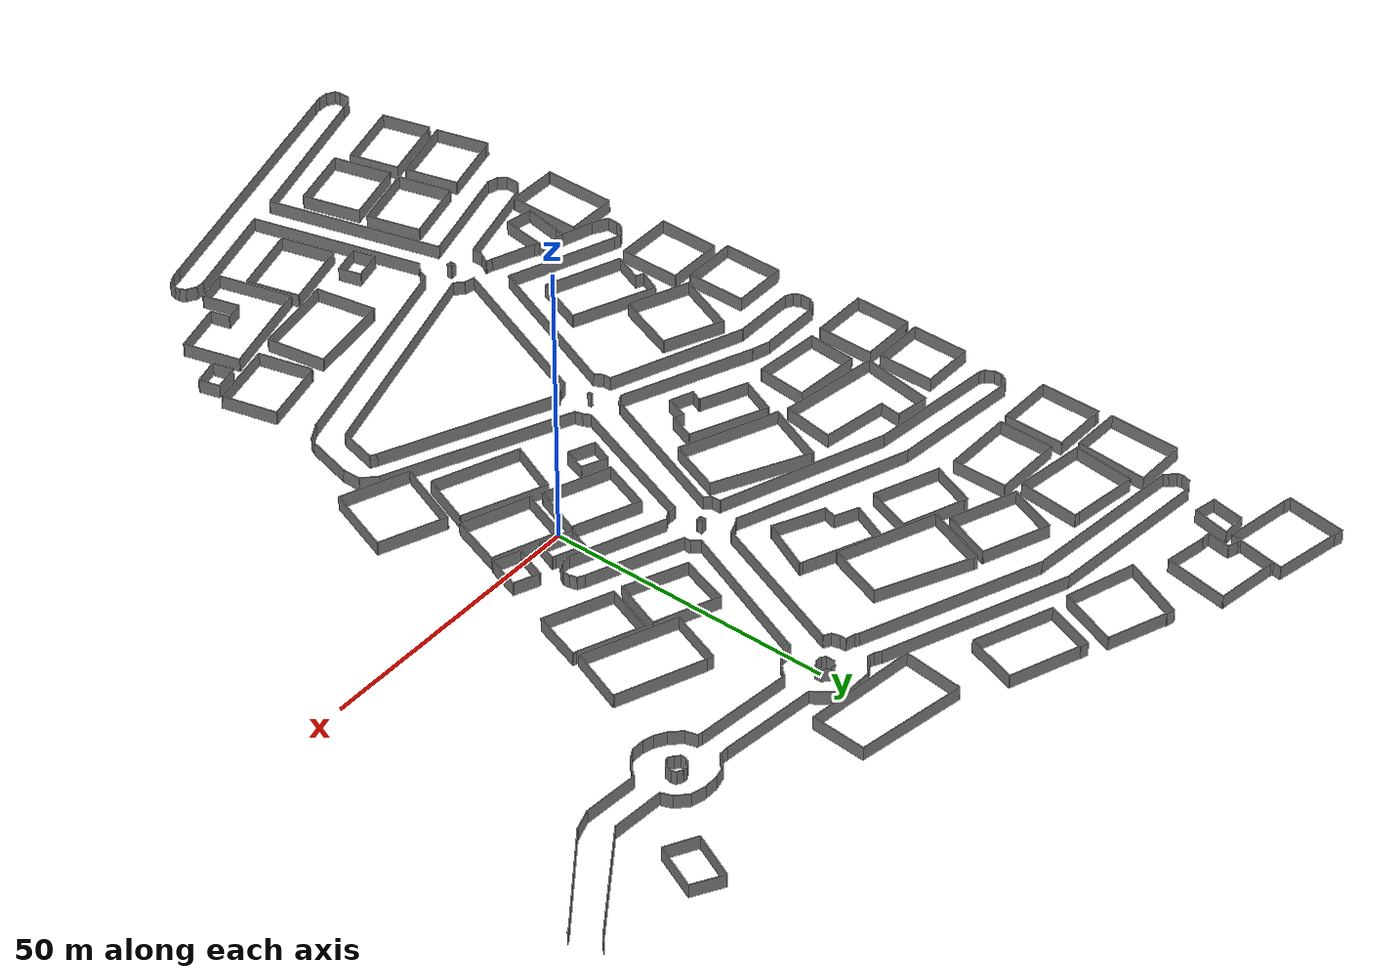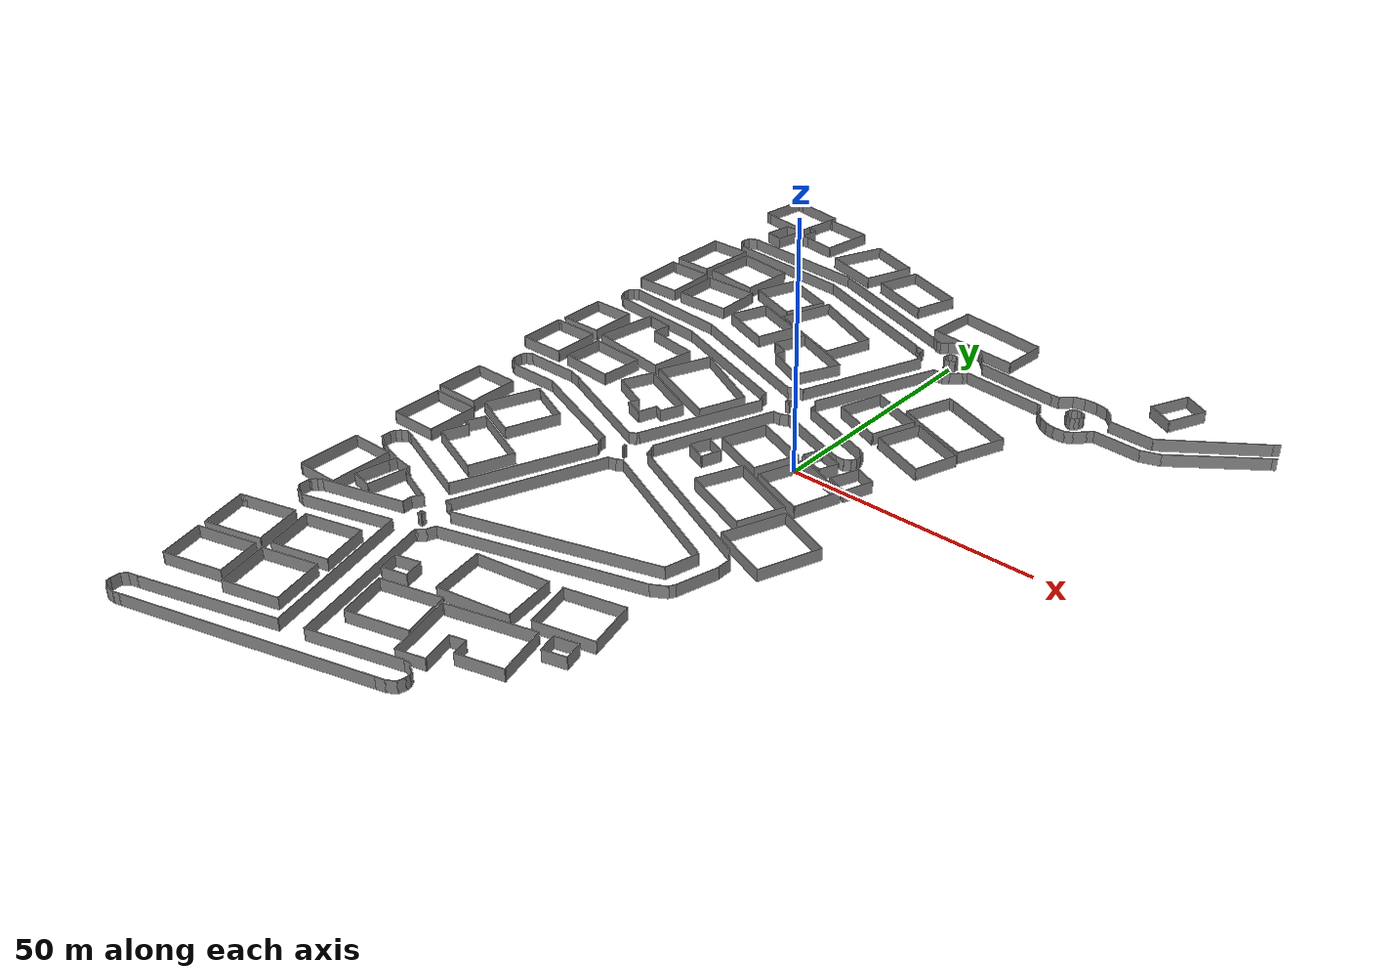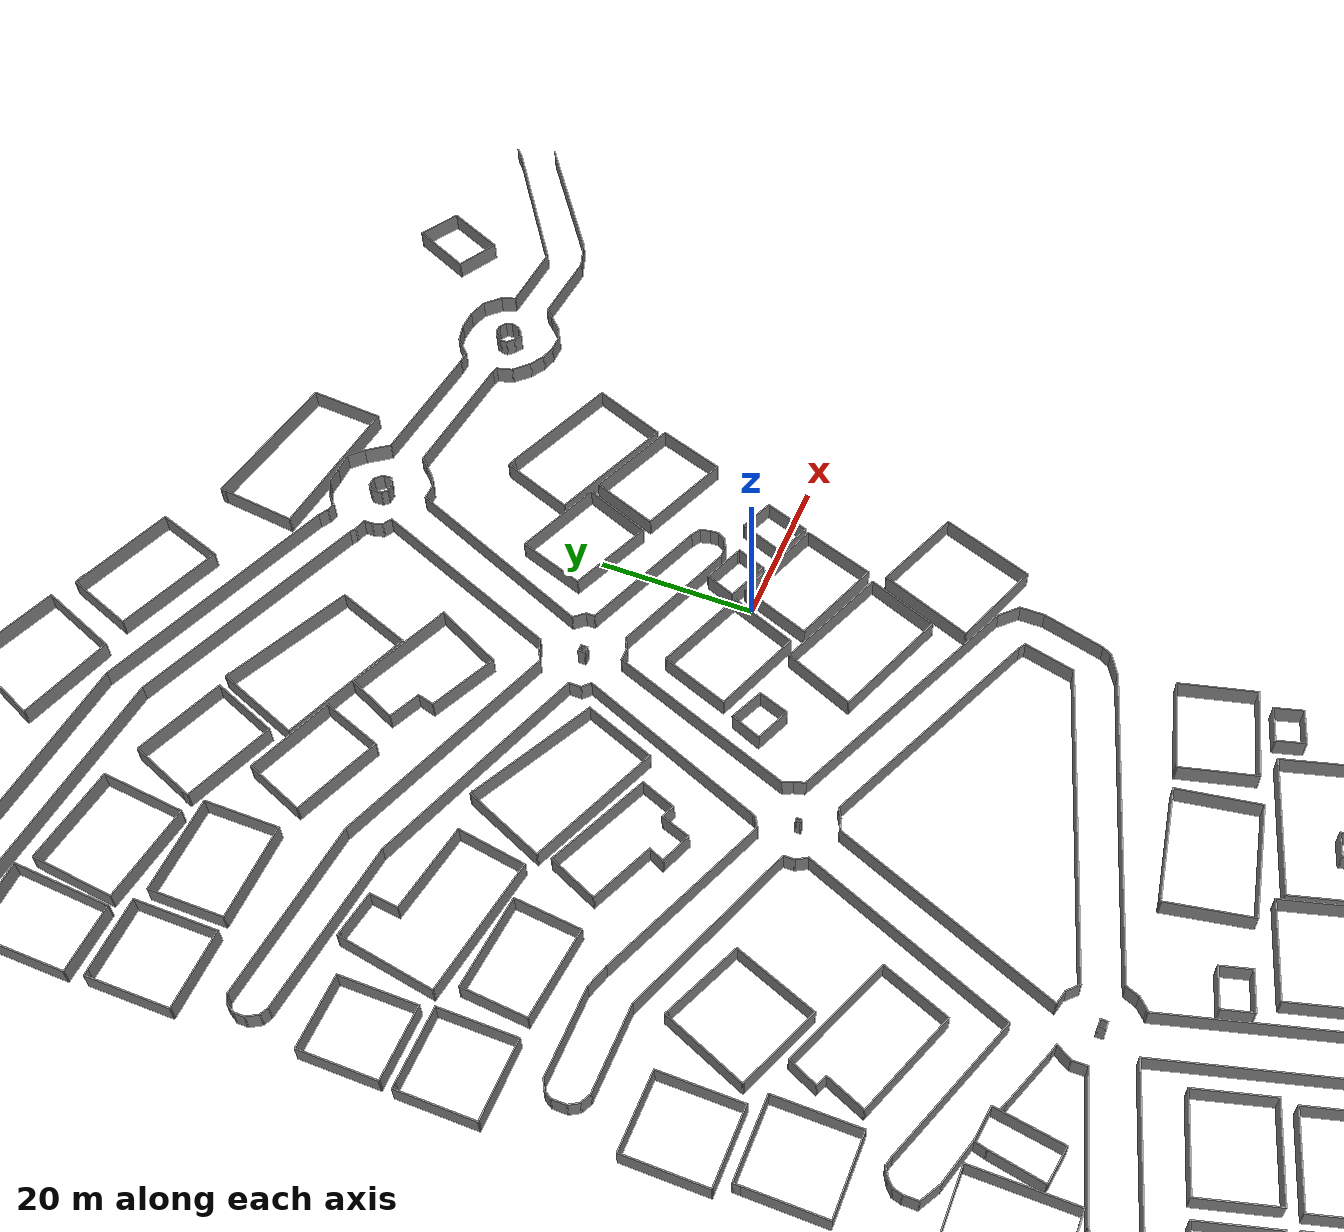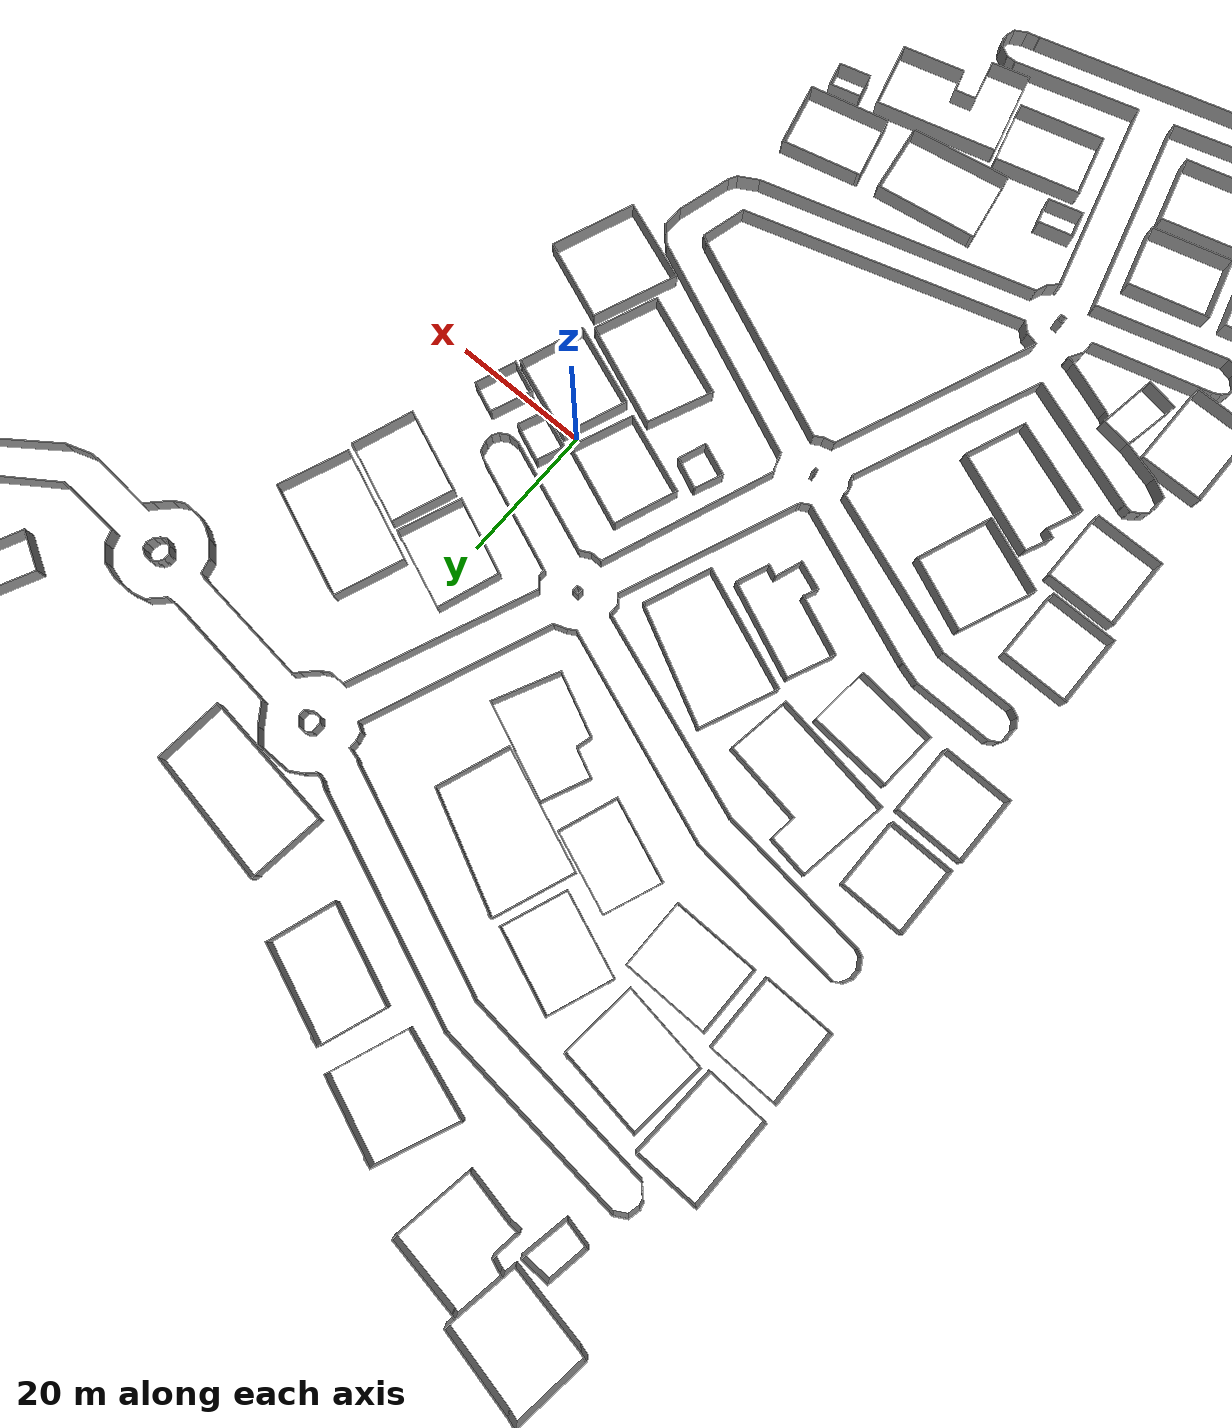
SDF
<?xml version='1.0'?>
<sdf version='1.6'>
  <model name='palazzo2'>
    <pose frame=''>-3.81107 -3.99805 0 0 -0 0</pose>
    <link name='Wall_1'>
      <collision name='Wall_1_Collision'>
        <geometry>
          <box>
            <size>1.5 0.15 2.5</size>
          </box>
        </geometry>
        <pose frame=''>0 0 1.25 0 -0 0</pose>
      </collision>
      <visual name='Wall_1_Visual'>
        <pose frame=''>0 0 1.25 0 -0 0</pose>
        <geometry>
          <box>
            <size>1.5 0.15 2.5</size>
          </box>
        </geometry>
        <material>
          <script>
            <uri>file://media/materials/scripts/gazebo.material</uri>
            <name>Gazebo/Grey</name>
          </script>
          <ambient>1 1 1 1</ambient>
        </material>
        <meta>
          <layer>0</layer>
        </meta>
      </visual>
      <pose frame=''>68.1139 65.5916 0 0 -0 -2.35619</pose>
    </link>
    <link name='Wall_100'>
      <collision name='Wall_100_Collision'>
        <geometry>
          <box>
            <size>1.5 0.15 2.5</size>
          </box>
        </geometry>
        <pose frame=''>0 0 1.25 0 -0 0</pose>
      </collision>
      <visual name='Wall_100_Visual'>
        <pose frame=''>0 0 1.25 0 -0 0</pose>
        <geometry>
          <box>
            <size>1.5 0.15 2.5</size>
          </box>
        </geometry>
        <material>
          <script>
            <uri>file://media/materials/scripts/gazebo.material</uri>
            <name>Gazebo/Grey</name>
          </script>
          <ambient>1 1 1 1</ambient>
        </material>
        <meta>
          <layer>0</layer>
        </meta>
      </visual>
      <pose frame=''>4.68181 55.6213 0 0 -0 -0.785398</pose>
    </link>
    <link name='Wall_101'>
      <collision name='Wall_101_Collision'>
        <geometry>
          <box>
            <size>1.25 0.15 2.5</size>
          </box>
        </geometry>
        <pose frame=''>0 0 1.25 0 -0 0</pose>
      </collision>
      <visual name='Wall_101_Visual'>
        <pose frame=''>0 0 1.25 0 -0 0</pose>
        <geometry>
          <box>
            <size>1.25 0.15 2.5</size>
          </box>
        </geometry>
        <material>
          <script>
            <uri>file://media/materials/scripts/gazebo.material</uri>
            <name>Gazebo/Grey</name>
          </script>
          <ambient>1 1 1 1</ambient>
        </material>
        <meta>
          <layer>0</layer>
        </meta>
      </visual>
      <pose frame=''>5.15911 54.594 0 0 -0 -1.5708</pose>
    </link>
    <link name='Wall_102'>
      <collision name='Wall_102_Collision'>
        <geometry>
          <box>
            <size>1.25 0.15 2.5</size>
          </box>
        </geometry>
        <pose frame=''>0 0 1.25 0 -0 0</pose>
      </collision>
      <visual name='Wall_102_Visual'>
        <pose frame=''>0 0 1.25 0 -0 0</pose>
        <geometry>
          <box>
            <size>1.25 0.15 2.5</size>
          </box>
        </geometry>
        <material>
          <script>
            <uri>file://media/materials/scripts/gazebo.material</uri>
            <name>Gazebo/Grey</name>
          </script>
          <ambient>1 1 1 1</ambient>
        </material>
        <meta>
          <layer>0</layer>
        </meta>
      </visual>
      <pose frame=''>4.68279 53.769 0 0 -0 -2.61799</pose>
    </link>
    <link name='Wall_103'>
      <collision name='Wall_103_Collision'>
        <geometry>
          <box>
            <size>1.25 0.15 2.5</size>
          </box>
        </geometry>
        <pose frame=''>0 0 1.25 0 -0 0</pose>
      </collision>
      <visual name='Wall_103_Visual'>
        <pose frame=''>0 0 1.25 0 -0 0</pose>
        <geometry>
          <box>
            <size>1.25 0.15 2.5</size>
          </box>
        </geometry>
        <material>
          <script>
            <uri>file://media/materials/scripts/gazebo.material</uri>
            <name>Gazebo/Grey</name>
          </script>
          <ambient>1 1 1 1</ambient>
        </material>
        <meta>
          <layer>0</layer>
        </meta>
      </visual>
      <pose frame=''>3.65648 53.494 0 0 -0 3.14159</pose>
    </link>
    <link name='Wall_104'>
      <collision name='Wall_104_Collision'>
        <geometry>
          <box>
            <size>1 0.15 2.5</size>
          </box>
        </geometry>
        <pose frame=''>0 0 1.25 0 -0 0</pose>
      </collision>
      <visual name='Wall_104_Visual'>
        <pose frame=''>0 0 1.25 0 -0 0</pose>
        <geometry>
          <box>
            <size>1 0.15 2.5</size>
          </box>
        </geometry>
        <material>
          <script>
            <uri>file://media/materials/scripts/gazebo.material</uri>
            <name>Gazebo/Grey</name>
          </script>
          <ambient>1 1 1 1</ambient>
        </material>
        <meta>
          <layer>0</layer>
        </meta>
      </visual>
      <pose frame=''>2.80596 53.7945 0 0 -0 2.35619</pose>
    </link>
    <link name='Wall_105'>
      <collision name='Wall_105_Collision'>
        <geometry>
          <box>
            <size>1.55251 0.15 2.5</size>
          </box>
        </geometry>
        <pose frame=''>0 0 1.25 0 -0 0</pose>
      </collision>
      <visual name='Wall_105_Visual'>
        <pose frame=''>0 0 1.25 0 -0 0</pose>
        <geometry>
          <box>
            <size>1.55251 0.15 2.5</size>
          </box>
        </geometry>
        <material>
          <script>
            <uri>file://media/materials/scripts/gazebo.material</uri>
            <name>Gazebo/Grey</name>
          </script>
          <ambient>1 1 1 1</ambient>
        </material>
        <meta>
          <layer>0</layer>
        </meta>
      </visual>
      <pose frame=''>2.50446 54.7963 0 0 -0 1.5722</pose>
    </link>
    <link name='Wall_107'>
      <collision name='Wall_107_Collision'>
        <geometry>
          <box>
            <size>27.4393 0.15 2.5</size>
          </box>
        </geometry>
        <pose frame=''>0 0 1.25 0 -0 0</pose>
      </collision>
      <visual name='Wall_107_Visual'>
        <pose frame=''>0 0 1.25 0 -0 0</pose>
        <geometry>
          <box>
            <size>27.4393 0.15 2.5</size>
          </box>
        </geometry>
        <material>
          <script>
            <uri>file://media/materials/scripts/gazebo.material</uri>
            <name>Gazebo/Grey</name>
          </script>
          <ambient>1 1 1 1</ambient>
        </material>
        <meta>
          <layer>0</layer>
        </meta>
      </visual>
      <pose frame=''>-1.37579 35.8973 0 0 -0 1.17687</pose>
    </link>
    <link name='Wall_110'>
      <collision name='Wall_110_Collision'>
        <geometry>
          <box>
            <size>27.4433 0.15 2.5</size>
          </box>
        </geometry>
        <pose frame=''>0 0 1.25 0 -0 0</pose>
      </collision>
      <visual name='Wall_110_Visual'>
        <pose frame=''>0 0 1.25 0 -0 0</pose>
        <geometry>
          <box>
            <size>27.4433 0.15 2.5</size>
          </box>
        </geometry>
        <material>
          <script>
            <uri>file://media/materials/scripts/gazebo.material</uri>
            <name>Gazebo/Grey</name>
          </script>
          <ambient>1 1 1 1</ambient>
        </material>
        <meta>
          <layer>0</layer>
        </meta>
      </visual>
      <pose frame=''>-5.98467 38.1714 0 0 -0 1.18986</pose>
    </link>
    <link name='Wall_112'>
      <collision name='Wall_112_Collision'>
        <geometry>
          <box>
            <size>1.5 0.15 2.5</size>
          </box>
        </geometry>
        <pose frame=''>0 0 1.25 0 -0 0</pose>
      </collision>
      <visual name='Wall_112_Visual'>
        <pose frame=''>0 0 1.25 0 -0 0</pose>
        <geometry>
          <box>
            <size>1.5 0.15 2.5</size>
          </box>
        </geometry>
        <material>
          <script>
            <uri>file://media/materials/scripts/gazebo.material</uri>
            <name>Gazebo/Grey</name>
          </script>
          <ambient>1 1 1 1</ambient>
        </material>
        <meta>
          <layer>0</layer>
        </meta>
      </visual>
      <pose frame=''>-13.3123 24.552 0 0 -0 0.523599</pose>
    </link>
    <link name='Wall_113'>
      <collision name='Wall_113_Collision'>
        <geometry>
          <box>
            <size>1.92852 0.15 2.5</size>
          </box>
        </geometry>
        <pose frame=''>0 0 1.25 0 -0 0</pose>
      </collision>
      <visual name='Wall_113_Visual'>
        <pose frame=''>0 0 1.25 0 -0 0</pose>
        <geometry>
          <box>
            <size>1.92852 0.15 2.5</size>
          </box>
        </geometry>
        <material>
          <script>
            <uri>file://media/materials/scripts/gazebo.material</uri>
            <name>Gazebo/Grey</name>
          </script>
          <ambient>1 1 1 1</ambient>
        </material>
        <meta>
          <layer>0</layer>
        </meta>
      </visual>
      <pose frame=''>-11.893 25.1962 0 0 -0 0.352149</pose>
    </link>
    <link name='Wall_119'>
      <collision name='Wall_119_Collision'>
        <geometry>
          <box>
            <size>1.25 0.15 2.5</size>
          </box>
        </geometry>
        <pose frame=''>0 0 1.25 0 -0 0</pose>
      </collision>
      <visual name='Wall_119_Visual'>
        <pose frame=''>0 0 1.25 0 -0 0</pose>
        <geometry>
          <box>
            <size>1.25 0.15 2.5</size>
          </box>
        </geometry>
        <material>
          <script>
            <uri>file://media/materials/scripts/gazebo.material</uri>
            <name>Gazebo/Grey</name>
          </script>
          <ambient>1 1 1 1</ambient>
        </material>
        <meta>
          <layer>0</layer>
        </meta>
      </visual>
      <pose frame=''>-5.48076 21.4011 0 0 -0 1.5708</pose>
    </link>
    <link name='Wall_120'>
      <collision name='Wall_120_Collision'>
        <geometry>
          <box>
            <size>1.90927 0.15 2.5</size>
          </box>
        </geometry>
        <pose frame=''>0 0 1.25 0 -0 0</pose>
      </collision>
      <visual name='Wall_120_Visual'>
        <pose frame=''>0 0 1.25 0 -0 0</pose>
        <geometry>
          <box>
            <size>1.90927 0.15 2.5</size>
          </box>
        </geometry>
        <material>
          <script>
            <uri>file://media/materials/scripts/gazebo.material</uri>
            <name>Gazebo/Grey</name>
          </script>
          <ambient>1 1 1 1</ambient>
        </material>
        <meta>
          <layer>0</layer>
        </meta>
      </visual>
      <pose frame=''>-6.04681 22.6244 0 0 -0 2.26988</pose>
    </link>
    <link name='Wall_122'>
      <collision name='Wall_122_Collision'>
        <geometry>
          <box>
            <size>17.2432 0.15 2.5</size>
          </box>
        </geometry>
        <pose frame=''>0 0 1.25 0 -0 0</pose>
      </collision>
      <visual name='Wall_122_Visual'>
        <pose frame=''>0 0 1.25 0 -0 0</pose>
        <geometry>
          <box>
            <size>17.2432 0.15 2.5</size>
          </box>
        </geometry>
        <material>
          <script>
            <uri>file://media/materials/scripts/gazebo.material</uri>
            <name>Gazebo/Grey</name>
          </script>
          <ambient>1 1 1 1</ambient>
        </material>
        <meta>
          <layer>0</layer>
        </meta>
      </visual>
      <pose frame=''>2.49205 17.7724 0 0 -0 2.77308</pose>
    </link>
    <link name='Wall_124'>
      <collision name='Wall_124_Collision'>
        <geometry>
          <box>
            <size>1.5 0.15 2.5</size>
          </box>
        </geometry>
        <pose frame=''>0 0 1.25 0 -0 0</pose>
      </collision>
      <visual name='Wall_124_Visual'>
        <pose frame=''>0 0 1.25 0 -0 0</pose>
        <geometry>
          <box>
            <size>1.5 0.15 2.5</size>
          </box>
        </geometry>
        <material>
          <script>
            <uri>file://media/materials/scripts/gazebo.material</uri>
            <name>Gazebo/Grey</name>
          </script>
          <ambient>1 1 1 1</ambient>
        </material>
        <meta>
          <layer>0</layer>
        </meta>
      </visual>
      <pose frame=''>11.0494 14.3562 0 0 -0 -0.523599</pose>
    </link>
    <link name='Wall_125'>
      <collision name='Wall_125_Collision'>
        <geometry>
          <box>
            <size>1.5 0.15 2.5</size>
          </box>
        </geometry>
        <pose frame=''>0 0 1.25 0 -0 0</pose>
      </collision>
      <visual name='Wall_125_Visual'>
        <pose frame=''>0 0 1.25 0 -0 0</pose>
        <geometry>
          <box>
            <size>1.5 0.15 2.5</size>
          </box>
        </geometry>
        <material>
          <script>
            <uri>file://media/materials/scripts/gazebo.material</uri>
            <name>Gazebo/Grey</name>
          </script>
          <ambient>1 1 1 1</ambient>
        </material>
        <meta>
          <layer>0</layer>
        </meta>
      </visual>
      <pose frame=''>11.8087 13.3667 0 0 -0 -1.309</pose>
    </link>
    <link name='Wall_126'>
      <collision name='Wall_126_Collision'>
        <geometry>
          <box>
            <size>1.25 0.15 2.5</size>
          </box>
        </geometry>
        <pose frame=''>0 0 1.25 0 -0 0</pose>
      </collision>
      <visual name='Wall_126_Visual'>
        <pose frame=''>0 0 1.25 0 -0 0</pose>
        <geometry>
          <box>
            <size>1.25 0.15 2.5</size>
          </box>
        </geometry>
        <material>
          <script>
            <uri>file://media/materials/scripts/gazebo.material</uri>
            <name>Gazebo/Grey</name>
          </script>
          <ambient>1 1 1 1</ambient>
        </material>
        <meta>
          <layer>0</layer>
        </meta>
      </visual>
      <pose frame=''>11.9834 12.1647 0 0 -0 -1.5708</pose>
    </link>
    <link name='Wall_127'>
      <collision name='Wall_127_Collision'>
        <geometry>
          <box>
            <size>1.25 0.15 2.5</size>
          </box>
        </geometry>
        <pose frame=''>0 0 1.25 0 -0 0</pose>
      </collision>
      <visual name='Wall_127_Visual'>
        <pose frame=''>0 0 1.25 0 -0 0</pose>
        <geometry>
          <box>
            <size>1.25 0.15 2.5</size>
          </box>
        </geometry>
        <material>
          <script>
            <uri>file://media/materials/scripts/gazebo.material</uri>
            <name>Gazebo/Grey</name>
          </script>
          <ambient>1 1 1 1</ambient>
        </material>
        <meta>
          <layer>0</layer>
        </meta>
      </visual>
      <pose frame=''>11.7084 11.1384 0 0 -0 -2.0944</pose>
    </link>
    <link name='Wall_128'>
      <collision name='Wall_128_Collision'>
        <geometry>
          <box>
            <size>1.5 0.15 2.5</size>
          </box>
        </geometry>
        <pose frame=''>0 0 1.25 0 -0 0</pose>
      </collision>
      <visual name='Wall_128_Visual'>
        <pose frame=''>0 0 1.25 0 -0 0</pose>
        <geometry>
          <box>
            <size>1.5 0.15 2.5</size>
          </box>
        </geometry>
        <material>
          <script>
            <uri>file://media/materials/scripts/gazebo.material</uri>
            <name>Gazebo/Grey</name>
          </script>
          <ambient>1 1 1 1</ambient>
        </material>
        <meta>
          <layer>0</layer>
        </meta>
      </visual>
      <pose frame=''>10.8488 10.3245 0 0 -0 -2.61799</pose>
    </link>
    <link name='Wall_129'>
      <collision name='Wall_129_Collision'>
        <geometry>
          <box>
            <size>1.75 0.15 2.5</size>
          </box>
        </geometry>
        <pose frame=''>0 0 1.25 0 -0 0</pose>
      </collision>
      <visual name='Wall_129_Visual'>
        <pose frame=''>0 0 1.25 0 -0 0</pose>
        <geometry>
          <box>
            <size>1.75 0.15 2.5</size>
          </box>
        </geometry>
        <material>
          <script>
            <uri>file://media/materials/scripts/gazebo.material</uri>
            <name>Gazebo/Grey</name>
          </script>
          <ambient>1 1 1 1</ambient>
        </material>
        <meta>
          <layer>0</layer>
        </meta>
      </visual>
      <pose frame=''>9.46425 9.98705 0 0 -0 3.14159</pose>
    </link>
    <link name='Wall_131'>
      <collision name='Wall_131_Collision'>
        <geometry>
          <box>
            <size>17.0401 0.15 2.5</size>
          </box>
        </geometry>
        <pose frame=''>0 0 1.25 0 -0 0</pose>
      </collision>
      <visual name='Wall_131_Visual'>
        <pose frame=''>0 0 1.25 0 -0 0</pose>
        <geometry>
          <box>
            <size>17.0401 0.15 2.5</size>
          </box>
        </geometry>
        <material>
          <script>
            <uri>file://media/materials/scripts/gazebo.material</uri>
            <name>Gazebo/Grey</name>
          </script>
          <ambient>1 1 1 1</ambient>
        </material>
        <meta>
          <layer>0</layer>
        </meta>
      </visual>
      <pose frame=''>0.769019 12.9844 0 0 -0 -0.362836</pose>
    </link>
    <link name='Wall_133'>
      <collision name='Wall_133_Collision'>
        <geometry>
          <box>
            <size>1.75 0.15 2.5</size>
          </box>
        </geometry>
        <pose frame=''>0 0 1.25 0 -0 0</pose>
      </collision>
      <visual name='Wall_133_Visual'>
        <pose frame=''>0 0 1.25 0 -0 0</pose>
        <geometry>
          <box>
            <size>1.75 0.15 2.5</size>
          </box>
        </geometry>
        <material>
          <script>
            <uri>file://media/materials/scripts/gazebo.material</uri>
            <name>Gazebo/Grey</name>
          </script>
          <ambient>1 1 1 1</ambient>
        </material>
        <meta>
          <layer>0</layer>
        </meta>
      </visual>
      <pose frame=''>-9.38553 15.217 0 0 -0 0</pose>
    </link>
    <link name='Wall_134'>
      <collision name='Wall_134_Collision'>
        <geometry>
          <box>
            <size>1.79759 0.15 2.5</size>
          </box>
        </geometry>
        <pose frame=''>0 0 1.25 0 -0 0</pose>
      </collision>
      <visual name='Wall_134_Visual'>
        <pose frame=''>0 0 1.25 0 -0 0</pose>
        <geometry>
          <box>
            <size>1.79759 0.15 2.5</size>
          </box>
        </geometry>
        <material>
          <script>
            <uri>file://media/materials/scripts/gazebo.material</uri>
            <name>Gazebo/Grey</name>
          </script>
          <ambient>1 1 1 1</ambient>
        </material>
        <meta>
          <layer>0</layer>
        </meta>
      </visual>
      <pose frame=''>-7.85587 15.5994 0 0 -0 0.482742</pose>
    </link>
    <link name='Wall_137'>
      <collision name='Wall_137_Collision'>
        <geometry>
          <box>
            <size>1.5 0.15 2.5</size>
          </box>
        </geometry>
        <pose frame=''>0 0 1.25 0 -0 0</pose>
      </collision>
      <visual name='Wall_137_Visual'>
        <pose frame=''>0 0 1.25 0 -0 0</pose>
        <geometry>
          <box>
            <size>1.5 0.15 2.5</size>
          </box>
        </geometry>
        <material>
          <script>
            <uri>file://media/materials/scripts/gazebo.material</uri>
            <name>Gazebo/Grey</name>
          </script>
          <ambient>1 1 1 1</ambient>
        </material>
        <meta>
          <layer>0</layer>
        </meta>
      </visual>
      <pose frame=''>-15.131 17.6063 0 0 -0 2.35619</pose>
    </link>
    <link name='Wall_138'>
      <collision name='Wall_138_Collision'>
        <geometry>
          <box>
            <size>1.75 0.15 2.5</size>
          </box>
        </geometry>
        <pose frame=''>0 0 1.25 0 -0 0</pose>
      </collision>
      <visual name='Wall_138_Visual'>
        <pose frame=''>0 0 1.25 0 -0 0</pose>
        <geometry>
          <box>
            <size>1.75 0.15 2.5</size>
          </box>
        </geometry>
        <material>
          <script>
            <uri>file://media/materials/scripts/gazebo.material</uri>
            <name>Gazebo/Grey</name>
          </script>
          <ambient>1 1 1 1</ambient>
        </material>
        <meta>
          <layer>0</layer>
        </meta>
      </visual>
      <pose frame=''>-15.6083 18.8836 0 0 -0 1.5708</pose>
    </link>
    <link name='Wall_142'>
      <collision name='Wall_142_Collision'>
        <geometry>
          <box>
            <size>30.0132 0.15 2.5</size>
          </box>
        </geometry>
        <pose frame=''>0 0 1.25 0 -0 0</pose>
      </collision>
      <visual name='Wall_142_Visual'>
        <pose frame=''>0 0 1.25 0 -0 0</pose>
        <geometry>
          <box>
            <size>30.0132 0.15 2.5</size>
          </box>
        </geometry>
        <material>
          <script>
            <uri>file://media/materials/scripts/gazebo.material</uri>
            <name>Gazebo/Grey</name>
          </script>
          <ambient>1 1 1 1</ambient>
        </material>
        <meta>
          <layer>0</layer>
        </meta>
      </visual>
      <pose frame=''>-29.6687 24.7095 0 0 -0 -0.343294</pose>
    </link>
    <link name='Wall_144'>
      <collision name='Wall_144_Collision'>
        <geometry>
          <box>
            <size>31.0112 0.15 2.5</size>
          </box>
        </geometry>
        <pose frame=''>0 0 1.25 0 -0 0</pose>
      </collision>
      <visual name='Wall_144_Visual'>
        <pose frame=''>0 0 1.25 0 -0 0</pose>
        <geometry>
          <box>
            <size>31.0112 0.15 2.5</size>
          </box>
        </geometry>
        <material>
          <script>
            <uri>file://media/materials/scripts/gazebo.material</uri>
            <name>Gazebo/Grey</name>
          </script>
          <ambient>1 1 1 1</ambient>
        </material>
        <meta>
          <layer>0</layer>
        </meta>
      </visual>
      <pose frame=''>-28.3905 29.5095 0 0 -0 -0.350266</pose>
    </link>
    <link name='Wall_146'>
      <collision name='Wall_146_Collision'>
        <geometry>
          <box>
            <size>22.8101 0.15 2.5</size>
          </box>
        </geometry>
        <pose frame=''>0 0 1.25 0 -0 0</pose>
      </collision>
      <visual name='Wall_146_Visual'>
        <pose frame=''>0 0 1.25 0 -0 0</pose>
        <geometry>
          <box>
            <size>22.8101 0.15 2.5</size>
          </box>
        </geometry>
        <material>
          <script>
            <uri>file://media/materials/scripts/gazebo.material</uri>
            <name>Gazebo/Grey</name>
          </script>
          <ambient>1 1 1 1</ambient>
        </material>
        <meta>
          <layer>0</layer>
        </meta>
      </visual>
      <pose frame=''>-54.1666 35.8429 0 0 -0 -0.091785</pose>
    </link>
    <link name='Wall_148'>
      <collision name='Wall_148_Collision'>
        <geometry>
          <box>
            <size>21.8464 0.15 2.5</size>
          </box>
        </geometry>
        <pose frame=''>0 0 1.25 0 -0 0</pose>
      </collision>
      <visual name='Wall_148_Visual'>
        <pose frame=''>0 0 1.25 0 -0 0</pose>
        <geometry>
          <box>
            <size>21.8464 0.15 2.5</size>
          </box>
        </geometry>
        <material>
          <script>
            <uri>file://media/materials/scripts/gazebo.material</uri>
            <name>Gazebo/Grey</name>
          </script>
          <ambient>1 1 1 1</ambient>
        </material>
        <meta>
          <layer>0</layer>
        </meta>
      </visual>
      <pose frame=''>-54.5186 30.8618 0 0 -0 -0.104028</pose>
    </link>
    <link name='Wall_150'>
      <collision name='Wall_150_Collision'>
        <geometry>
          <box>
            <size>1.25 0.15 2.5</size>
          </box>
        </geometry>
        <pose frame=''>0 0 1.25 0 -0 0</pose>
      </collision>
      <visual name='Wall_150_Visual'>
        <pose frame=''>0 0 1.25 0 -0 0</pose>
        <geometry>
          <box>
            <size>1.25 0.15 2.5</size>
          </box>
        </geometry>
        <material>
          <script>
            <uri>file://media/materials/scripts/gazebo.material</uri>
            <name>Gazebo/Grey</name>
          </script>
          <ambient>1 1 1 1</ambient>
        </material>
        <meta>
          <layer>0</layer>
        </meta>
      </visual>
      <pose frame=''>-65.9253 36.6064 0 0 -0 -2.61799</pose>
    </link>
    <link name='Wall_151'>
      <collision name='Wall_151_Collision'>
        <geometry>
          <box>
            <size>1.5 0.15 2.5</size>
          </box>
        </geometry>
        <pose frame=''>0 0 1.25 0 -0 0</pose>
      </collision>
      <visual name='Wall_151_Visual'>
        <pose frame=''>0 0 1.25 0 -0 0</pose>
        <geometry>
          <box>
            <size>1.5 0.15 2.5</size>
          </box>
        </geometry>
        <material>
          <script>
            <uri>file://media/materials/scripts/gazebo.material</uri>
            <name>Gazebo/Grey</name>
          </script>
          <ambient>1 1 1 1</ambient>
        </material>
        <meta>
          <layer>0</layer>
        </meta>
      </visual>
      <pose frame=''>-66.7391 35.7468 0 0 -0 -2.0944</pose>
    </link>
    <link name='Wall_152'>
      <collision name='Wall_152_Collision'>
        <geometry>
          <box>
            <size>1.5 0.15 2.5</size>
          </box>
        </geometry>
        <pose frame=''>0 0 1.25 0 -0 0</pose>
      </collision>
      <visual name='Wall_152_Visual'>
        <pose frame=''>0 0 1.25 0 -0 0</pose>
        <geometry>
          <box>
            <size>1.5 0.15 2.5</size>
          </box>
        </geometry>
        <material>
          <script>
            <uri>file://media/materials/scripts/gazebo.material</uri>
            <name>Gazebo/Grey</name>
          </script>
          <ambient>1 1 1 1</ambient>
        </material>
        <meta>
          <layer>0</layer>
        </meta>
      </visual>
      <pose frame=''>-67.0766 34.4873 0 0 -0 -1.5708</pose>
    </link>
    <link name='Wall_153'>
      <collision name='Wall_153_Collision'>
        <geometry>
          <box>
            <size>1.75 0.15 2.5</size>
          </box>
        </geometry>
        <pose frame=''>0 0 1.25 0 -0 0</pose>
      </collision>
      <visual name='Wall_153_Visual'>
        <pose frame=''>0 0 1.25 0 -0 0</pose>
        <geometry>
          <box>
            <size>1.75 0.15 2.5</size>
          </box>
        </geometry>
        <material>
          <script>
            <uri>file://media/materials/scripts/gazebo.material</uri>
            <name>Gazebo/Grey</name>
          </script>
          <ambient>1 1 1 1</ambient>
        </material>
        <meta>
          <layer>0</layer>
        </meta>
      </visual>
      <pose frame=''>-66.6766 33.1194 0 0 -0 -1.0472</pose>
    </link>
    <link name='Wall_154'>
      <collision name='Wall_154_Collision'>
        <geometry>
          <box>
            <size>1.21303 0.15 2.5</size>
          </box>
        </geometry>
        <pose frame=''>0 0 1.25 0 -0 0</pose>
      </collision>
      <visual name='Wall_154_Visual'>
        <pose frame=''>0 0 1.25 0 -0 0</pose>
        <geometry>
          <box>
            <size>1.21303 0.15 2.5</size>
          </box>
        </geometry>
        <material>
          <script>
            <uri>file://media/materials/scripts/gazebo.material</uri>
            <name>Gazebo/Grey</name>
          </script>
          <ambient>1 1 1 1</ambient>
        </material>
        <meta>
          <layer>0</layer>
        </meta>
      </visual>
      <pose frame=''>-65.7924 32.2074 0 0 -0 -0.42505</pose>
    </link>
    <link name='Wall_159'>
      <collision name='Wall_159_Collision'>
        <geometry>
          <box>
            <size>1 0.15 2.5</size>
          </box>
        </geometry>
        <pose frame=''>0 0 1.25 0 -0 0</pose>
      </collision>
      <visual name='Wall_159_Visual'>
        <pose frame=''>0 0 1.25 0 -0 0</pose>
        <geometry>
          <box>
            <size>1 0.15 2.5</size>
          </box>
        </geometry>
        <material>
          <script>
            <uri>file://media/materials/scripts/gazebo.material</uri>
            <name>Gazebo/Grey</name>
          </script>
          <ambient>1 1 1 1</ambient>
        </material>
        <meta>
          <layer>0</layer>
        </meta>
      </visual>
      <pose frame=''>-10.4841 20.558 0 0 -0 0</pose>
    </link>
    <link name='Wall_160'>
      <collision name='Wall_160_Collision'>
        <geometry>
          <box>
            <size>1 0.15 2.5</size>
          </box>
        </geometry>
        <pose frame=''>0 0 1.25 0 -0 0</pose>
      </collision>
      <visual name='Wall_160_Visual'>
        <pose frame=''>0 0 1.25 0 -0 0</pose>
        <geometry>
          <box>
            <size>1 0.15 2.5</size>
          </box>
        </geometry>
        <material>
          <script>
            <uri>file://media/materials/scripts/gazebo.material</uri>
            <name>Gazebo/Grey</name>
          </script>
          <ambient>1 1 1 1</ambient>
        </material>
        <meta>
          <layer>0</layer>
        </meta>
      </visual>
      <pose frame=''>-10.0591 20.133 0 0 -0 -1.5708</pose>
    </link>
    <link name='Wall_161'>
      <collision name='Wall_161_Collision'>
        <geometry>
          <box>
            <size>1 0.15 2.5</size>
          </box>
        </geometry>
        <pose frame=''>0 0 1.25 0 -0 0</pose>
      </collision>
      <visual name='Wall_161_Visual'>
        <pose frame=''>0 0 1.25 0 -0 0</pose>
        <geometry>
          <box>
            <size>1 0.15 2.5</size>
          </box>
        </geometry>
        <material>
          <script>
            <uri>file://media/materials/scripts/gazebo.material</uri>
            <name>Gazebo/Grey</name>
          </script>
          <ambient>1 1 1 1</ambient>
        </material>
        <meta>
          <layer>0</layer>
        </meta>
      </visual>
      <pose frame=''>-10.4841 19.708 0 0 -0 3.14159</pose>
    </link>
    <link name='Wall_162'>
      <collision name='Wall_162_Collision'>
        <geometry>
          <box>
            <size>1 0.15 2.5</size>
          </box>
        </geometry>
        <pose frame=''>0 0 1.25 0 -0 0</pose>
      </collision>
      <visual name='Wall_162_Visual'>
        <pose frame=''>0 0 1.25 0 -0 0</pose>
        <geometry>
          <box>
            <size>1 0.15 2.5</size>
          </box>
        </geometry>
        <material>
          <script>
            <uri>file://media/materials/scripts/gazebo.material</uri>
            <name>Gazebo/Grey</name>
          </script>
          <ambient>1 1 1 1</ambient>
        </material>
        <meta>
          <layer>0</layer>
        </meta>
      </visual>
      <pose frame=''>-10.9091 20.133 0 0 -0 1.5708</pose>
    </link>
    <link name='Wall_164'>
      <collision name='Wall_164_Collision'>
        <geometry>
          <box>
            <size>25.8072 0.15 2.5</size>
          </box>
        </geometry>
        <pose frame=''>0 0 1.25 0 -0 0</pose>
      </collision>
      <visual name='Wall_164_Visual'>
        <pose frame=''>0 0 1.25 0 -0 0</pose>
        <geometry>
          <box>
            <size>25.8072 0.15 2.5</size>
          </box>
        </geometry>
        <material>
          <script>
            <uri>file://media/materials/scripts/gazebo.material</uri>
            <name>Gazebo/Grey</name>
          </script>
          <ambient>1 1 1 1</ambient>
        </material>
        <meta>
          <layer>0</layer>
        </meta>
      </visual>
      <pose frame=''>-14.7527 3.22891 0 0 -0 1.2068</pose>
    </link>
    <link name='Wall_166'>
      <collision name='Wall_166_Collision'>
        <geometry>
          <box>
            <size>26.3375 0.15 2.5</size>
          </box>
        </geometry>
        <pose frame=''>0 0 1.25 0 -0 0</pose>
      </collision>
      <visual name='Wall_166_Visual'>
        <pose frame=''>0 0 1.25 0 -0 0</pose>
        <geometry>
          <box>
            <size>26.3375 0.15 2.5</size>
          </box>
        </geometry>
        <material>
          <script>
            <uri>file://media/materials/scripts/gazebo.material</uri>
            <name>Gazebo/Grey</name>
          </script>
          <ambient>1 1 1 1</ambient>
        </material>
        <meta>
          <layer>0</layer>
        </meta>
      </visual>
      <pose frame=''>-19.5581 4.98848 0 0 -0 1.18688</pose>
    </link>
    <link name='Wall_169'>
      <collision name='Wall_169_Collision'>
        <geometry>
          <box>
            <size>1.5 0.15 2.5</size>
          </box>
        </geometry>
        <pose frame=''>0 0 1.25 0 -0 0</pose>
      </collision>
      <visual name='Wall_169_Visual'>
        <pose frame=''>0 0 1.25 0 -0 0</pose>
        <geometry>
          <box>
            <size>1.5 0.15 2.5</size>
          </box>
        </geometry>
        <material>
          <script>
            <uri>file://media/materials/scripts/gazebo.material</uri>
            <name>Gazebo/Grey</name>
          </script>
          <ambient>1 1 1 1</ambient>
        </material>
        <meta>
          <layer>0</layer>
        </meta>
      </visual>
      <pose frame=''>-18.5765 -10.6095 0 0 -0 1.8326</pose>
    </link>
    <link name='Wall_170'>
      <collision name='Wall_170_Collision'>
        <geometry>
          <box>
            <size>1.47641 0.15 2.5</size>
          </box>
        </geometry>
        <pose frame=''>0 0 1.25 0 -0 0</pose>
      </collision>
      <visual name='Wall_170_Visual'>
        <pose frame=''>0 0 1.25 0 -0 0</pose>
        <geometry>
          <box>
            <size>1.47641 0.15 2.5</size>
          </box>
        </geometry>
        <material>
          <script>
            <uri>file://media/materials/scripts/gazebo.material</uri>
            <name>Gazebo/Grey</name>
          </script>
          <ambient>1 1 1 1</ambient>
        </material>
        <meta>
          <layer>0</layer>
        </meta>
      </visual>
      <pose frame=''>-19.0355 -9.35834 0 0 -0 2.01381</pose>
    </link>
    <link name='Wall_172'>
      <collision name='Wall_172_Collision'>
        <geometry>
          <box>
            <size>33.7639 0.15 2.5</size>
          </box>
        </geometry>
        <pose frame=''>0 0 1.25 0 -0 0</pose>
      </collision>
      <visual name='Wall_172_Visual'>
        <pose frame=''>0 0 1.25 0 -0 0</pose>
        <geometry>
          <box>
            <size>33.7639 0.15 2.5</size>
          </box>
        </geometry>
        <material>
          <script>
            <uri>file://media/materials/scripts/gazebo.material</uri>
            <name>Gazebo/Grey</name>
          </script>
          <ambient>1 1 1 1</ambient>
        </material>
        <meta>
          <layer>0</layer>
        </meta>
      </visual>
      <pose frame=''>-2.99951 -17.9878 0 0 -0 2.72985</pose>
    </link>
    <link name='Wall_174'>
      <collision name='Wall_174_Collision'>
        <geometry>
          <box>
            <size>1.75 0.15 2.5</size>
          </box>
        </geometry>
        <pose frame=''>0 0 1.25 0 -0 0</pose>
      </collision>
      <visual name='Wall_174_Visual'>
        <pose frame=''>0 0 1.25 0 -0 0</pose>
        <geometry>
          <box>
            <size>1.75 0.15 2.5</size>
          </box>
        </geometry>
        <material>
          <script>
            <uri>file://media/materials/scripts/gazebo.material</uri>
            <name>Gazebo/Grey</name>
          </script>
          <ambient>1 1 1 1</ambient>
        </material>
        <meta>
          <layer>0</layer>
        </meta>
      </visual>
      <pose frame=''>-22.0611 -16.8174 0 0 -0 0.261799</pose>
    </link>
    <link name='Wall_175'>
      <collision name='Wall_175_Collision'>
        <geometry>
          <box>
            <size>1.5 0.15 2.5</size>
          </box>
        </geometry>
        <pose frame=''>0 0 1.25 0 -0 0</pose>
      </collision>
      <visual name='Wall_175_Visual'>
        <pose frame=''>0 0 1.25 0 -0 0</pose>
        <geometry>
          <box>
            <size>1.5 0.15 2.5</size>
          </box>
        </geometry>
        <material>
          <script>
            <uri>file://media/materials/scripts/gazebo.material</uri>
            <name>Gazebo/Grey</name>
          </script>
          <ambient>1 1 1 1</ambient>
        </material>
        <meta>
          <layer>0</layer>
        </meta>
      </visual>
      <pose frame=''>-20.7038 -16.2728 0 0 -0 0.523599</pose>
    </link>
    <link name='Wall_177'>
      <collision name='Wall_177_Collision'>
        <geometry>
          <box>
            <size>31.4883 0.15 2.5</size>
          </box>
        </geometry>
        <pose frame=''>0 0 1.25 0 -0 0</pose>
      </collision>
      <visual name='Wall_177_Visual'>
        <pose frame=''>0 0 1.25 0 -0 0</pose>
        <geometry>
          <box>
            <size>31.4883 0.15 2.5</size>
          </box>
        </geometry>
        <material>
          <script>
            <uri>file://media/materials/scripts/gazebo.material</uri>
            <name>Gazebo/Grey</name>
          </script>
          <ambient>1 1 1 1</ambient>
        </material>
        <meta>
          <layer>0</layer>
        </meta>
      </visual>
      <pose frame=''>-5.76607 -22.2208 0 0 -0 2.72883</pose>
    </link>
    <link name='Wall_179'>
      <collision name='Wall_179_Collision'>
        <geometry>
          <box>
            <size>1.25 0.15 2.5</size>
          </box>
        </geometry>
        <pose frame=''>0 0 1.25 0 -0 0</pose>
      </collision>
      <visual name='Wall_179_Visual'>
        <pose frame=''>0 0 1.25 0 -0 0</pose>
        <geometry>
          <box>
            <size>1.25 0.15 2.5</size>
          </box>
        </geometry>
        <material>
          <script>
            <uri>file://media/materials/scripts/gazebo.material</uri>
            <name>Gazebo/Grey</name>
          </script>
          <ambient>1 1 1 1</ambient>
        </material>
        <meta>
          <layer>0</layer>
        </meta>
      </visual>
      <pose frame=''>9.06344 -28.7813 0 0 -0 -0.523599</pose>
    </link>
    <link name='Wall_18'>
      <collision name='Wall_18_Collision'>
        <geometry>
          <box>
            <size>9.55157 0.15 2.5</size>
          </box>
        </geometry>
        <pose frame=''>0 0 1.25 0 -0 0</pose>
      </collision>
      <visual name='Wall_18_Visual'>
        <pose frame=''>0 0 1.25 0 -0 0</pose>
        <geometry>
          <box>
            <size>9.55157 0.15 2.5</size>
          </box>
        </geometry>
        <material>
          <script>
            <uri>file://media/materials/scripts/gazebo.material</uri>
            <name>Gazebo/Grey</name>
          </script>
          <ambient>1 1 1 1</ambient>
        </material>
        <meta>
          <layer>0</layer>
        </meta>
      </visual>
      <pose frame=''>45.0865 52.931 0 0 -0 -0.058124</pose>
    </link>
    <link name='Wall_181'>
      <collision name='Wall_181_Collision'>
        <geometry>
          <box>
            <size>6.84317 0.15 2.5</size>
          </box>
        </geometry>
        <pose frame=''>0 0 1.25 0 -0 0</pose>
      </collision>
      <visual name='Wall_181_Visual'>
        <pose frame=''>0 0 1.25 0 -0 0</pose>
        <geometry>
          <box>
            <size>6.84317 0.15 2.5</size>
          </box>
        </geometry>
        <material>
          <script>
            <uri>file://media/materials/scripts/gazebo.material</uri>
            <name>Gazebo/Grey</name>
          </script>
          <ambient>1 1 1 1</ambient>
        </material>
        <meta>
          <layer>0</layer>
        </meta>
      </visual>
      <pose frame=''>8.72373 -32.3019 0 0 -0 1.32448</pose>
    </link>
    <link name='Wall_183'>
      <collision name='Wall_183_Collision'>
        <geometry>
          <box>
            <size>3.25 0.15 2.5</size>
          </box>
        </geometry>
        <pose frame=''>0 0 1.25 0 -0 0</pose>
      </collision>
      <visual name='Wall_183_Visual'>
        <pose frame=''>0 0 1.25 0 -0 0</pose>
        <geometry>
          <box>
            <size>3.25 0.15 2.5</size>
          </box>
        </geometry>
        <material>
          <script>
            <uri>file://media/materials/scripts/gazebo.material</uri>
            <name>Gazebo/Grey</name>
          </script>
          <ambient>1 1 1 1</ambient>
        </material>
        <meta>
          <layer>0</layer>
        </meta>
      </visual>
      <pose frame=''>13.4988 -25.8101 0 0 -0 -0.785398</pose>
    </link>
    <link name='Wall_186'>
      <collision name='Wall_186_Collision'>
        <geometry>
          <box>
            <size>3.25 0.15 2.5</size>
          </box>
        </geometry>
        <pose frame=''>0 0 1.25 0 -0 0</pose>
      </collision>
      <visual name='Wall_186_Visual'>
        <pose frame=''>0 0 1.25 0 -0 0</pose>
        <geometry>
          <box>
            <size>3.25 0.15 2.5</size>
          </box>
        </geometry>
        <material>
          <script>
            <uri>file://media/materials/scripts/gazebo.material</uri>
            <name>Gazebo/Grey</name>
          </script>
          <ambient>1 1 1 1</ambient>
        </material>
        <meta>
          <layer>0</layer>
        </meta>
      </visual>
      <pose frame=''>14.5948 -28.4562 0 0 -0 -1.5708</pose>
    </link>
    <link name='Wall_188'>
      <collision name='Wall_188_Collision'>
        <geometry>
          <box>
            <size>8.31738 0.15 2.5</size>
          </box>
        </geometry>
        <pose frame=''>0 0 1.25 0 -0 0</pose>
      </collision>
      <visual name='Wall_188_Visual'>
        <pose frame=''>0 0 1.25 0 -0 0</pose>
        <geometry>
          <box>
            <size>8.31738 0.15 2.5</size>
          </box>
        </geometry>
        <material>
          <script>
            <uri>file://media/materials/scripts/gazebo.material</uri>
            <name>Gazebo/Grey</name>
          </script>
          <ambient>1 1 1 1</ambient>
        </material>
        <meta>
          <layer>0</layer>
        </meta>
      </visual>
      <pose frame=''>13.5365 -33.9504 0 0 -0 1.30866</pose>
    </link>
    <link name='Wall_193'>
      <collision name='Wall_193_Collision'>
        <geometry>
          <box>
            <size>1.5 0.15 2.5</size>
          </box>
        </geometry>
        <pose frame=''>0 0 1.25 0 -0 0</pose>
      </collision>
      <visual name='Wall_193_Visual'>
        <pose frame=''>0 0 1.25 0 -0 0</pose>
        <geometry>
          <box>
            <size>1.5 0.15 2.5</size>
          </box>
        </geometry>
        <material>
          <script>
            <uri>file://media/materials/scripts/gazebo.material</uri>
            <name>Gazebo/Grey</name>
          </script>
          <ambient>1 1 1 1</ambient>
        </material>
        <meta>
          <layer>0</layer>
        </meta>
      </visual>
      <pose frame=''>12.1408 -38.4791 0 0 -0 -2.0944</pose>
    </link>
    <link name='Wall_194'>
      <collision name='Wall_194_Collision'>
        <geometry>
          <box>
            <size>3.25 0.15 2.5</size>
          </box>
        </geometry>
        <pose frame=''>0 0 1.25 0 -0 0</pose>
      </collision>
      <visual name='Wall_194_Visual'>
        <pose frame=''>0 0 1.25 0 -0 0</pose>
        <geometry>
          <box>
            <size>3.25 0.15 2.5</size>
          </box>
        </geometry>
        <material>
          <script>
            <uri>file://media/materials/scripts/gazebo.material</uri>
            <name>Gazebo/Grey</name>
          </script>
          <ambient>1 1 1 1</ambient>
        </material>
        <meta>
          <layer>0</layer>
        </meta>
      </visual>
      <pose frame=''>10.4609 -39.8387 0 0 -0 -2.61799</pose>
    </link>
    <link name='Wall_196'>
      <collision name='Wall_196_Collision'>
        <geometry>
          <box>
            <size>40.6217 0.15 2.5</size>
          </box>
        </geometry>
        <pose frame=''>0 0 1.25 0 -0 0</pose>
      </collision>
      <visual name='Wall_196_Visual'>
        <pose frame=''>0 0 1.25 0 -0 0</pose>
        <geometry>
          <box>
            <size>40.6217 0.15 2.5</size>
          </box>
        </geometry>
        <material>
          <script>
            <uri>file://media/materials/scripts/gazebo.material</uri>
            <name>Gazebo/Grey</name>
          </script>
          <ambient>1 1 1 1</ambient>
        </material>
        <meta>
          <layer>0</layer>
        </meta>
      </visual>
      <pose frame=''>-10.3171 -46.2477 0 0 -0 0.282148</pose>
    </link>
    <link name='Wall_198'>
      <collision name='Wall_198_Collision'>
        <geometry>
          <box>
            <size>41.1187 0.15 2.5</size>
          </box>
        </geometry>
        <pose frame=''>0 0 1.25 0 -0 0</pose>
      </collision>
      <visual name='Wall_198_Visual'>
        <pose frame=''>0 0 1.25 0 -0 0</pose>
        <geometry>
          <box>
            <size>41.1187 0.15 2.5</size>
          </box>
        </geometry>
        <material>
          <script>
            <uri>file://media/materials/scripts/gazebo.material</uri>
            <name>Gazebo/Grey</name>
          </script>
          <ambient>1 1 1 1</ambient>
        </material>
        <meta>
          <layer>0</layer>
        </meta>
      </visual>
      <pose frame=''>-11.708 -41.4495 0 0 -0 0.292263</pose>
    </link>
    <link name='Wall_200'>
      <collision name='Wall_200_Collision'>
        <geometry>
          <box>
            <size>2 0.15 2.5</size>
          </box>
        </geometry>
        <pose frame=''>0 0 1.25 0 -0 0</pose>
      </collision>
      <visual name='Wall_200_Visual'>
        <pose frame=''>0 0 1.25 0 -0 0</pose>
        <geometry>
          <box>
            <size>2 0.15 2.5</size>
          </box>
        </geometry>
        <material>
          <script>
            <uri>file://media/materials/scripts/gazebo.material</uri>
            <name>Gazebo/Grey</name>
          </script>
          <ambient>1 1 1 1</ambient>
        </material>
        <meta>
          <layer>0</layer>
        </meta>
      </visual>
      <pose frame=''>-31.9778 -46.6973 0 0 -0 2.35619</pose>
    </link>
    <link name='Wall_201'>
      <collision name='Wall_201_Collision'>
        <geometry>
          <box>
            <size>2 0.15 2.5</size>
          </box>
        </geometry>
        <pose frame=''>0 0 1.25 0 -0 0</pose>
      </collision>
      <visual name='Wall_201_Visual'>
        <pose frame=''>0 0 1.25 0 -0 0</pose>
        <geometry>
          <box>
            <size>2 0.15 2.5</size>
          </box>
        </geometry>
        <material>
          <script>
            <uri>file://media/materials/scripts/gazebo.material</uri>
            <name>Gazebo/Grey</name>
          </script>
          <ambient>1 1 1 1</ambient>
        </material>
        <meta>
          <layer>0</layer>
        </meta>
      </visual>
      <pose frame=''>-33.5253 -45.8039 0 0 -0 2.87979</pose>
    </link>
    <link name='Wall_203'>
      <collision name='Wall_203_Collision'>
        <geometry>
          <box>
            <size>30.9517 0.15 2.5</size>
          </box>
        </geometry>
        <pose frame=''>0 0 1.25 0 -0 0</pose>
      </collision>
      <visual name='Wall_203_Visual'>
        <pose frame=''>0 0 1.25 0 -0 0</pose>
        <geometry>
          <box>
            <size>30.9517 0.15 2.5</size>
          </box>
        </geometry>
        <material>
          <script>
            <uri>file://media/materials/scripts/gazebo.material</uri>
            <name>Gazebo/Grey</name>
          </script>
          <ambient>1 1 1 1</ambient>
        </material>
        <meta>
          <layer>0</layer>
        </meta>
      </visual>
      <pose frame=''>-28.6263 -31.2945 0 0 -0 1.1852</pose>
    </link>
    <link name='Wall_206'>
      <collision name='Wall_206_Collision'>
        <geometry>
          <box>
            <size>1.5 0.15 2.5</size>
          </box>
        </geometry>
        <pose frame=''>0 0 1.25 0 -0 0</pose>
      </collision>
      <visual name='Wall_206_Visual'>
        <pose frame=''>0 0 1.25 0 -0 0</pose>
        <geometry>
          <box>
            <size>1.5 0.15 2.5</size>
          </box>
        </geometry>
        <material>
          <script>
            <uri>file://media/materials/scripts/gazebo.material</uri>
            <name>Gazebo/Grey</name>
          </script>
          <ambient>1 1 1 1</ambient>
        </material>
        <meta>
          <layer>0</layer>
        </meta>
      </visual>
      <pose frame=''>-25.2953 -7.91 0 0 -0 0.523599</pose>
    </link>
    <link name='Wall_208'>
      <collision name='Wall_208_Collision'>
        <geometry>
          <box>
            <size>0.638277 0.15 2.5</size>
          </box>
        </geometry>
        <pose frame=''>0 0 1.25 0 -0 0</pose>
      </collision>
      <visual name='Wall_208_Visual'>
        <pose frame=''>0 0 1.25 0 -0 0</pose>
        <geometry>
          <box>
            <size>0.638277 0.15 2.5</size>
          </box>
        </geometry>
        <material>
          <script>
            <uri>file://media/materials/scripts/gazebo.material</uri>
            <name>Gazebo/Grey</name>
          </script>
          <ambient>1 1 1 1</ambient>
        </material>
        <meta>
          <layer>0</layer>
        </meta>
      </visual>
      <pose frame=''>-24.5865 -7.3623 0 0 -0 1.03724</pose>
    </link>
    <link name='Wall_21'>
      <collision name='Wall_21_Collision'>
        <geometry>
          <box>
            <size>4.05836 0.15 2.5</size>
          </box>
        </geometry>
        <pose frame=''>0 0 1.25 0 -0 0</pose>
      </collision>
      <visual name='Wall_21_Visual'>
        <pose frame=''>0 0 1.25 0 -0 0</pose>
        <geometry>
          <box>
            <size>4.05836 0.15 2.5</size>
          </box>
        </geometry>
        <material>
          <script>
            <uri>file://media/materials/scripts/gazebo.material</uri>
            <name>Gazebo/Grey</name>
          </script>
          <ambient>1 1 1 1</ambient>
        </material>
        <meta>
          <layer>0</layer>
        </meta>
      </visual>
      <pose frame=''>51.6505 48.1268 0 0 -0 0.326661</pose>
    </link>
    <link name='Wall_210'>
      <collision name='Wall_210_Collision'>
        <geometry>
          <box>
            <size>23.8446 0.15 2.5</size>
          </box>
        </geometry>
        <pose frame=''>0 0 1.25 0 -0 0</pose>
      </collision>
      <visual name='Wall_210_Visual'>
        <pose frame=''>0 0 1.25 0 -0 0</pose>
        <geometry>
          <box>
            <size>23.8446 0.15 2.5</size>
          </box>
        </geometry>
        <material>
          <script>
            <uri>file://media/materials/scripts/gazebo.material</uri>
            <name>Gazebo/Grey</name>
          </script>
          <ambient>1 1 1 1</ambient>
        </material>
        <meta>
          <layer>0</layer>
        </meta>
      </visual>
      <pose frame=''>-36.8641 -3.80844 0 0 -0 -0.384061</pose>
    </link>
    <link name='Wall_212'>
      <collision name='Wall_212_Collision'>
        <geometry>
          <box>
            <size>11.25 0.15 2.5</size>
          </box>
        </geometry>
        <pose frame=''>0 0 1.25 0 -0 0</pose>
      </collision>
      <visual name='Wall_212_Visual'>
        <pose frame=''>0 0 1.25 0 -0 0</pose>
        <geometry>
          <box>
            <size>11.25 0.15 2.5</size>
          </box>
        </geometry>
        <material>
          <script>
            <uri>file://media/materials/scripts/gazebo.material</uri>
            <name>Gazebo/Grey</name>
          </script>
          <ambient>1 1 1 1</ambient>
        </material>
        <meta>
          <layer>0</layer>
        </meta>
      </visual>
      <pose frame=''>-56.3223 1.54384 0 0 -0 0</pose>
    </link>
    <link name='Wall_213'>
      <collision name='Wall_213_Collision'>
        <geometry>
          <box>
            <size>3.21322 0.15 2.5</size>
          </box>
        </geometry>
        <pose frame=''>0 0 1.25 0 -0 0</pose>
      </collision>
      <visual name='Wall_213_Visual'>
        <pose frame=''>0 0 1.25 0 -0 0</pose>
        <geometry>
          <box>
            <size>3.21322 0.15 2.5</size>
          </box>
        </geometry>
        <material>
          <script>
            <uri>file://media/materials/scripts/gazebo.material</uri>
            <name>Gazebo/Grey</name>
          </script>
          <ambient>1 1 1 1</ambient>
        </material>
        <meta>
          <layer>0</layer>
        </meta>
      </visual>
      <pose frame=''>-49.3103 1.08723 0 0 -0 -0.302728</pose>
    </link>
    <link name='Wall_217'>
      <collision name='Wall_217_Collision'>
        <geometry>
          <box>
            <size>1.75 0.15 2.5</size>
          </box>
        </geometry>
        <pose frame=''>0 0 1.25 0 -0 0</pose>
      </collision>
      <visual name='Wall_217_Visual'>
        <pose frame=''>0 0 1.25 0 -0 0</pose>
        <geometry>
          <box>
            <size>1.75 0.15 2.5</size>
          </box>
        </geometry>
        <material>
          <script>
            <uri>file://media/materials/scripts/gazebo.material</uri>
            <name>Gazebo/Grey</name>
          </script>
          <ambient>1 1 1 1</ambient>
        </material>
        <meta>
          <layer>0</layer>
        </meta>
      </visual>
      <pose frame=''>-27.8139 -14.302 0 0 -0 2.0944</pose>
    </link>
    <link name='Wall_218'>
      <collision name='Wall_218_Collision'>
        <geometry>
          <box>
            <size>1.5 0.15 2.5</size>
          </box>
        </geometry>
        <pose frame=''>0 0 1.25 0 -0 0</pose>
      </collision>
      <visual name='Wall_218_Visual'>
        <pose frame=''>0 0 1.25 0 -0 0</pose>
        <geometry>
          <box>
            <size>1.5 0.15 2.5</size>
          </box>
        </geometry>
        <material>
          <script>
            <uri>file://media/materials/scripts/gazebo.material</uri>
            <name>Gazebo/Grey</name>
          </script>
          <ambient>1 1 1 1</ambient>
        </material>
        <meta>
          <layer>0</layer>
        </meta>
      </visual>
      <pose frame=''>-28.214 -12.9342 0 0 -0 1.5708</pose>
    </link>
    <link name='Wall_221'>
      <collision name='Wall_221_Collision'>
        <geometry>
          <box>
            <size>1.5 0.15 2.5</size>
          </box>
        </geometry>
        <pose frame=''>0 0 1.25 0 -0 0</pose>
      </collision>
      <visual name='Wall_221_Visual'>
        <pose frame=''>0 0 1.25 0 -0 0</pose>
        <geometry>
          <box>
            <size>1.5 0.15 2.5</size>
          </box>
        </geometry>
        <material>
          <script>
            <uri>file://media/materials/scripts/gazebo.material</uri>
            <name>Gazebo/Grey</name>
          </script>
          <ambient>1 1 1 1</ambient>
        </material>
        <meta>
          <layer>0</layer>
        </meta>
      </visual>
      <pose frame=''>-62.4568 1.20634 0 0 -0 -2.61799</pose>
    </link>
    <link name='Wall_222'>
      <collision name='Wall_222_Collision'>
        <geometry>
          <box>
            <size>1.25 0.15 2.5</size>
          </box>
        </geometry>
        <pose frame=''>0 0 1.25 0 -0 0</pose>
      </collision>
      <visual name='Wall_222_Visual'>
        <pose frame=''>0 0 1.25 0 -0 0</pose>
        <geometry>
          <box>
            <size>1.25 0.15 2.5</size>
          </box>
        </geometry>
        <material>
          <script>
            <uri>file://media/materials/scripts/gazebo.material</uri>
            <name>Gazebo/Grey</name>
          </script>
          <ambient>1 1 1 1</ambient>
        </material>
        <meta>
          <layer>0</layer>
        </meta>
      </visual>
      <pose frame=''>-63.3164 0.392527 0 0 -0 -2.0944</pose>
    </link>
    <link name='Wall_223'>
      <collision name='Wall_223_Collision'>
        <geometry>
          <box>
            <size>2 0.15 2.5</size>
          </box>
        </geometry>
        <pose frame=''>0 0 1.25 0 -0 0</pose>
      </collision>
      <visual name='Wall_223_Visual'>
        <pose frame=''>0 0 1.25 0 -0 0</pose>
        <geometry>
          <box>
            <size>2 0.15 2.5</size>
          </box>
        </geometry>
        <material>
          <script>
            <uri>file://media/materials/scripts/gazebo.material</uri>
            <name>Gazebo/Grey</name>
          </script>
          <ambient>1 1 1 1</ambient>
        </material>
        <meta>
          <layer>0</layer>
        </meta>
      </visual>
      <pose frame=''>-63.5914 -1.00879 0 0 -0 -1.5708</pose>
    </link>
    <link name='Wall_227'>
      <collision name='Wall_227_Collision'>
        <geometry>
          <box>
            <size>1.5 0.15 2.5</size>
          </box>
        </geometry>
        <pose frame=''>0 0 1.25 0 -0 0</pose>
      </collision>
      <visual name='Wall_227_Visual'>
        <pose frame=''>0 0 1.25 0 -0 0</pose>
        <geometry>
          <box>
            <size>1.5 0.15 2.5</size>
          </box>
        </geometry>
        <material>
          <script>
            <uri>file://media/materials/scripts/gazebo.material</uri>
            <name>Gazebo/Grey</name>
          </script>
          <ambient>1 1 1 1</ambient>
        </material>
        <meta>
          <layer>0</layer>
        </meta>
      </visual>
      <pose frame=''>-63.2539 -2.51835 0 0 -0 -1.0472</pose>
    </link>
    <link name='Wall_228'>
      <collision name='Wall_228_Collision'>
        <geometry>
          <box>
            <size>1.52358 0.15 2.5</size>
          </box>
        </geometry>
        <pose frame=''>0 0 1.25 0 -0 0</pose>
      </collision>
      <visual name='Wall_228_Visual'>
        <pose frame=''>0 0 1.25 0 -0 0</pose>
        <geometry>
          <box>
            <size>1.52358 0.15 2.5</size>
          </box>
        </geometry>
        <material>
          <script>
            <uri>file://media/materials/scripts/gazebo.material</uri>
            <name>Gazebo/Grey</name>
          </script>
          <ambient>1 1 1 1</ambient>
        </material>
        <meta>
          <layer>0</layer>
        </meta>
      </visual>
      <pose frame=''>-62.3007 -3.40717 0 0 -0 -0.458934</pose>
    </link>
    <link name='Wall_23'>
      <collision name='Wall_23_Collision'>
        <geometry>
          <box>
            <size>9.9805 0.15 2.5</size>
          </box>
        </geometry>
        <pose frame=''>0 0 1.25 0 -0 0</pose>
      </collision>
      <visual name='Wall_23_Visual'>
        <pose frame=''>0 0 1.25 0 -0 0</pose>
        <geometry>
          <box>
            <size>9.9805 0.15 2.5</size>
          </box>
        </geometry>
        <material>
          <script>
            <uri>file://media/materials/scripts/gazebo.material</uri>
            <name>Gazebo/Grey</name>
          </script>
          <ambient>1 1 1 1</ambient>
        </material>
        <meta>
          <layer>0</layer>
        </meta>
      </visual>
      <pose frame=''>44.8944 47.8133 0 0 -0 -0.063831</pose>
    </link>
    <link name='Wall_232'>
      <collision name='Wall_232_Collision'>
        <geometry>
          <box>
            <size>11 0.15 2.5</size>
          </box>
        </geometry>
        <pose frame=''>0 0 1.25 0 -0 0</pose>
      </collision>
      <visual name='Wall_232_Visual'>
        <pose frame=''>0 0 1.25 0 -0 0</pose>
        <geometry>
          <box>
            <size>11 0.15 2.5</size>
          </box>
        </geometry>
        <material>
          <script>
            <uri>file://media/materials/scripts/gazebo.material</uri>
            <name>Gazebo/Grey</name>
          </script>
          <ambient>1 1 1 1</ambient>
        </material>
        <meta>
          <layer>0</layer>
        </meta>
      </visual>
      <pose frame=''>-56.26 -3.71141 0 0 -0 0</pose>
    </link>
    <link name='Wall_234'>
      <collision name='Wall_234_Collision'>
        <geometry>
          <box>
            <size>24.3321 0.15 2.5</size>
          </box>
        </geometry>
        <pose frame=''>0 0 1.25 0 -0 0</pose>
      </collision>
      <visual name='Wall_234_Visual'>
        <pose frame=''>0 0 1.25 0 -0 0</pose>
        <geometry>
          <box>
            <size>24.3321 0.15 2.5</size>
          </box>
        </geometry>
        <material>
          <script>
            <uri>file://media/materials/scripts/gazebo.material</uri>
            <name>Gazebo/Grey</name>
          </script>
          <ambient>1 1 1 1</ambient>
        </material>
        <meta>
          <layer>0</layer>
        </meta>
      </visual>
      <pose frame=''>-39.5245 -7.98528 0 0 -0 -0.361282</pose>
    </link>
    <link name='Wall_236'>
      <collision name='Wall_236_Collision'>
        <geometry>
          <box>
            <size>0.5 0.15 2.5</size>
          </box>
        </geometry>
        <pose frame=''>0 0 1.25 0 -0 0</pose>
      </collision>
      <visual name='Wall_236_Visual'>
        <pose frame=''>0 0 1.25 0 -0 0</pose>
        <geometry>
          <box>
            <size>0.5 0.15 2.5</size>
          </box>
        </geometry>
        <material>
          <script>
            <uri>file://media/materials/scripts/gazebo.material</uri>
            <name>Gazebo/Grey</name>
          </script>
          <ambient>1 1 1 1</ambient>
        </material>
        <meta>
          <layer>0</layer>
        </meta>
      </visual>
      <pose frame=''>-23.2961 -11.9622 0 0 -0 0</pose>
    </link>
    <link name='Wall_237'>
      <collision name='Wall_237_Collision'>
        <geometry>
          <box>
            <size>0.75 0.15 2.5</size>
          </box>
        </geometry>
        <pose frame=''>0 0 1.25 0 -0 0</pose>
      </collision>
      <visual name='Wall_237_Visual'>
        <pose frame=''>0 0 1.25 0 -0 0</pose>
        <geometry>
          <box>
            <size>0.75 0.15 2.5</size>
          </box>
        </geometry>
        <material>
          <script>
            <uri>file://media/materials/scripts/gazebo.material</uri>
            <name>Gazebo/Grey</name>
          </script>
          <ambient>1 1 1 1</ambient>
        </material>
        <meta>
          <layer>0</layer>
        </meta>
      </visual>
      <pose frame=''>-23.1211 -12.2622 0 0 -0 -1.5708</pose>
    </link>
    <link name='Wall_238'>
      <collision name='Wall_238_Collision'>
        <geometry>
          <box>
            <size>0.5 0.15 2.5</size>
          </box>
        </geometry>
        <pose frame=''>0 0 1.25 0 -0 0</pose>
      </collision>
      <visual name='Wall_238_Visual'>
        <pose frame=''>0 0 1.25 0 -0 0</pose>
        <geometry>
          <box>
            <size>0.5 0.15 2.5</size>
          </box>
        </geometry>
        <material>
          <script>
            <uri>file://media/materials/scripts/gazebo.material</uri>
            <name>Gazebo/Grey</name>
          </script>
          <ambient>1 1 1 1</ambient>
        </material>
        <meta>
          <layer>0</layer>
        </meta>
      </visual>
      <pose frame=''>-23.2961 -12.5622 0 0 -0 3.14159</pose>
    </link>
    <link name='Wall_239'>
      <collision name='Wall_239_Collision'>
        <geometry>
          <box>
            <size>0.75 0.15 2.5</size>
          </box>
        </geometry>
        <pose frame=''>0 0 1.25 0 -0 0</pose>
      </collision>
      <visual name='Wall_239_Visual'>
        <pose frame=''>0 0 1.25 0 -0 0</pose>
        <geometry>
          <box>
            <size>0.75 0.15 2.5</size>
          </box>
        </geometry>
        <material>
          <script>
            <uri>file://media/materials/scripts/gazebo.material</uri>
            <name>Gazebo/Grey</name>
          </script>
          <ambient>1 1 1 1</ambient>
        </material>
        <meta>
          <layer>0</layer>
        </meta>
      </visual>
      <pose frame=''>-23.4711 -12.2622 0 0 -0 1.5708</pose>
    </link>
    <link name='Wall_241'>
      <collision name='Wall_241_Collision'>
        <geometry>
          <box>
            <size>28.8759 0.15 2.5</size>
          </box>
        </geometry>
        <pose frame=''>0 0 1.25 0 -0 0</pose>
      </collision>
      <visual name='Wall_241_Visual'>
        <pose frame=''>0 0 1.25 0 -0 0</pose>
        <geometry>
          <box>
            <size>28.8759 0.15 2.5</size>
          </box>
        </geometry>
        <material>
          <script>
            <uri>file://media/materials/scripts/gazebo.material</uri>
            <name>Gazebo/Grey</name>
          </script>
          <ambient>1 1 1 1</ambient>
        </material>
        <meta>
          <layer>0</layer>
        </meta>
      </visual>
      <pose frame=''>-32.8716 -28.2804 0 0 -0 1.18102</pose>
    </link>
    <link name='Wall_243'>
      <collision name='Wall_243_Collision'>
        <geometry>
          <box>
            <size>19.7546 0.15 2.5</size>
          </box>
        </geometry>
        <pose frame=''>0 0 1.25 0 -0 0</pose>
      </collision>
      <visual name='Wall_243_Visual'>
        <pose frame=''>0 0 1.25 0 -0 0</pose>
        <geometry>
          <box>
            <size>19.7546 0.15 2.5</size>
          </box>
        </geometry>
        <material>
          <script>
            <uri>file://media/materials/scripts/gazebo.material</uri>
            <name>Gazebo/Grey</name>
          </script>
          <ambient>1 1 1 1</ambient>
        </material>
        <meta>
          <layer>0</layer>
        </meta>
      </visual>
      <pose frame=''>-47.5143 -38.1426 0 0 -0 -0.356773</pose>
    </link>
    <link name='Wall_245'>
      <collision name='Wall_245_Collision'>
        <geometry>
          <box>
            <size>1.25 0.15 2.5</size>
          </box>
        </geometry>
        <pose frame=''>0 0 1.25 0 -0 0</pose>
      </collision>
      <visual name='Wall_245_Visual'>
        <pose frame=''>0 0 1.25 0 -0 0</pose>
        <geometry>
          <box>
            <size>1.25 0.15 2.5</size>
          </box>
        </geometry>
        <material>
          <script>
            <uri>file://media/materials/scripts/gazebo.material</uri>
            <name>Gazebo/Grey</name>
          </script>
          <ambient>1 1 1 1</ambient>
        </material>
        <meta>
          <layer>0</layer>
        </meta>
      </visual>
      <pose frame=''>-57.2306 -34.5768 0 0 -0 2.87979</pose>
    </link>
    <link name='Wall_246'>
      <collision name='Wall_246_Collision'>
        <geometry>
          <box>
            <size>1.5 0.15 2.5</size>
          </box>
        </geometry>
        <pose frame=''>0 0 1.25 0 -0 0</pose>
      </collision>
      <visual name='Wall_246_Visual'>
        <pose frame=''>0 0 1.25 0 -0 0</pose>
        <geometry>
          <box>
            <size>1.5 0.15 2.5</size>
          </box>
        </geometry>
        <material>
          <script>
            <uri>file://media/materials/scripts/gazebo.material</uri>
            <name>Gazebo/Grey</name>
          </script>
          <ambient>1 1 1 1</ambient>
        </material>
        <meta>
          <layer>0</layer>
        </meta>
      </visual>
      <pose frame=''>-58.3464 -34.7719 0 0 -0 -2.61799</pose>
    </link>
    <link name='Wall_247'>
      <collision name='Wall_247_Collision'>
        <geometry>
          <box>
            <size>1.25 0.15 2.5</size>
          </box>
        </geometry>
        <pose frame=''>0 0 1.25 0 -0 0</pose>
      </collision>
      <visual name='Wall_247_Visual'>
        <pose frame=''>0 0 1.25 0 -0 0</pose>
        <geometry>
          <box>
            <size>1.25 0.15 2.5</size>
          </box>
        </geometry>
        <material>
          <script>
            <uri>file://media/materials/scripts/gazebo.material</uri>
            <name>Gazebo/Grey</name>
          </script>
          <ambient>1 1 1 1</ambient>
        </material>
        <meta>
          <layer>0</layer>
        </meta>
      </visual>
      <pose frame=''>-59.3199 -35.4983 0 0 -0 -2.35619</pose>
    </link>
    <link name='Wall_25'>
      <collision name='Wall_25_Collision'>
        <geometry>
          <box>
            <size>3 0.15 2.5</size>
          </box>
        </geometry>
        <pose frame=''>0 0 1.25 0 -0 0</pose>
      </collision>
      <visual name='Wall_25_Visual'>
        <pose frame=''>0 0 1.25 0 -0 0</pose>
        <geometry>
          <box>
            <size>3 0.15 2.5</size>
          </box>
        </geometry>
        <material>
          <script>
            <uri>file://media/materials/scripts/gazebo.material</uri>
            <name>Gazebo/Grey</name>
          </script>
          <ambient>1 1 1 1</ambient>
        </material>
        <meta>
          <layer>0</layer>
        </meta>
      </visual>
      <pose frame=''>29.5276 55.9108 0 0 -0 0.785398</pose>
    </link>
    <link name='Wall_250'>
      <collision name='Wall_250_Collision'>
        <geometry>
          <box>
            <size>1.25 0.15 2.5</size>
          </box>
        </geometry>
        <pose frame=''>0 0 1.25 0 -0 0</pose>
      </collision>
      <visual name='Wall_250_Visual'>
        <pose frame=''>0 0 1.25 0 -0 0</pose>
        <geometry>
          <box>
            <size>1.25 0.15 2.5</size>
          </box>
        </geometry>
        <material>
          <script>
            <uri>file://media/materials/scripts/gazebo.material</uri>
            <name>Gazebo/Grey</name>
          </script>
          <ambient>1 1 1 1</ambient>
        </material>
        <meta>
          <layer>0</layer>
        </meta>
      </visual>
      <pose frame=''>-59.8512 -36.4185 0 0 -0 -1.8326</pose>
    </link>
    <link name='Wall_251'>
      <collision name='Wall_251_Collision'>
        <geometry>
          <box>
            <size>2 0.15 2.5</size>
          </box>
        </geometry>
        <pose frame=''>0 0 1.25 0 -0 0</pose>
      </collision>
      <visual name='Wall_251_Visual'>
        <pose frame=''>0 0 1.25 0 -0 0</pose>
        <geometry>
          <box>
            <size>2 0.15 2.5</size>
          </box>
        </geometry>
        <material>
          <script>
            <uri>file://media/materials/scripts/gazebo.material</uri>
            <name>Gazebo/Grey</name>
          </script>
          <ambient>1 1 1 1</ambient>
        </material>
        <meta>
          <layer>0</layer>
        </meta>
      </visual>
      <pose frame=''>-59.9935 -37.8747 0 0 -0 -1.5708</pose>
    </link>
    <link name='Wall_252'>
      <collision name='Wall_252_Collision'>
        <geometry>
          <box>
            <size>3 0.15 2.5</size>
          </box>
        </geometry>
        <pose frame=''>0 0 1.25 0 -0 0</pose>
      </collision>
      <visual name='Wall_252_Visual'>
        <pose frame=''>0 0 1.25 0 -0 0</pose>
        <geometry>
          <box>
            <size>3 0.15 2.5</size>
          </box>
        </geometry>
        <material>
          <script>
            <uri>file://media/materials/scripts/gazebo.material</uri>
            <name>Gazebo/Grey</name>
          </script>
          <ambient>1 1 1 1</ambient>
        </material>
        <meta>
          <layer>0</layer>
        </meta>
      </visual>
      <pose frame=''>-58.7594 -39.5122 0 0 -0 -0.523599</pose>
    </link>
    <link name='Wall_254'>
      <collision name='Wall_254_Collision'>
        <geometry>
          <box>
            <size>1.19161 0.15 2.5</size>
          </box>
        </geometry>
        <pose frame=''>0 0 1.25 0 -0 0</pose>
      </collision>
      <visual name='Wall_254_Visual'>
        <pose frame=''>0 0 1.25 0 -0 0</pose>
        <geometry>
          <box>
            <size>1.19161 0.15 2.5</size>
          </box>
        </geometry>
        <material>
          <script>
            <uri>file://media/materials/scripts/gazebo.material</uri>
            <name>Gazebo/Grey</name>
          </script>
          <ambient>1 1 1 1</ambient>
        </material>
        <meta>
          <layer>0</layer>
        </meta>
      </visual>
      <pose frame=''>-39.3703 -46.6963 0 0 -0 2.86474</pose>
    </link>
    <link name='Wall_256'>
      <collision name='Wall_256_Collision'>
        <geometry>
          <box>
            <size>7.93505 0.15 2.5</size>
          </box>
        </geometry>
        <pose frame=''>0 0 1.25 0 -0 0</pose>
      </collision>
      <visual name='Wall_256_Visual'>
        <pose frame=''>0 0 1.25 0 -0 0</pose>
        <geometry>
          <box>
            <size>7.93505 0.15 2.5</size>
          </box>
        </geometry>
        <material>
          <script>
            <uri>file://media/materials/scripts/gazebo.material</uri>
            <name>Gazebo/Grey</name>
          </script>
          <ambient>1 1 1 1</ambient>
        </material>
        <meta>
          <layer>0</layer>
        </meta>
      </visual>
      <pose frame=''>-43.5083 -45.1668 0 0 -0 -0.364376</pose>
    </link>
    <link name='Wall_258'>
      <collision name='Wall_258_Collision'>
        <geometry>
          <box>
            <size>1.75 0.15 2.5</size>
          </box>
        </geometry>
        <pose frame=''>0 0 1.25 0 -0 0</pose>
      </collision>
      <visual name='Wall_258_Visual'>
        <pose frame=''>0 0 1.25 0 -0 0</pose>
        <geometry>
          <box>
            <size>1.75 0.15 2.5</size>
          </box>
        </geometry>
        <material>
          <script>
            <uri>file://media/materials/scripts/gazebo.material</uri>
            <name>Gazebo/Grey</name>
          </script>
          <ambient>1 1 1 1</ambient>
        </material>
        <meta>
          <layer>0</layer>
        </meta>
      </visual>
      <pose frame=''>-52.2267 -42.6875 0 0 -0 -1.8326</pose>
    </link>
    <link name='Wall_26'>
      <collision name='Wall_26_Collision'>
        <geometry>
          <box>
            <size>2.5 0.15 2.5</size>
          </box>
        </geometry>
        <pose frame=''>0 0 1.25 0 -0 0</pose>
      </collision>
      <visual name='Wall_26_Visual'>
        <pose frame=''>0 0 1.25 0 -0 0</pose>
        <geometry>
          <box>
            <size>2.5 0.15 2.5</size>
          </box>
        </geometry>
        <material>
          <script>
            <uri>file://media/materials/scripts/gazebo.material</uri>
            <name>Gazebo/Grey</name>
          </script>
          <ambient>1 1 1 1</ambient>
        </material>
        <meta>
          <layer>0</layer>
        </meta>
      </visual>
      <pose frame=''>31.6702 57.2225 0 0 -0 0.261799</pose>
    </link>
    <link name='Wall_260'>
      <collision name='Wall_260_Collision'>
        <geometry>
          <box>
            <size>6.96814 0.15 2.5</size>
          </box>
        </geometry>
        <pose frame=''>0 0 1.25 0 -0 0</pose>
      </collision>
      <visual name='Wall_260_Visual'>
        <pose frame=''>0 0 1.25 0 -0 0</pose>
        <geometry>
          <box>
            <size>6.96814 0.15 2.5</size>
          </box>
        </geometry>
        <material>
          <script>
            <uri>file://media/materials/scripts/gazebo.material</uri>
            <name>Gazebo/Grey</name>
          </script>
          <ambient>1 1 1 1</ambient>
        </material>
        <meta>
          <layer>0</layer>
        </meta>
      </visual>
      <pose frame=''>-53.0694 -46.8095 0 0 -0 1.38325</pose>
    </link>
    <link name='Wall_262'>
      <collision name='Wall_262_Collision'>
        <geometry>
          <box>
            <size>4.78688 0.15 2.5</size>
          </box>
        </geometry>
        <pose frame=''>0 0 1.25 0 -0 0</pose>
      </collision>
      <visual name='Wall_262_Visual'>
        <pose frame=''>0 0 1.25 0 -0 0</pose>
        <geometry>
          <box>
            <size>4.78688 0.15 2.5</size>
          </box>
        </geometry>
        <material>
          <script>
            <uri>file://media/materials/scripts/gazebo.material</uri>
            <name>Gazebo/Grey</name>
          </script>
          <ambient>1 1 1 1</ambient>
        </material>
        <meta>
          <layer>0</layer>
        </meta>
      </visual>
      <pose frame=''>-51.4206 -50.5548 0 0 -0 2.96997</pose>
    </link>
    <link name='Wall_264'>
      <collision name='Wall_264_Collision'>
        <geometry>
          <box>
            <size>4.3943 0.15 2.5</size>
          </box>
        </geometry>
        <pose frame=''>0 0 1.25 0 -0 0</pose>
      </collision>
      <visual name='Wall_264_Visual'>
        <pose frame=''>0 0 1.25 0 -0 0</pose>
        <geometry>
          <box>
            <size>4.3943 0.15 2.5</size>
          </box>
        </geometry>
        <material>
          <script>
            <uri>file://media/materials/scripts/gazebo.material</uri>
            <name>Gazebo/Grey</name>
          </script>
          <ambient>1 1 1 1</ambient>
        </material>
        <meta>
          <layer>0</layer>
        </meta>
      </visual>
      <pose frame=''>-49.918 -42.2092 0 0 -0 3.0024</pose>
    </link>
    <link name='Wall_266'>
      <collision name='Wall_266_Collision'>
        <geometry>
          <box>
            <size>8.69961 0.15 2.5</size>
          </box>
        </geometry>
        <pose frame=''>0 0 1.25 0 -0 0</pose>
      </collision>
      <visual name='Wall_266_Visual'>
        <pose frame=''>0 0 1.25 0 -0 0</pose>
        <geometry>
          <box>
            <size>8.69961 0.15 2.5</size>
          </box>
        </geometry>
        <material>
          <script>
            <uri>file://media/materials/scripts/gazebo.material</uri>
            <name>Gazebo/Grey</name>
          </script>
          <ambient>1 1 1 1</ambient>
        </material>
        <meta>
          <layer>0</layer>
        </meta>
      </visual>
      <pose frame=''>-48.4763 -46.7272 0 0 -0 1.4158</pose>
    </link>
    <link name='Wall_268'>
      <collision name='Wall_268_Collision'>
        <geometry>
          <box>
            <size>1 0.15 2.5</size>
          </box>
        </geometry>
        <pose frame=''>0 0 1.25 0 -0 0</pose>
      </collision>
      <visual name='Wall_268_Visual'>
        <pose frame=''>0 0 1.25 0 -0 0</pose>
        <geometry>
          <box>
            <size>1 0.15 2.5</size>
          </box>
        </geometry>
        <material>
          <script>
            <uri>file://media/materials/scripts/gazebo.material</uri>
            <name>Gazebo/Grey</name>
          </script>
          <ambient>1 1 1 1</ambient>
        </material>
        <meta>
          <layer>0</layer>
        </meta>
      </visual>
      <pose frame=''>-47.5133 -43.5671 0 0 -0 2.61799</pose>
    </link>
    <link name='Wall_27'>
      <collision name='Wall_27_Collision'>
        <geometry>
          <box>
            <size>2.75 0.15 2.5</size>
          </box>
        </geometry>
        <pose frame=''>0 0 1.25 0 -0 0</pose>
      </collision>
      <visual name='Wall_27_Visual'>
        <pose frame=''>0 0 1.25 0 -0 0</pose>
        <geometry>
          <box>
            <size>2.75 0.15 2.5</size>
          </box>
        </geometry>
        <material>
          <script>
            <uri>file://media/materials/scripts/gazebo.material</uri>
            <name>Gazebo/Grey</name>
          </script>
          <ambient>1 1 1 1</ambient>
        </material>
        <meta>
          <layer>0</layer>
        </meta>
      </visual>
      <pose frame=''>34.1052 57.5266 0 0 -0 0</pose>
    </link>
    <link name='Wall_270'>
      <collision name='Wall_270_Collision'>
        <geometry>
          <box>
            <size>5.90924 0.15 2.5</size>
          </box>
        </geometry>
        <pose frame=''>0 0 1.25 0 -0 0</pose>
      </collision>
      <visual name='Wall_270_Visual'>
        <pose frame=''>0 0 1.25 0 -0 0</pose>
        <geometry>
          <box>
            <size>5.90924 0.15 2.5</size>
          </box>
        </geometry>
        <material>
          <script>
            <uri>file://media/materials/scripts/gazebo.material</uri>
            <name>Gazebo/Grey</name>
          </script>
          <ambient>1 1 1 1</ambient>
        </material>
        <meta>
          <layer>0</layer>
        </meta>
      </visual>
      <pose frame=''>-54.7725 -41.0697 0 0 -0 2.84377</pose>
    </link>
    <link name='Wall_276'>
      <collision name='Wall_276_Collision'>
        <geometry>
          <box>
            <size>2 0.15 2.5</size>
          </box>
        </geometry>
        <pose frame=''>0 0 1.25 0 -0 0</pose>
      </collision>
      <visual name='Wall_276_Visual'>
        <pose frame=''>0 0 1.25 0 -0 0</pose>
        <geometry>
          <box>
            <size>2 0.15 2.5</size>
          </box>
        </geometry>
        <material>
          <script>
            <uri>file://media/materials/scripts/gazebo.material</uri>
            <name>Gazebo/Grey</name>
          </script>
          <ambient>1 1 1 1</ambient>
        </material>
        <meta>
          <layer>0</layer>
        </meta>
      </visual>
      <pose frame=''>-40.0165 -49.6719 0 0 -0 1.5708</pose>
    </link>
    <link name='Wall_277'>
      <collision name='Wall_277_Collision'>
        <geometry>
          <box>
            <size>2.37653 0.15 2.5</size>
          </box>
        </geometry>
        <pose frame=''>0 0 1.25 0 -0 0</pose>
      </collision>
      <visual name='Wall_277_Visual'>
        <pose frame=''>0 0 1.25 0 -0 0</pose>
        <geometry>
          <box>
            <size>2.37653 0.15 2.5</size>
          </box>
        </geometry>
        <material>
          <script>
            <uri>file://media/materials/scripts/gazebo.material</uri>
            <name>Gazebo/Grey</name>
          </script>
          <ambient>1 1 1 1</ambient>
        </material>
        <meta>
          <layer>0</layer>
        </meta>
      </visual>
      <pose frame=''>-39.4429 -47.7928 0 0 -0 1.02951</pose>
    </link>
    <link name='Wall_279'>
      <collision name='Wall_279_Collision'>
        <geometry>
          <box>
            <size>17.1742 0.15 2.5</size>
          </box>
        </geometry>
        <pose frame=''>0 0 1.25 0 -0 0</pose>
      </collision>
      <visual name='Wall_279_Visual'>
        <pose frame=''>0 0 1.25 0 -0 0</pose>
        <geometry>
          <box>
            <size>17.1742 0.15 2.5</size>
          </box>
        </geometry>
        <material>
          <script>
            <uri>file://media/materials/scripts/gazebo.material</uri>
            <name>Gazebo/Grey</name>
          </script>
          <ambient>1 1 1 1</ambient>
        </material>
        <meta>
          <layer>0</layer>
        </meta>
      </visual>
      <pose frame=''>-48.2241 -52.8533 0 0 -0 0.26828</pose>
    </link>
    <link name='Wall_28'>
      <collision name='Wall_28_Collision'>
        <geometry>
          <box>
            <size>2.75 0.15 2.5</size>
          </box>
        </geometry>
        <pose frame=''>0 0 1.25 0 -0 0</pose>
      </collision>
      <visual name='Wall_28_Visual'>
        <pose frame=''>0 0 1.25 0 -0 0</pose>
        <geometry>
          <box>
            <size>2.75 0.15 2.5</size>
          </box>
        </geometry>
        <material>
          <script>
            <uri>file://media/materials/scripts/gazebo.material</uri>
            <name>Gazebo/Grey</name>
          </script>
          <ambient>1 1 1 1</ambient>
        </material>
        <meta>
          <layer>0</layer>
        </meta>
      </visual>
      <pose frame=''>36.6609 57.1902 0 0 -0 -0.261799</pose>
    </link>
    <link name='Wall_281'>
      <collision name='Wall_281_Collision'>
        <geometry>
          <box>
            <size>1.25 0.15 2.5</size>
          </box>
        </geometry>
        <pose frame=''>0 0 1.25 0 -0 0</pose>
      </collision>
      <visual name='Wall_281_Visual'>
        <pose frame=''>0 0 1.25 0 -0 0</pose>
        <geometry>
          <box>
            <size>1.25 0.15 2.5</size>
          </box>
        </geometry>
        <material>
          <script>
            <uri>file://media/materials/scripts/gazebo.material</uri>
            <name>Gazebo/Grey</name>
          </script>
          <ambient>1 1 1 1</ambient>
        </material>
        <meta>
          <layer>0</layer>
        </meta>
      </visual>
      <pose frame=''>-56.9081 -55.3846 0 0 -0 -2.61799</pose>
    </link>
    <link name='Wall_285'>
      <collision name='Wall_285_Collision'>
        <geometry>
          <box>
            <size>1.25 0.15 2.5</size>
          </box>
        </geometry>
        <pose frame=''>0 0 1.25 0 -0 0</pose>
      </collision>
      <visual name='Wall_285_Visual'>
        <pose frame=''>0 0 1.25 0 -0 0</pose>
        <geometry>
          <box>
            <size>1.25 0.15 2.5</size>
          </box>
        </geometry>
        <material>
          <script>
            <uri>file://media/materials/scripts/gazebo.material</uri>
            <name>Gazebo/Grey</name>
          </script>
          <ambient>1 1 1 1</ambient>
        </material>
        <meta>
          <layer>0</layer>
        </meta>
      </visual>
      <pose frame=''>-57.7733 -56.0485 0 0 -0 -2.35619</pose>
    </link>
    <link name='Wall_286'>
      <collision name='Wall_286_Collision'>
        <geometry>
          <box>
            <size>0.5 0.15 2.5</size>
          </box>
        </geometry>
        <pose frame=''>0 0 1.25 0 -0 0</pose>
      </collision>
      <visual name='Wall_286_Visual'>
        <pose frame=''>0 0 1.25 0 -0 0</pose>
        <geometry>
          <box>
            <size>0.5 0.15 2.5</size>
          </box>
        </geometry>
        <material>
          <script>
            <uri>file://media/materials/scripts/gazebo.material</uri>
            <name>Gazebo/Grey</name>
          </script>
          <ambient>1 1 1 1</ambient>
        </material>
        <meta>
          <layer>0</layer>
        </meta>
      </visual>
      <pose frame=''>-58.2075 -56.6064 0 0 -0 -1.8326</pose>
    </link>
    <link name='Wall_287'>
      <collision name='Wall_287_Collision'>
        <geometry>
          <box>
            <size>2.25 0.15 2.5</size>
          </box>
        </geometry>
        <pose frame=''>0 0 1.25 0 -0 0</pose>
      </collision>
      <visual name='Wall_287_Visual'>
        <pose frame=''>0 0 1.25 0 -0 0</pose>
        <geometry>
          <box>
            <size>2.25 0.15 2.5</size>
          </box>
        </geometry>
        <material>
          <script>
            <uri>file://media/materials/scripts/gazebo.material</uri>
            <name>Gazebo/Grey</name>
          </script>
          <ambient>1 1 1 1</ambient>
        </material>
        <meta>
          <layer>0</layer>
        </meta>
      </visual>
      <pose frame=''>-58.2528 -57.8255 0 0 -0 -1.5708</pose>
    </link>
    <link name='Wall_288'>
      <collision name='Wall_288_Collision'>
        <geometry>
          <box>
            <size>1.75 0.15 2.5</size>
          </box>
        </geometry>
        <pose frame=''>0 0 1.25 0 -0 0</pose>
      </collision>
      <visual name='Wall_288_Visual'>
        <pose frame=''>0 0 1.25 0 -0 0</pose>
        <geometry>
          <box>
            <size>1.75 0.15 2.5</size>
          </box>
        </geometry>
        <material>
          <script>
            <uri>file://media/materials/scripts/gazebo.material</uri>
            <name>Gazebo/Grey</name>
          </script>
          <ambient>1 1 1 1</ambient>
        </material>
        <meta>
          <layer>0</layer>
        </meta>
      </visual>
      <pose frame=''>-57.6871 -59.4412 0 0 -0 -0.785398</pose>
    </link>
    <link name='Wall_289'>
      <collision name='Wall_289_Collision'>
        <geometry>
          <box>
            <size>2 0.15 2.5</size>
          </box>
        </geometry>
        <pose frame=''>0 0 1.25 0 -0 0</pose>
      </collision>
      <visual name='Wall_289_Visual'>
        <pose frame=''>0 0 1.25 0 -0 0</pose>
        <geometry>
          <box>
            <size>2 0.15 2.5</size>
          </box>
        </geometry>
        <material>
          <script>
            <uri>file://media/materials/scripts/gazebo.material</uri>
            <name>Gazebo/Grey</name>
          </script>
          <ambient>1 1 1 1</ambient>
        </material>
        <meta>
          <layer>0</layer>
        </meta>
      </visual>
      <pose frame=''>-56.2279 -60.2463 0 0 -0 -0.261799</pose>
    </link>
    <link name='Wall_29'>
      <collision name='Wall_29_Collision'>
        <geometry>
          <box>
            <size>2.75 0.15 2.5</size>
          </box>
        </geometry>
        <pose frame=''>0 0 1.25 0 -0 0</pose>
      </collision>
      <visual name='Wall_29_Visual'>
        <pose frame=''>0 0 1.25 0 -0 0</pose>
        <geometry>
          <box>
            <size>2.75 0.15 2.5</size>
          </box>
        </geometry>
        <material>
          <script>
            <uri>file://media/materials/scripts/gazebo.material</uri>
            <name>Gazebo/Grey</name>
          </script>
          <ambient>1 1 1 1</ambient>
        </material>
        <meta>
          <layer>0</layer>
        </meta>
      </visual>
      <pose frame=''>38.8358 55.9345 0 0 -0 -0.785398</pose>
    </link>
    <link name='Wall_291'>
      <collision name='Wall_291_Collision'>
        <geometry>
          <box>
            <size>19.0767 0.15 2.5</size>
          </box>
        </geometry>
        <pose frame=''>0 0 1.25 0 -0 0</pose>
      </collision>
      <visual name='Wall_291_Visual'>
        <pose frame=''>0 0 1.25 0 -0 0</pose>
        <geometry>
          <box>
            <size>19.0767 0.15 2.5</size>
          </box>
        </geometry>
        <material>
          <script>
            <uri>file://media/materials/scripts/gazebo.material</uri>
            <name>Gazebo/Grey</name>
          </script>
          <ambient>1 1 1 1</ambient>
        </material>
        <meta>
          <layer>0</layer>
        </meta>
      </visual>
      <pose frame=''>-46.2271 -57.9145 0 0 -0 -2.86644</pose>
    </link>
    <link name='Wall_293'>
      <collision name='Wall_293_Collision'>
        <geometry>
          <box>
            <size>1.75 0.15 2.5</size>
          </box>
        </geometry>
        <pose frame=''>0 0 1.25 0 -0 0</pose>
      </collision>
      <visual name='Wall_293_Visual'>
        <pose frame=''>0 0 1.25 0 -0 0</pose>
        <geometry>
          <box>
            <size>1.75 0.15 2.5</size>
          </box>
        </geometry>
        <material>
          <script>
            <uri>file://media/materials/scripts/gazebo.material</uri>
            <name>Gazebo/Grey</name>
          </script>
          <ambient>1 1 1 1</ambient>
        </material>
        <meta>
          <layer>0</layer>
        </meta>
      </visual>
      <pose frame=''>-30.9697 -54.0775 0 0 -0 0.785398</pose>
    </link>
    <link name='Wall_294'>
      <collision name='Wall_294_Collision'>
        <geometry>
          <box>
            <size>1.90529 0.15 2.5</size>
          </box>
        </geometry>
        <pose frame=''>0 0 1.25 0 -0 0</pose>
      </collision>
      <visual name='Wall_294_Visual'>
        <pose frame=''>0 0 1.25 0 -0 0</pose>
        <geometry>
          <box>
            <size>1.90529 0.15 2.5</size>
          </box>
        </geometry>
        <material>
          <script>
            <uri>file://media/materials/scripts/gazebo.material</uri>
            <name>Gazebo/Grey</name>
          </script>
          <ambient>1 1 1 1</ambient>
        </material>
        <meta>
          <layer>0</layer>
        </meta>
      </visual>
      <pose frame=''>-30.0784 -52.6968 0 0 -0 1.19074</pose>
    </link>
    <link name='Wall_296'>
      <collision name='Wall_296_Collision'>
        <geometry>
          <box>
            <size>30.7325 0.15 2.5</size>
          </box>
        </geometry>
        <pose frame=''>0 0 1.25 0 -0 0</pose>
      </collision>
      <visual name='Wall_296_Visual'>
        <pose frame=''>0 0 1.25 0 -0 0</pose>
        <geometry>
          <box>
            <size>30.7325 0.15 2.5</size>
          </box>
        </geometry>
        <material>
          <script>
            <uri>file://media/materials/scripts/gazebo.material</uri>
            <name>Gazebo/Grey</name>
          </script>
          <ambient>1 1 1 1</ambient>
        </material>
        <meta>
          <layer>0</layer>
        </meta>
      </visual>
      <pose frame=''>-33.1704 -70.1158 0 0 -0 1.83203</pose>
    </link>
    <link name='Wall_298'>
      <collision name='Wall_298_Collision'>
        <geometry>
          <box>
            <size>30 0.15 2.5</size>
          </box>
        </geometry>
        <pose frame=''>0 0 1.25 0 -0 0</pose>
      </collision>
      <visual name='Wall_298_Visual'>
        <pose frame=''>0 0 1.25 0 -0 0</pose>
        <geometry>
          <box>
            <size>30 0.15 2.5</size>
          </box>
        </geometry>
        <material>
          <script>
            <uri>file://media/materials/scripts/gazebo.material</uri>
            <name>Gazebo/Grey</name>
          </script>
          <ambient>1 1 1 1</ambient>
        </material>
        <meta>
          <layer>0</layer>
        </meta>
      </visual>
      <pose frame=''>-27.9598 -69.2673 0 0 -0 1.8326</pose>
    </link>
    <link name='Wall_3'>
      <collision name='Wall_3_Collision'>
        <geometry>
          <box>
            <size>21.9226 0.15 2.5</size>
          </box>
        </geometry>
        <pose frame=''>0 0 1.25 0 -0 0</pose>
      </collision>
      <visual name='Wall_3_Visual'>
        <pose frame=''>0 0 1.25 0 -0 0</pose>
        <geometry>
          <box>
            <size>21.9226 0.15 2.5</size>
          </box>
        </geometry>
        <material>
          <script>
            <uri>file://media/materials/scripts/gazebo.material</uri>
            <name>Gazebo/Grey</name>
          </script>
          <ambient>1 1 1 1</ambient>
        </material>
        <meta>
          <layer>0</layer>
        </meta>
      </visual>
      <pose frame=''>58.708 58.8861 0 0 -0 0.609084</pose>
    </link>
    <link name='Wall_30'>
      <collision name='Wall_30_Collision'>
        <geometry>
          <box>
            <size>2.0705 0.15 2.5</size>
          </box>
        </geometry>
        <pose frame=''>0 0 1.25 0 -0 0</pose>
      </collision>
      <visual name='Wall_30_Visual'>
        <pose frame=''>0 0 1.25 0 -0 0</pose>
        <geometry>
          <box>
            <size>2.0705 0.15 2.5</size>
          </box>
        </geometry>
        <material>
          <script>
            <uri>file://media/materials/scripts/gazebo.material</uri>
            <name>Gazebo/Grey</name>
          </script>
          <ambient>1 1 1 1</ambient>
        </material>
        <meta>
          <layer>0</layer>
        </meta>
      </visual>
      <pose frame=''>40.0744 54.1096 0 0 -0 -1.2318</pose>
    </link>
    <link name='Wall_301'>
      <collision name='Wall_301_Collision'>
        <geometry>
          <box>
            <size>0.504493 0.15 2.5</size>
          </box>
        </geometry>
        <pose frame=''>0 0 1.25 0 -0 0</pose>
      </collision>
      <visual name='Wall_301_Visual'>
        <pose frame=''>0 0 1.25 0 -0 0</pose>
        <geometry>
          <box>
            <size>0.504493 0.15 2.5</size>
          </box>
        </geometry>
        <material>
          <script>
            <uri>file://media/materials/scripts/gazebo.material</uri>
            <name>Gazebo/Grey</name>
          </script>
          <ambient>1 1 1 1</ambient>
        </material>
        <meta>
          <layer>0</layer>
        </meta>
      </visual>
      <pose frame=''>-31.679 -54.747 0 0 -0 0.625919</pose>
    </link>
    <link name='Wall_303'>
      <collision name='Wall_303_Collision'>
        <geometry>
          <box>
            <size>18.6137 0.15 2.5</size>
          </box>
        </geometry>
        <pose frame=''>0 0 1.25 0 -0 0</pose>
      </collision>
      <visual name='Wall_303_Visual'>
        <pose frame=''>0 0 1.25 0 -0 0</pose>
        <geometry>
          <box>
            <size>18.6137 0.15 2.5</size>
          </box>
        </geometry>
        <material>
          <script>
            <uri>file://media/materials/scripts/gazebo.material</uri>
            <name>Gazebo/Grey</name>
          </script>
          <ambient>1 1 1 1</ambient>
        </material>
        <meta>
          <layer>0</layer>
        </meta>
      </visual>
      <pose frame=''>-15.215 -81.1661 0 0 -0 -2.86537</pose>
    </link>
    <link name='Wall_305'>
      <collision name='Wall_305_Collision'>
        <geometry>
          <box>
            <size>1.5 0.15 2.5</size>
          </box>
        </geometry>
        <pose frame=''>0 0 1.25 0 -0 0</pose>
      </collision>
      <visual name='Wall_305_Visual'>
        <pose frame=''>0 0 1.25 0 -0 0</pose>
        <geometry>
          <box>
            <size>1.5 0.15 2.5</size>
          </box>
        </geometry>
        <material>
          <script>
            <uri>file://media/materials/scripts/gazebo.material</uri>
            <name>Gazebo/Grey</name>
          </script>
          <ambient>1 1 1 1</ambient>
        </material>
        <meta>
          <layer>0</layer>
        </meta>
      </visual>
      <pose frame=''>-5.65811 -78.6484 0 0 -0 0</pose>
    </link>
    <link name='Wall_306'>
      <collision name='Wall_306_Collision'>
        <geometry>
          <box>
            <size>2 0.15 2.5</size>
          </box>
        </geometry>
        <pose frame=''>0 0 1.25 0 -0 0</pose>
      </collision>
      <visual name='Wall_306_Visual'>
        <pose frame=''>0 0 1.25 0 -0 0</pose>
        <geometry>
          <box>
            <size>2 0.15 2.5</size>
          </box>
        </geometry>
        <material>
          <script>
            <uri>file://media/materials/scripts/gazebo.material</uri>
            <name>Gazebo/Grey</name>
          </script>
          <ambient>1 1 1 1</ambient>
        </material>
        <meta>
          <layer>0</layer>
        </meta>
      </visual>
      <pose frame=''>-4.18204 -79.1109 0 0 -0 -0.523599</pose>
    </link>
    <link name='Wall_307'>
      <collision name='Wall_307_Collision'>
        <geometry>
          <box>
            <size>1.25 0.15 2.5</size>
          </box>
        </geometry>
        <pose frame=''>0 0 1.25 0 -0 0</pose>
      </collision>
      <visual name='Wall_307_Visual'>
        <pose frame=''>0 0 1.25 0 -0 0</pose>
        <geometry>
          <box>
            <size>1.25 0.15 2.5</size>
          </box>
        </geometry>
        <material>
          <script>
            <uri>file://media/materials/scripts/gazebo.material</uri>
            <name>Gazebo/Grey</name>
          </script>
          <ambient>1 1 1 1</ambient>
        </material>
        <meta>
          <layer>0</layer>
        </meta>
      </visual>
      <pose frame=''>-3.10596 -80.0497 0 0 -0 -1.0472</pose>
    </link>
    <link name='Wall_308'>
      <collision name='Wall_308_Collision'>
        <geometry>
          <box>
            <size>1 0.15 2.5</size>
          </box>
        </geometry>
        <pose frame=''>0 0 1.25 0 -0 0</pose>
      </collision>
      <visual name='Wall_308_Visual'>
        <pose frame=''>0 0 1.25 0 -0 0</pose>
        <geometry>
          <box>
            <size>1 0.15 2.5</size>
          </box>
        </geometry>
        <material>
          <script>
            <uri>file://media/materials/scripts/gazebo.material</uri>
            <name>Gazebo/Grey</name>
          </script>
          <ambient>1 1 1 1</ambient>
        </material>
        <meta>
          <layer>0</layer>
        </meta>
      </visual>
      <pose frame=''>-2.83096 -80.951 0 0 -0 -1.5708</pose>
    </link>
    <link name='Wall_309'>
      <collision name='Wall_309_Collision'>
        <geometry>
          <box>
            <size>1.5 0.15 2.5</size>
          </box>
        </geometry>
        <pose frame=''>0 0 1.25 0 -0 0</pose>
      </collision>
      <visual name='Wall_309_Visual'>
        <pose frame=''>0 0 1.25 0 -0 0</pose>
        <geometry>
          <box>
            <size>1.5 0.15 2.5</size>
          </box>
        </geometry>
        <material>
          <script>
            <uri>file://media/materials/scripts/gazebo.material</uri>
            <name>Gazebo/Grey</name>
          </script>
          <ambient>1 1 1 1</ambient>
        </material>
        <meta>
          <layer>0</layer>
        </meta>
      </visual>
      <pose frame=''>-3.00567 -82.028 0 0 -0 -1.8326</pose>
    </link>
    <link name='Wall_310'>
      <collision name='Wall_310_Collision'>
        <geometry>
          <box>
            <size>2 0.15 2.5</size>
          </box>
        </geometry>
        <pose frame=''>0 0 1.25 0 -0 0</pose>
      </collision>
      <visual name='Wall_310_Visual'>
        <pose frame=''>0 0 1.25 0 -0 0</pose>
        <geometry>
          <box>
            <size>2 0.15 2.5</size>
          </box>
        </geometry>
        <material>
          <script>
            <uri>file://media/materials/scripts/gazebo.material</uri>
            <name>Gazebo/Grey</name>
          </script>
          <ambient>1 1 1 1</ambient>
        </material>
        <meta>
          <layer>0</layer>
        </meta>
      </visual>
      <pose frame=''>-3.98144 -83.1425 0 0 -0 -2.61799</pose>
    </link>
    <link name='Wall_311'>
      <collision name='Wall_311_Collision'>
        <geometry>
          <box>
            <size>2 0.15 2.5</size>
          </box>
        </geometry>
        <pose frame=''>0 0 1.25 0 -0 0</pose>
      </collision>
      <visual name='Wall_311_Visual'>
        <pose frame=''>0 0 1.25 0 -0 0</pose>
        <geometry>
          <box>
            <size>2 0.15 2.5</size>
          </box>
        </geometry>
        <material>
          <script>
            <uri>file://media/materials/scripts/gazebo.material</uri>
            <name>Gazebo/Grey</name>
          </script>
          <ambient>1 1 1 1</ambient>
        </material>
        <meta>
          <layer>0</layer>
        </meta>
      </visual>
      <pose frame=''>-5.676 -83.8444 0 0 -0 -2.87979</pose>
    </link>
    <link name='Wall_313'>
      <collision name='Wall_313_Collision'>
        <geometry>
          <box>
            <size>49.427 0.15 2.5</size>
          </box>
        </geometry>
        <pose frame=''>0 0 1.25 0 -0 0</pose>
      </collision>
      <visual name='Wall_313_Visual'>
        <pose frame=''>0 0 1.25 0 -0 0</pose>
        <geometry>
          <box>
            <size>49.427 0.15 2.5</size>
          </box>
        </geometry>
        <material>
          <script>
            <uri>file://media/materials/scripts/gazebo.material</uri>
            <name>Gazebo/Grey</name>
          </script>
          <ambient>1 1 1 1</ambient>
        </material>
        <meta>
          <layer>0</layer>
        </meta>
      </visual>
      <pose frame=''>-30.3088 -90.6791 0 0 -0 0.270986</pose>
    </link>
    <link name='Wall_315'>
      <collision name='Wall_315_Collision'>
        <geometry>
          <box>
            <size>1.5 0.15 2.5</size>
          </box>
        </geometry>
        <pose frame=''>0 0 1.25 0 -0 0</pose>
      </collision>
      <visual name='Wall_315_Visual'>
        <pose frame=''>0 0 1.25 0 -0 0</pose>
        <geometry>
          <box>
            <size>1.5 0.15 2.5</size>
          </box>
        </geometry>
        <material>
          <script>
            <uri>file://media/materials/scripts/gazebo.material</uri>
            <name>Gazebo/Grey</name>
          </script>
          <ambient>1 1 1 1</ambient>
        </material>
        <meta>
          <layer>0</layer>
        </meta>
      </visual>
      <pose frame=''>-54.7002 -97.449 0 0 -0 -2.87979</pose>
    </link>
    <link name='Wall_316'>
      <collision name='Wall_316_Collision'>
        <geometry>
          <box>
            <size>2 0.15 2.5</size>
          </box>
        </geometry>
        <pose frame=''>0 0 1.25 0 -0 0</pose>
      </collision>
      <visual name='Wall_316_Visual'>
        <pose frame=''>0 0 1.25 0 -0 0</pose>
        <geometry>
          <box>
            <size>2 0.15 2.5</size>
          </box>
        </geometry>
        <material>
          <script>
            <uri>file://media/materials/scripts/gazebo.material</uri>
            <name>Gazebo/Grey</name>
          </script>
          <ambient>1 1 1 1</ambient>
        </material>
        <meta>
          <layer>0</layer>
        </meta>
      </visual>
      <pose frame=''>-56.2772 -97.6237 0 0 -0 3.14159</pose>
    </link>
    <link name='Wall_317'>
      <collision name='Wall_317_Collision'>
        <geometry>
          <box>
            <size>1.75 0.15 2.5</size>
          </box>
        </geometry>
        <pose frame=''>0 0 1.25 0 -0 0</pose>
      </collision>
      <visual name='Wall_317_Visual'>
        <pose frame=''>0 0 1.25 0 -0 0</pose>
        <geometry>
          <box>
            <size>1.75 0.15 2.5</size>
          </box>
        </geometry>
        <material>
          <script>
            <uri>file://media/materials/scripts/gazebo.material</uri>
            <name>Gazebo/Grey</name>
          </script>
          <ambient>1 1 1 1</ambient>
        </material>
        <meta>
          <layer>0</layer>
        </meta>
      </visual>
      <pose frame=''>-57.895 -97.2237 0 0 -0 2.61799</pose>
    </link>
    <link name='Wall_318'>
      <collision name='Wall_318_Collision'>
        <geometry>
          <box>
            <size>1 0.15 2.5</size>
          </box>
        </geometry>
        <pose frame=''>0 0 1.25 0 -0 0</pose>
      </collision>
      <visual name='Wall_318_Visual'>
        <pose frame=''>0 0 1.25 0 -0 0</pose>
        <geometry>
          <box>
            <size>1 0.15 2.5</size>
          </box>
        </geometry>
        <material>
          <script>
            <uri>file://media/materials/scripts/gazebo.material</uri>
            <name>Gazebo/Grey</name>
          </script>
          <ambient>1 1 1 1</ambient>
        </material>
        <meta>
          <layer>0</layer>
        </meta>
      </visual>
      <pose frame=''>-58.6978 -96.4132 0 0 -0 1.8326</pose>
    </link>
    <link name='Wall_319'>
      <collision name='Wall_319_Collision'>
        <geometry>
          <box>
            <size>2 0.15 2.5</size>
          </box>
        </geometry>
        <pose frame=''>0 0 1.25 0 -0 0</pose>
      </collision>
      <visual name='Wall_319_Visual'>
        <pose frame=''>0 0 1.25 0 -0 0</pose>
        <geometry>
          <box>
            <size>2 0.15 2.5</size>
          </box>
        </geometry>
        <material>
          <script>
            <uri>file://media/materials/scripts/gazebo.material</uri>
            <name>Gazebo/Grey</name>
          </script>
          <ambient>1 1 1 1</ambient>
        </material>
        <meta>
          <layer>0</layer>
        </meta>
      </visual>
      <pose frame=''>-58.8078 -95.0777 0 0 -0 1.5708</pose>
    </link>
    <link name='Wall_32'>
      <collision name='Wall_32_Collision'>
        <geometry>
          <box>
            <size>2.25 0.15 2.5</size>
          </box>
        </geometry>
        <pose frame=''>0 0 1.25 0 -0 0</pose>
      </collision>
      <visual name='Wall_32_Visual'>
        <pose frame=''>0 0 1.25 0 -0 0</pose>
        <geometry>
          <box>
            <size>2.25 0.15 2.5</size>
          </box>
        </geometry>
        <material>
          <script>
            <uri>file://media/materials/scripts/gazebo.material</uri>
            <name>Gazebo/Grey</name>
          </script>
          <ambient>1 1 1 1</ambient>
        </material>
        <meta>
          <layer>0</layer>
        </meta>
      </visual>
      <pose frame=''>27.7803 48.832 0 0 -0 -1.309</pose>
    </link>
    <link name='Wall_320'>
      <collision name='Wall_320_Collision'>
        <geometry>
          <box>
            <size>1.5 0.15 2.5</size>
          </box>
        </geometry>
        <pose frame=''>0 0 1.25 0 -0 0</pose>
      </collision>
      <visual name='Wall_320_Visual'>
        <pose frame=''>0 0 1.25 0 -0 0</pose>
        <geometry>
          <box>
            <size>1.5 0.15 2.5</size>
          </box>
        </geometry>
        <material>
          <script>
            <uri>file://media/materials/scripts/gazebo.material</uri>
            <name>Gazebo/Grey</name>
          </script>
          <ambient>1 1 1 1</ambient>
        </material>
        <meta>
          <layer>0</layer>
        </meta>
      </visual>
      <pose frame=''>-58.3305 -93.6754 0 0 -0 0.785398</pose>
    </link>
    <link name='Wall_321'>
      <collision name='Wall_321_Collision'>
        <geometry>
          <box>
            <size>2 0.15 2.5</size>
          </box>
        </geometry>
        <pose frame=''>0 0 1.25 0 -0 0</pose>
      </collision>
      <visual name='Wall_321_Visual'>
        <pose frame=''>0 0 1.25 0 -0 0</pose>
        <geometry>
          <box>
            <size>2 0.15 2.5</size>
          </box>
        </geometry>
        <material>
          <script>
            <uri>file://media/materials/scripts/gazebo.material</uri>
            <name>Gazebo/Grey</name>
          </script>
          <ambient>1 1 1 1</ambient>
        </material>
        <meta>
          <layer>0</layer>
        </meta>
      </visual>
      <pose frame=''>-56.9598 -92.9587 0 0 -0 0.261799</pose>
    </link>
    <link name='Wall_323'>
      <collision name='Wall_323_Collision'>
        <geometry>
          <box>
            <size>28.114 0.15 2.5</size>
          </box>
        </geometry>
        <pose frame=''>0 0 1.25 0 -0 0</pose>
      </collision>
      <visual name='Wall_323_Visual'>
        <pose frame=''>0 0 1.25 0 -0 0</pose>
        <geometry>
          <box>
            <size>28.114 0.15 2.5</size>
          </box>
        </geometry>
        <material>
          <script>
            <uri>file://media/materials/scripts/gazebo.material</uri>
            <name>Gazebo/Grey</name>
          </script>
          <ambient>1 1 1 1</ambient>
        </material>
        <meta>
          <layer>0</layer>
        </meta>
      </visual>
      <pose frame=''>-42.6437 -88.8037 0 0 -0 -2.85776</pose>
    </link>
    <link name='Wall_325'>
      <collision name='Wall_325_Collision'>
        <geometry>
          <box>
            <size>6 0.15 2.5</size>
          </box>
        </geometry>
        <pose frame=''>0 0 1.25 0 -0 0</pose>
      </collision>
      <visual name='Wall_325_Visual'>
        <pose frame=''>0 0 1.25 0 -0 0</pose>
        <geometry>
          <box>
            <size>6 0.15 2.5</size>
          </box>
        </geometry>
        <material>
          <script>
            <uri>file://media/materials/scripts/gazebo.material</uri>
            <name>Gazebo/Grey</name>
          </script>
          <ambient>1 1 1 1</ambient>
        </material>
        <meta>
          <layer>0</layer>
        </meta>
      </visual>
      <pose frame=''>50.0012 69.687 0 0 -0 -0.523599</pose>
    </link>
    <link name='Wall_327'>
      <collision name='Wall_327_Collision'>
        <geometry>
          <box>
            <size>8.8258 0.15 2.5</size>
          </box>
        </geometry>
        <pose frame=''>0 0 1.25 0 -0 0</pose>
      </collision>
      <visual name='Wall_327_Visual'>
        <pose frame=''>0 0 1.25 0 -0 0</pose>
        <geometry>
          <box>
            <size>8.8258 0.15 2.5</size>
          </box>
        </geometry>
        <material>
          <script>
            <uri>file://media/materials/scripts/gazebo.material</uri>
            <name>Gazebo/Grey</name>
          </script>
          <ambient>1 1 1 1</ambient>
        </material>
        <meta>
          <layer>0</layer>
        </meta>
      </visual>
      <pose frame=''>45.6102 67.2296 0 0 -0 1.12817</pose>
    </link>
    <link name='Wall_329'>
      <collision name='Wall_329_Collision'>
        <geometry>
          <box>
            <size>6.08381 0.15 2.5</size>
          </box>
        </geometry>
        <pose frame=''>0 0 1.25 0 -0 0</pose>
      </collision>
      <visual name='Wall_329_Visual'>
        <pose frame=''>0 0 1.25 0 -0 0</pose>
        <geometry>
          <box>
            <size>6.08381 0.15 2.5</size>
          </box>
        </geometry>
        <material>
          <script>
            <uri>file://media/materials/scripts/gazebo.material</uri>
            <name>Gazebo/Grey</name>
          </script>
          <ambient>1 1 1 1</ambient>
        </material>
        <meta>
          <layer>0</layer>
        </meta>
      </visual>
      <pose frame=''>46.3654 61.905 0 0 -0 2.64834</pose>
    </link>
    <link name='Wall_33'>
      <collision name='Wall_33_Collision'>
        <geometry>
          <box>
            <size>2.75 0.15 2.5</size>
          </box>
        </geometry>
        <pose frame=''>0 0 1.25 0 -0 0</pose>
      </collision>
      <visual name='Wall_33_Visual'>
        <pose frame=''>0 0 1.25 0 -0 0</pose>
        <geometry>
          <box>
            <size>2.75 0.15 2.5</size>
          </box>
        </geometry>
        <material>
          <script>
            <uri>file://media/materials/scripts/gazebo.material</uri>
            <name>Gazebo/Grey</name>
          </script>
          <ambient>1 1 1 1</ambient>
        </material>
        <meta>
          <layer>0</layer>
        </meta>
      </visual>
      <pose frame=''>28.9713 46.8985 0 0 -0 -0.785398</pose>
    </link>
    <link name='Wall_332'>
      <collision name='Wall_332_Collision'>
        <geometry>
          <box>
            <size>8.65344 0.15 2.5</size>
          </box>
        </geometry>
        <pose frame=''>0 0 1.25 0 -0 0</pose>
      </collision>
      <visual name='Wall_332_Visual'>
        <pose frame=''>0 0 1.25 0 -0 0</pose>
        <geometry>
          <box>
            <size>8.65344 0.15 2.5</size>
          </box>
        </geometry>
        <material>
          <script>
            <uri>file://media/materials/scripts/gazebo.material</uri>
            <name>Gazebo/Grey</name>
          </script>
          <ambient>1 1 1 1</ambient>
        </material>
        <meta>
          <layer>0</layer>
        </meta>
      </visual>
      <pose frame=''>50.7565 64.3623 0 0 -0 1.13939</pose>
    </link>
    <link name='Wall_335'>
      <collision name='Wall_335_Collision'>
        <geometry>
          <box>
            <size>0.75 0.15 2.5</size>
          </box>
        </geometry>
        <pose frame=''>0 0 1.25 0 -0 0</pose>
      </collision>
      <visual name='Wall_335_Visual'>
        <pose frame=''>0 0 1.25 0 -0 0</pose>
        <geometry>
          <box>
            <size>0.75 0.15 2.5</size>
          </box>
        </geometry>
        <material>
          <script>
            <uri>file://media/materials/scripts/gazebo.material</uri>
            <name>Gazebo/Grey</name>
          </script>
          <ambient>1 1 1 1</ambient>
        </material>
        <meta>
          <layer>0</layer>
        </meta>
      </visual>
      <pose frame=''>-4.42959 73.0879 0 0 -0 -1.8326</pose>
    </link>
    <link name='Wall_337'>
      <collision name='Wall_337_Collision'>
        <geometry>
          <box>
            <size>10.7826 0.15 2.5</size>
          </box>
        </geometry>
        <pose frame=''>0 0 1.25 0 -0 0</pose>
      </collision>
      <visual name='Wall_337_Visual'>
        <pose frame=''>0 0 1.25 0 -0 0</pose>
        <geometry>
          <box>
            <size>10.7826 0.15 2.5</size>
          </box>
        </geometry>
        <material>
          <script>
            <uri>file://media/materials/scripts/gazebo.material</uri>
            <name>Gazebo/Grey</name>
          </script>
          <ambient>1 1 1 1</ambient>
        </material>
        <meta>
          <layer>0</layer>
        </meta>
      </visual>
      <pose frame=''>-4.9693 68.0973 0 0 -0 1.45441</pose>
    </link>
    <link name='Wall_34'>
      <collision name='Wall_34_Collision'>
        <geometry>
          <box>
            <size>2.25 0.15 2.5</size>
          </box>
        </geometry>
        <pose frame=''>0 0 1.25 0 -0 0</pose>
      </collision>
      <visual name='Wall_34_Visual'>
        <pose frame=''>0 0 1.25 0 -0 0</pose>
        <geometry>
          <box>
            <size>2.25 0.15 2.5</size>
          </box>
        </geometry>
        <material>
          <script>
            <uri>file://media/materials/scripts/gazebo.material</uri>
            <name>Gazebo/Grey</name>
          </script>
          <ambient>1 1 1 1</ambient>
        </material>
        <meta>
          <layer>0</layer>
        </meta>
      </visual>
      <pose frame=''>30.7999 45.4543 0 0 -0 -0.523599</pose>
    </link>
    <link name='Wall_341'>
      <collision name='Wall_341_Collision'>
        <geometry>
          <box>
            <size>19.8692 0.15 2.5</size>
          </box>
        </geometry>
        <pose frame=''>0 0 1.25 0 -0 0</pose>
      </collision>
      <visual name='Wall_341_Visual'>
        <pose frame=''>0 0 1.25 0 -0 0</pose>
        <geometry>
          <box>
            <size>19.8692 0.15 2.5</size>
          </box>
        </geometry>
        <material>
          <script>
            <uri>file://media/materials/scripts/gazebo.material</uri>
            <name>Gazebo/Grey</name>
          </script>
          <ambient>1 1 1 1</ambient>
        </material>
        <meta>
          <layer>0</layer>
        </meta>
      </visual>
      <pose frame=''>4.20985 61.7033 0 0 -0 3.0284</pose>
    </link>
    <link name='Wall_347'>
      <collision name='Wall_347_Collision'>
        <geometry>
          <box>
            <size>19.517 0.15 2.5</size>
          </box>
        </geometry>
        <pose frame=''>0 0 1.25 0 -0 0</pose>
      </collision>
      <visual name='Wall_347_Visual'>
        <pose frame=''>0 0 1.25 0 -0 0</pose>
        <geometry>
          <box>
            <size>19.517 0.15 2.5</size>
          </box>
        </geometry>
        <material>
          <script>
            <uri>file://media/materials/scripts/gazebo.material</uri>
            <name>Gazebo/Grey</name>
          </script>
          <ambient>1 1 1 1</ambient>
        </material>
        <meta>
          <layer>0</layer>
        </meta>
      </visual>
      <pose frame=''>5.20547 71.8202 0 0 -0 2.98006</pose>
    </link>
    <link name='Wall_349'>
      <collision name='Wall_349_Collision'>
        <geometry>
          <box>
            <size>9.8526 0.15 2.5</size>
          </box>
        </geometry>
        <pose frame=''>0 0 1.25 0 -0 0</pose>
      </collision>
      <visual name='Wall_349_Visual'>
        <pose frame=''>0 0 1.25 0 -0 0</pose>
        <geometry>
          <box>
            <size>9.8526 0.15 2.5</size>
          </box>
        </geometry>
        <material>
          <script>
            <uri>file://media/materials/scripts/gazebo.material</uri>
            <name>Gazebo/Grey</name>
          </script>
          <ambient>1 1 1 1</ambient>
        </material>
        <meta>
          <layer>0</layer>
        </meta>
      </visual>
      <pose frame=''>14.3846 65.4262 0 0 -0 1.49274</pose>
    </link>
    <link name='Wall_35'>
      <collision name='Wall_35_Collision'>
        <geometry>
          <box>
            <size>2 0.15 2.5</size>
          </box>
        </geometry>
        <pose frame=''>0 0 1.25 0 -0 0</pose>
      </collision>
      <visual name='Wall_35_Visual'>
        <pose frame=''>0 0 1.25 0 -0 0</pose>
        <geometry>
          <box>
            <size>2 0.15 2.5</size>
          </box>
        </geometry>
        <material>
          <script>
            <uri>file://media/materials/scripts/gazebo.material</uri>
            <name>Gazebo/Grey</name>
          </script>
          <ambient>1 1 1 1</ambient>
        </material>
        <meta>
          <layer>0</layer>
        </meta>
      </visual>
      <pose frame=''>32.6027 44.6899 0 0 -0 -0.261799</pose>
    </link>
    <link name='Wall_352'>
      <collision name='Wall_352_Collision'>
        <geometry>
          <box>
            <size>1.5 0.15 2.5</size>
          </box>
        </geometry>
        <pose frame=''>0 0 1.25 0 -0 0</pose>
      </collision>
      <visual name='Wall_352_Visual'>
        <pose frame=''>0 0 1.25 0 -0 0</pose>
        <geometry>
          <box>
            <size>1.5 0.15 2.5</size>
          </box>
        </geometry>
        <material>
          <script>
            <uri>file://media/materials/scripts/gazebo.material</uri>
            <name>Gazebo/Grey</name>
          </script>
          <ambient>1 1 1 1</ambient>
        </material>
        <meta>
          <layer>0</layer>
        </meta>
      </visual>
      <pose frame=''>-23.3119 82.2089 0 0 -0 -0.261799</pose>
    </link>
    <link name='Wall_354'>
      <collision name='Wall_354_Collision'>
        <geometry>
          <box>
            <size>14.0049 0.15 2.5</size>
          </box>
        </geometry>
        <pose frame=''>0 0 1.25 0 -0 0</pose>
      </collision>
      <visual name='Wall_354_Visual'>
        <pose frame=''>0 0 1.25 0 -0 0</pose>
        <geometry>
          <box>
            <size>14.0049 0.15 2.5</size>
          </box>
        </geometry>
        <material>
          <script>
            <uri>file://media/materials/scripts/gazebo.material</uri>
            <name>Gazebo/Grey</name>
          </script>
          <ambient>1 1 1 1</ambient>
        </material>
        <meta>
          <layer>0</layer>
        </meta>
      </visual>
      <pose frame=''>-17.462 79.993 0 0 -0 2.78926</pose>
    </link>
    <link name='Wall_356'>
      <collision name='Wall_356_Collision'>
        <geometry>
          <box>
            <size>9.47922 0.15 2.5</size>
          </box>
        </geometry>
        <pose frame=''>0 0 1.25 0 -0 0</pose>
      </collision>
      <visual name='Wall_356_Visual'>
        <pose frame=''>0 0 1.25 0 -0 0</pose>
        <geometry>
          <box>
            <size>9.47922 0.15 2.5</size>
          </box>
        </geometry>
        <material>
          <script>
            <uri>file://media/materials/scripts/gazebo.material</uri>
            <name>Gazebo/Grey</name>
          </script>
          <ambient>1 1 1 1</ambient>
        </material>
        <meta>
          <layer>0</layer>
        </meta>
      </visual>
      <pose frame=''>-12.4312 73.1759 0 0 -0 1.24994</pose>
    </link>
    <link name='Wall_358'>
      <collision name='Wall_358_Collision'>
        <geometry>
          <box>
            <size>9.37459 0.15 2.5</size>
          </box>
        </geometry>
        <pose frame=''>0 0 1.25 0 -0 0</pose>
      </collision>
      <visual name='Wall_358_Visual'>
        <pose frame=''>0 0 1.25 0 -0 0</pose>
        <geometry>
          <box>
            <size>9.37459 0.15 2.5</size>
          </box>
        </geometry>
        <material>
          <script>
            <uri>file://media/materials/scripts/gazebo.material</uri>
            <name>Gazebo/Grey</name>
          </script>
          <ambient>1 1 1 1</ambient>
        </material>
        <meta>
          <layer>0</layer>
        </meta>
      </visual>
      <pose frame=''>-25.5401 78.049 0 0 -0 1.22202</pose>
    </link>
    <link name='Wall_36'>
      <collision name='Wall_36_Collision'>
        <geometry>
          <box>
            <size>2.5 0.15 2.5</size>
          </box>
        </geometry>
        <pose frame=''>0 0 1.25 0 -0 0</pose>
      </collision>
      <visual name='Wall_36_Visual'>
        <pose frame=''>0 0 1.25 0 -0 0</pose>
        <geometry>
          <box>
            <size>2.5 0.15 2.5</size>
          </box>
        </geometry>
        <material>
          <script>
            <uri>file://media/materials/scripts/gazebo.material</uri>
            <name>Gazebo/Grey</name>
          </script>
          <ambient>1 1 1 1</ambient>
        </material>
        <meta>
          <layer>0</layer>
        </meta>
      </visual>
      <pose frame=''>34.6712 44.4505 0 0 -0 0</pose>
    </link>
    <link name='Wall_360'>
      <collision name='Wall_360_Collision'>
        <geometry>
          <box>
            <size>14.266 0.15 2.5</size>
          </box>
        </geometry>
        <pose frame=''>0 0 1.25 0 -0 0</pose>
      </collision>
      <visual name='Wall_360_Visual'>
        <pose frame=''>0 0 1.25 0 -0 0</pose>
        <geometry>
          <box>
            <size>14.266 0.15 2.5</size>
          </box>
        </geometry>
        <material>
          <script>
            <uri>file://media/materials/scripts/gazebo.material</uri>
            <name>Gazebo/Grey</name>
          </script>
          <ambient>1 1 1 1</ambient>
        </material>
        <meta>
          <layer>0</layer>
        </meta>
      </visual>
      <pose frame=''>-20.5094 71.2319 0 0 -0 2.78217</pose>
    </link>
    <link name='Wall_363'>
      <collision name='Wall_363_Collision'>
        <geometry>
          <box>
            <size>1.5 0.15 2.5</size>
          </box>
        </geometry>
        <pose frame=''>0 0 1.25 0 -0 0</pose>
      </collision>
      <visual name='Wall_363_Visual'>
        <pose frame=''>0 0 1.25 0 -0 0</pose>
        <geometry>
          <box>
            <size>1.5 0.15 2.5</size>
          </box>
        </geometry>
        <material>
          <script>
            <uri>file://media/materials/scripts/gazebo.material</uri>
            <name>Gazebo/Grey</name>
          </script>
          <ambient>1 1 1 1</ambient>
        </material>
        <meta>
          <layer>0</layer>
        </meta>
      </visual>
      <pose frame=''>-37.3068 87.9775 0 0 -0 -0.261799</pose>
    </link>
    <link name='Wall_365'>
      <collision name='Wall_365_Collision'>
        <geometry>
          <box>
            <size>12.0484 0.15 2.5</size>
          </box>
        </geometry>
        <pose frame=''>0 0 1.25 0 -0 0</pose>
      </collision>
      <visual name='Wall_365_Visual'>
        <pose frame=''>0 0 1.25 0 -0 0</pose>
        <geometry>
          <box>
            <size>12.0484 0.15 2.5</size>
          </box>
        </geometry>
        <material>
          <script>
            <uri>file://media/materials/scripts/gazebo.material</uri>
            <name>Gazebo/Grey</name>
          </script>
          <ambient>1 1 1 1</ambient>
        </material>
        <meta>
          <layer>0</layer>
        </meta>
      </visual>
      <pose frame=''>-32.3713 86.1095 0 0 -0 2.7911</pose>
    </link>
    <link name='Wall_367'>
      <collision name='Wall_367_Collision'>
        <geometry>
          <box>
            <size>11.1625 0.15 2.5</size>
          </box>
        </geometry>
        <pose frame=''>0 0 1.25 0 -0 0</pose>
      </collision>
      <visual name='Wall_367_Visual'>
        <pose frame=''>0 0 1.25 0 -0 0</pose>
        <geometry>
          <box>
            <size>11.1625 0.15 2.5</size>
          </box>
        </geometry>
        <material>
          <script>
            <uri>file://media/materials/scripts/gazebo.material</uri>
            <name>Gazebo/Grey</name>
          </script>
          <ambient>1 1 1 1</ambient>
        </material>
        <meta>
          <layer>0</layer>
        </meta>
      </visual>
      <pose frame=''>-28.7665 78.9299 0 0 -0 1.20245</pose>
    </link>
    <link name='Wall_369'>
      <collision name='Wall_369_Collision'>
        <geometry>
          <box>
            <size>11.814 0.15 2.5</size>
          </box>
        </geometry>
        <pose frame=''>0 0 1.25 0 -0 0</pose>
      </collision>
      <visual name='Wall_369_Visual'>
        <pose frame=''>0 0 1.25 0 -0 0</pose>
        <geometry>
          <box>
            <size>11.814 0.15 2.5</size>
          </box>
        </geometry>
        <material>
          <script>
            <uri>file://media/materials/scripts/gazebo.material</uri>
            <name>Gazebo/Grey</name>
          </script>
          <ambient>1 1 1 1</ambient>
        </material>
        <meta>
          <layer>0</layer>
        </meta>
      </visual>
      <pose frame=''>-40.2869 82.8051 0 0 -0 1.16016</pose>
    </link>
    <link name='Wall_37'>
      <collision name='Wall_37_Collision'>
        <geometry>
          <box>
            <size>1.75 0.15 2.5</size>
          </box>
        </geometry>
        <pose frame=''>0 0 1.25 0 -0 0</pose>
      </collision>
      <visual name='Wall_37_Visual'>
        <pose frame=''>0 0 1.25 0 -0 0</pose>
        <geometry>
          <box>
            <size>1.75 0.15 2.5</size>
          </box>
        </geometry>
        <material>
          <script>
            <uri>file://media/materials/scripts/gazebo.material</uri>
            <name>Gazebo/Grey</name>
          </script>
          <ambient>1 1 1 1</ambient>
        </material>
        <meta>
          <layer>0</layer>
        </meta>
      </visual>
      <pose frame=''>36.539 44.8505 0 0 -0 0.523599</pose>
    </link>
    <link name='Wall_371'>
      <collision name='Wall_371_Collision'>
        <geometry>
          <box>
            <size>12.569 0.15 2.5</size>
          </box>
        </geometry>
        <pose frame=''>0 0 1.25 0 -0 0</pose>
      </collision>
      <visual name='Wall_371_Visual'>
        <pose frame=''>0 0 1.25 0 -0 0</pose>
        <geometry>
          <box>
            <size>12.569 0.15 2.5</size>
          </box>
        </geometry>
        <material>
          <script>
            <uri>file://media/materials/scripts/gazebo.material</uri>
            <name>Gazebo/Grey</name>
          </script>
          <ambient>1 1 1 1</ambient>
        </material>
        <meta>
          <layer>0</layer>
        </meta>
      </visual>
      <pose frame=''>-36.6821 75.6254 0 0 -0 -0.299566</pose>
    </link>
    <link name='Wall_374'>
      <collision name='Wall_374_Collision'>
        <geometry>
          <box>
            <size>4.25 0.15 2.5</size>
          </box>
        </geometry>
        <pose frame=''>0 0 1.25 0 -0 0</pose>
      </collision>
      <visual name='Wall_374_Visual'>
        <pose frame=''>0 0 1.25 0 -0 0</pose>
        <geometry>
          <box>
            <size>4.25 0.15 2.5</size>
          </box>
        </geometry>
        <material>
          <script>
            <uri>file://media/materials/scripts/gazebo.material</uri>
            <name>Gazebo/Grey</name>
          </script>
          <ambient>1 1 1 1</ambient>
        </material>
        <meta>
          <layer>0</layer>
        </meta>
      </visual>
      <pose frame=''>-59.649 84.0709 0 0 -0 0</pose>
    </link>
    <link name='Wall_376'>
      <collision name='Wall_376_Collision'>
        <geometry>
          <box>
            <size>6.74302 0.15 2.5</size>
          </box>
        </geometry>
        <pose frame=''>0 0 1.25 0 -0 0</pose>
      </collision>
      <visual name='Wall_376_Visual'>
        <pose frame=''>0 0 1.25 0 -0 0</pose>
        <geometry>
          <box>
            <size>6.74302 0.15 2.5</size>
          </box>
        </geometry>
        <material>
          <script>
            <uri>file://media/materials/scripts/gazebo.material</uri>
            <name>Gazebo/Grey</name>
          </script>
          <ambient>1 1 1 1</ambient>
        </material>
        <meta>
          <layer>0</layer>
        </meta>
      </visual>
      <pose frame=''>-58.2521 80.8397 0 0 -0 1.37138</pose>
    </link>
    <link name='Wall_378'>
      <collision name='Wall_378_Collision'>
        <geometry>
          <box>
            <size>5.93315 0.15 2.5</size>
          </box>
        </geometry>
        <pose frame=''>0 0 1.25 0 -0 0</pose>
      </collision>
      <visual name='Wall_378_Visual'>
        <pose frame=''>0 0 1.25 0 -0 0</pose>
        <geometry>
          <box>
            <size>5.93315 0.15 2.5</size>
          </box>
        </geometry>
        <material>
          <script>
            <uri>file://media/materials/scripts/gazebo.material</uri>
            <name>Gazebo/Grey</name>
          </script>
          <ambient>1 1 1 1</ambient>
        </material>
        <meta>
          <layer>0</layer>
        </meta>
      </visual>
      <pose frame=''>-62.2158 81.2259 0 0 -0 1.39112</pose>
    </link>
    <link name='Wall_38'>
      <collision name='Wall_38_Collision'>
        <geometry>
          <box>
            <size>2.75 0.15 2.5</size>
          </box>
        </geometry>
        <pose frame=''>0 0 1.25 0 -0 0</pose>
      </collision>
      <visual name='Wall_38_Visual'>
        <pose frame=''>0 0 1.25 0 -0 0</pose>
        <geometry>
          <box>
            <size>2.75 0.15 2.5</size>
          </box>
        </geometry>
        <material>
          <script>
            <uri>file://media/materials/scripts/gazebo.material</uri>
            <name>Gazebo/Grey</name>
          </script>
          <ambient>1 1 1 1</ambient>
        </material>
        <meta>
          <layer>0</layer>
        </meta>
      </visual>
      <pose frame=''>38.1511 46.1697 0 0 -0 0.785398</pose>
    </link>
    <link name='Wall_380'>
      <collision name='Wall_380_Collision'>
        <geometry>
          <box>
            <size>4.05458 0.15 2.5</size>
          </box>
        </geometry>
        <pose frame=''>0 0 1.25 0 -0 0</pose>
      </collision>
      <visual name='Wall_380_Visual'>
        <pose frame=''>0 0 1.25 0 -0 0</pose>
        <geometry>
          <box>
            <size>4.05458 0.15 2.5</size>
          </box>
        </geometry>
        <material>
          <script>
            <uri>file://media/materials/scripts/gazebo.material</uri>
            <name>Gazebo/Grey</name>
          </script>
          <ambient>1 1 1 1</ambient>
        </material>
        <meta>
          <layer>0</layer>
        </meta>
      </visual>
      <pose frame=''>-60.8189 77.9947 0 0 -0 -0.199107</pose>
    </link>
    <link name='Wall_382'>
      <collision name='Wall_382_Collision'>
        <geometry>
          <box>
            <size>1.5 0.15 2.5</size>
          </box>
        </geometry>
        <pose frame=''>0 0 1.25 0 -0 0</pose>
      </collision>
      <visual name='Wall_382_Visual'>
        <pose frame=''>0 0 1.25 0 -0 0</pose>
        <geometry>
          <box>
            <size>1.5 0.15 2.5</size>
          </box>
        </geometry>
        <material>
          <script>
            <uri>file://media/materials/scripts/gazebo.material</uri>
            <name>Gazebo/Grey</name>
          </script>
          <ambient>1 1 1 1</ambient>
        </material>
        <meta>
          <layer>0</layer>
        </meta>
      </visual>
      <pose frame=''>-69.6085 87.0886 0 0 -0 -0.261799</pose>
    </link>
    <link name='Wall_385'>
      <collision name='Wall_385_Collision'>
        <geometry>
          <box>
            <size>1.75 0.15 2.5</size>
          </box>
        </geometry>
        <pose frame=''>0 0 1.25 0 -0 0</pose>
      </collision>
      <visual name='Wall_385_Visual'>
        <pose frame=''>0 0 1.25 0 -0 0</pose>
        <geometry>
          <box>
            <size>1.75 0.15 2.5</size>
          </box>
        </geometry>
        <material>
          <script>
            <uri>file://media/materials/scripts/gazebo.material</uri>
            <name>Gazebo/Grey</name>
          </script>
          <ambient>1 1 1 1</ambient>
        </material>
        <meta>
          <layer>0</layer>
        </meta>
      </visual>
      <pose frame=''>-68.0258 97.4273 0 0 -0 -0.261799</pose>
    </link>
    <link name='Wall_387'>
      <collision name='Wall_387_Collision'>
        <geometry>
          <box>
            <size>10.6236 0.15 2.5</size>
          </box>
        </geometry>
        <pose frame=''>0 0 1.25 0 -0 0</pose>
      </collision>
      <visual name='Wall_387_Visual'>
        <pose frame=''>0 0 1.25 0 -0 0</pose>
        <geometry>
          <box>
            <size>10.6236 0.15 2.5</size>
          </box>
        </geometry>
        <material>
          <script>
            <uri>file://media/materials/scripts/gazebo.material</uri>
            <name>Gazebo/Grey</name>
          </script>
          <ambient>1 1 1 1</ambient>
        </material>
        <meta>
          <layer>0</layer>
        </meta>
      </visual>
      <pose frame=''>-69.5295 92.4488 0 0 -0 1.43075</pose>
    </link>
    <link name='Wall_389'>
      <collision name='Wall_389_Collision'>
        <geometry>
          <box>
            <size>11.7035 0.15 2.5</size>
          </box>
        </geometry>
        <pose frame=''>0 0 1.25 0 -0 0</pose>
      </collision>
      <visual name='Wall_389_Visual'>
        <pose frame=''>0 0 1.25 0 -0 0</pose>
        <geometry>
          <box>
            <size>11.7035 0.15 2.5</size>
          </box>
        </geometry>
        <material>
          <script>
            <uri>file://media/materials/scripts/gazebo.material</uri>
            <name>Gazebo/Grey</name>
          </script>
          <ambient>1 1 1 1</ambient>
        </material>
        <meta>
          <layer>0</layer>
        </meta>
      </visual>
      <pose frame=''>-61.5724 96.1709 0 0 -0 2.95893</pose>
    </link>
    <link name='Wall_39'>
      <collision name='Wall_39_Collision'>
        <geometry>
          <box>
            <size>1.53616 0.15 2.5</size>
          </box>
        </geometry>
        <pose frame=''>0 0 1.25 0 -0 0</pose>
      </collision>
      <visual name='Wall_39_Visual'>
        <pose frame=''>0 0 1.25 0 -0 0</pose>
        <geometry>
          <box>
            <size>1.53616 0.15 2.5</size>
          </box>
        </geometry>
        <material>
          <script>
            <uri>file://media/materials/scripts/gazebo.material</uri>
            <name>Gazebo/Grey</name>
          </script>
          <ambient>1 1 1 1</ambient>
        </material>
        <meta>
          <layer>0</layer>
        </meta>
      </visual>
      <pose frame=''>39.5297 47.6079 0 0 -0 0.846182</pose>
    </link>
    <link name='Wall_391'>
      <collision name='Wall_391_Collision'>
        <geometry>
          <box>
            <size>11.5717 0.15 2.5</size>
          </box>
        </geometry>
        <pose frame=''>0 0 1.25 0 -0 0</pose>
      </collision>
      <visual name='Wall_391_Visual'>
        <pose frame=''>0 0 1.25 0 -0 0</pose>
        <geometry>
          <box>
            <size>11.5717 0.15 2.5</size>
          </box>
        </geometry>
        <material>
          <script>
            <uri>file://media/materials/scripts/gazebo.material</uri>
            <name>Gazebo/Grey</name>
          </script>
          <ambient>1 1 1 1</ambient>
        </material>
        <meta>
          <layer>0</layer>
        </meta>
      </visual>
      <pose frame=''>-63.315 86.0263 0 0 -0 2.98555</pose>
    </link>
    <link name='Wall_393'>
      <collision name='Wall_393_Collision'>
        <geometry>
          <box>
            <size>1.75 0.15 2.5</size>
          </box>
        </geometry>
        <pose frame=''>0 0 1.25 0 -0 0</pose>
      </collision>
      <visual name='Wall_393_Visual'>
        <pose frame=''>0 0 1.25 0 -0 0</pose>
        <geometry>
          <box>
            <size>1.75 0.15 2.5</size>
          </box>
        </geometry>
        <material>
          <script>
            <uri>file://media/materials/scripts/gazebo.material</uri>
            <name>Gazebo/Grey</name>
          </script>
          <ambient>1 1 1 1</ambient>
        </material>
        <meta>
          <layer>0</layer>
        </meta>
      </visual>
      <pose frame=''>-54.8862 82.1691 0 0 -0 0</pose>
    </link>
    <link name='Wall_396'>
      <collision name='Wall_396_Collision'>
        <geometry>
          <box>
            <size>7.42732 0.15 2.5</size>
          </box>
        </geometry>
        <pose frame=''>0 0 1.25 0 -0 0</pose>
      </collision>
      <visual name='Wall_396_Visual'>
        <pose frame=''>0 0 1.25 0 -0 0</pose>
        <geometry>
          <box>
            <size>7.42732 0.15 2.5</size>
          </box>
        </geometry>
        <material>
          <script>
            <uri>file://media/materials/scripts/gazebo.material</uri>
            <name>Gazebo/Grey</name>
          </script>
          <ambient>1 1 1 1</ambient>
        </material>
        <meta>
          <layer>0</layer>
        </meta>
      </visual>
      <pose frame=''>-50.5002 81.5523 0 0 -0 2.97126</pose>
    </link>
    <link name='Wall_398'>
      <collision name='Wall_398_Collision'>
        <geometry>
          <box>
            <size>11.4503 0.15 2.5</size>
          </box>
        </geometry>
        <pose frame=''>0 0 1.25 0 -0 0</pose>
      </collision>
      <visual name='Wall_398_Visual'>
        <pose frame=''>0 0 1.25 0 -0 0</pose>
        <geometry>
          <box>
            <size>11.4503 0.15 2.5</size>
          </box>
        </geometry>
        <material>
          <script>
            <uri>file://media/materials/scripts/gazebo.material</uri>
            <name>Gazebo/Grey</name>
          </script>
          <ambient>1 1 1 1</ambient>
        </material>
        <meta>
          <layer>0</layer>
        </meta>
      </visual>
      <pose frame=''>-45.989 86.5094 0 0 -0 -1.73528</pose>
    </link>
    <link name='Wall_400'>
      <collision name='Wall_400_Collision'>
        <geometry>
          <box>
            <size>10.7048 0.15 2.5</size>
          </box>
        </geometry>
        <pose frame=''>0 0 1.25 0 -0 0</pose>
      </collision>
      <visual name='Wall_400_Visual'>
        <pose frame=''>0 0 1.25 0 -0 0</pose>
        <geometry>
          <box>
            <size>10.7048 0.15 2.5</size>
          </box>
        </geometry>
        <material>
          <script>
            <uri>file://media/materials/scripts/gazebo.material</uri>
            <name>Gazebo/Grey</name>
          </script>
          <ambient>1 1 1 1</ambient>
        </material>
        <meta>
          <layer>0</layer>
        </meta>
      </visual>
      <pose frame=''>-50.295 92.78 0 0 -0 -0.132409</pose>
    </link>
    <link name='Wall_402'>
      <collision name='Wall_402_Collision'>
        <geometry>
          <box>
            <size>4.21414 0.15 2.5</size>
          </box>
        </geometry>
        <pose frame=''>0 0 1.25 0 -0 0</pose>
      </collision>
      <visual name='Wall_402_Visual'>
        <pose frame=''>0 0 1.25 0 -0 0</pose>
        <geometry>
          <box>
            <size>4.21414 0.15 2.5</size>
          </box>
        </geometry>
        <material>
          <script>
            <uri>file://media/materials/scripts/gazebo.material</uri>
            <name>Gazebo/Grey</name>
          </script>
          <ambient>1 1 1 1</ambient>
        </material>
        <meta>
          <layer>0</layer>
        </meta>
      </visual>
      <pose frame=''>-55.3892 84.1794 0 0 -0 -1.71746</pose>
    </link>
    <link name='Wall_404'>
      <collision name='Wall_404_Collision'>
        <geometry>
          <box>
            <size>1.86206 0.15 2.5</size>
          </box>
        </geometry>
        <pose frame=''>0 0 1.25 0 -0 0</pose>
      </collision>
      <visual name='Wall_404_Visual'>
        <pose frame=''>0 0 1.25 0 -0 0</pose>
        <geometry>
          <box>
            <size>1.86206 0.15 2.5</size>
          </box>
        </geometry>
        <material>
          <script>
            <uri>file://media/materials/scripts/gazebo.material</uri>
            <name>Gazebo/Grey</name>
          </script>
          <ambient>1 1 1 1</ambient>
        </material>
        <meta>
          <layer>0</layer>
        </meta>
      </visual>
      <pose frame=''>-55.9032 86.4637 0 0 -0 -0.32597</pose>
    </link>
    <link name='Wall_406'>
      <collision name='Wall_406_Collision'>
        <geometry>
          <box>
            <size>10.2905 0.15 2.5</size>
          </box>
        </geometry>
        <pose frame=''>0 0 1.25 0 -0 0</pose>
      </collision>
      <visual name='Wall_406_Visual'>
        <pose frame=''>0 0 1.25 0 -0 0</pose>
        <geometry>
          <box>
            <size>10.2905 0.15 2.5</size>
          </box>
        </geometry>
        <material>
          <script>
            <uri>file://media/materials/scripts/gazebo.material</uri>
            <name>Gazebo/Grey</name>
          </script>
          <ambient>1 1 1 1</ambient>
        </material>
        <meta>
          <layer>0</layer>
        </meta>
      </visual>
      <pose frame=''>-56.7827 90.1302 0 0 -0 1.39417</pose>
    </link>
    <link name='Wall_41'>
      <collision name='Wall_41_Collision'>
        <geometry>
          <box>
            <size>1 0.15 2.5</size>
          </box>
        </geometry>
        <pose frame=''>0 0 1.25 0 -0 0</pose>
      </collision>
      <visual name='Wall_41_Visual'>
        <pose frame=''>0 0 1.25 0 -0 0</pose>
        <geometry>
          <box>
            <size>1 0.15 2.5</size>
          </box>
        </geometry>
        <material>
          <script>
            <uri>file://media/materials/scripts/gazebo.material</uri>
            <name>Gazebo/Grey</name>
          </script>
          <ambient>1 1 1 1</ambient>
        </material>
        <meta>
          <layer>0</layer>
        </meta>
      </visual>
      <pose frame=''>27.0981 49.9562 0 0 -0 2.87979</pose>
    </link>
    <link name='Wall_413'>
      <collision name='Wall_413_Collision'>
        <geometry>
          <box>
            <size>0.776557 0.15 2.5</size>
          </box>
        </geometry>
        <pose frame=''>0 0 1.25 0 -0 0</pose>
      </collision>
      <visual name='Wall_413_Visual'>
        <pose frame=''>0 0 1.25 0 -0 0</pose>
        <geometry>
          <box>
            <size>0.776557 0.15 2.5</size>
          </box>
        </geometry>
        <material>
          <script>
            <uri>file://media/materials/scripts/gazebo.material</uri>
            <name>Gazebo/Grey</name>
          </script>
          <ambient>1 1 1 1</ambient>
        </material>
        <meta>
          <layer>0</layer>
        </meta>
      </visual>
      <pose frame=''>-55.8321 93.5446 0 0 -0 -0.218264</pose>
    </link>
    <link name='Wall_415'>
      <collision name='Wall_415_Collision'>
        <geometry>
          <box>
            <size>0.784439 0.15 2.5</size>
          </box>
        </geometry>
        <pose frame=''>0 0 1.25 0 -0 0</pose>
      </collision>
      <visual name='Wall_415_Visual'>
        <pose frame=''>0 0 1.25 0 -0 0</pose>
        <geometry>
          <box>
            <size>0.784439 0.15 2.5</size>
          </box>
        </geometry>
        <material>
          <script>
            <uri>file://media/materials/scripts/gazebo.material</uri>
            <name>Gazebo/Grey</name>
          </script>
          <ambient>1 1 1 1</ambient>
        </material>
        <meta>
          <layer>0</layer>
        </meta>
      </visual>
      <pose frame=''>-57.0235 86.8082 0 0 -0 -0.223621</pose>
    </link>
    <link name='Wall_417'>
      <collision name='Wall_417_Collision'>
        <geometry>
          <box>
            <size>1.25 0.15 2.5</size>
          </box>
        </geometry>
        <pose frame=''>0 0 1.25 0 -0 0</pose>
      </collision>
      <visual name='Wall_417_Visual'>
        <pose frame=''>0 0 1.25 0 -0 0</pose>
        <geometry>
          <box>
            <size>1.25 0.15 2.5</size>
          </box>
        </geometry>
        <material>
          <script>
            <uri>file://media/materials/scripts/gazebo.material</uri>
            <name>Gazebo/Grey</name>
          </script>
          <ambient>1 1 1 1</ambient>
        </material>
        <meta>
          <layer>0</layer>
        </meta>
      </visual>
      <pose frame=''>13.2181 40.7993 0 0 -0 -0.261799</pose>
    </link>
    <link name='Wall_419'>
      <collision name='Wall_419_Collision'>
        <geometry>
          <box>
            <size>16.0278 0.15 2.5</size>
          </box>
        </geometry>
        <pose frame=''>0 0 1.25 0 -0 0</pose>
      </collision>
      <visual name='Wall_419_Visual'>
        <pose frame=''>0 0 1.25 0 -0 0</pose>
        <geometry>
          <box>
            <size>16.0278 0.15 2.5</size>
          </box>
        </geometry>
        <material>
          <script>
            <uri>file://media/materials/scripts/gazebo.material</uri>
            <name>Gazebo/Grey</name>
          </script>
          <ambient>1 1 1 1</ambient>
        </material>
        <meta>
          <layer>0</layer>
        </meta>
      </visual>
      <pose frame=''>21.1487 37.7803 0 0 -0 2.7708</pose>
    </link>
    <link name='Wall_421'>
      <collision name='Wall_421_Collision'>
        <geometry>
          <box>
            <size>10.4423 0.15 2.5</size>
          </box>
        </geometry>
        <pose frame=''>0 0 1.25 0 -0 0</pose>
      </collision>
      <visual name='Wall_421_Visual'>
        <pose frame=''>0 0 1.25 0 -0 0</pose>
        <geometry>
          <box>
            <size>10.4423 0.15 2.5</size>
          </box>
        </geometry>
        <material>
          <script>
            <uri>file://media/materials/scripts/gazebo.material</uri>
            <name>Gazebo/Grey</name>
          </script>
          <ambient>1 1 1 1</ambient>
        </material>
        <meta>
          <layer>0</layer>
        </meta>
      </visual>
      <pose frame=''>26.6706 30.1121 0 0 -0 1.19734</pose>
    </link>
    <link name='Wall_423'>
      <collision name='Wall_423_Collision'>
        <geometry>
          <box>
            <size>10.2519 0.15 2.5</size>
          </box>
        </geometry>
        <pose frame=''>0 0 1.25 0 -0 0</pose>
      </collision>
      <visual name='Wall_423_Visual'>
        <pose frame=''>0 0 1.25 0 -0 0</pose>
        <geometry>
          <box>
            <size>10.2519 0.15 2.5</size>
          </box>
        </geometry>
        <material>
          <script>
            <uri>file://media/materials/scripts/gazebo.material</uri>
            <name>Gazebo/Grey</name>
          </script>
          <ambient>1 1 1 1</ambient>
        </material>
        <meta>
          <layer>0</layer>
        </meta>
      </visual>
      <pose frame=''>10.8916 36.2205 0 0 -0 1.20743</pose>
    </link>
    <link name='Wall_425'>
      <collision name='Wall_425_Collision'>
        <geometry>
          <box>
            <size>17.0189 0.15 2.5</size>
          </box>
        </geometry>
        <pose frame=''>0 0 1.25 0 -0 0</pose>
      </collision>
      <visual name='Wall_425_Visual'>
        <pose frame=''>0 0 1.25 0 -0 0</pose>
        <geometry>
          <box>
            <size>17.0189 0.15 2.5</size>
          </box>
        </geometry>
        <material>
          <script>
            <uri>file://media/materials/scripts/gazebo.material</uri>
            <name>Gazebo/Grey</name>
          </script>
          <ambient>1 1 1 1</ambient>
        </material>
        <meta>
          <layer>0</layer>
        </meta>
      </visual>
      <pose frame=''>16.9447 28.41 0 0 -0 2.76659</pose>
    </link>
    <link name='Wall_427'>
      <collision name='Wall_427_Collision'>
        <geometry>
          <box>
            <size>0.75 0.15 2.5</size>
          </box>
        </geometry>
        <pose frame=''>0 0 1.25 0 -0 0</pose>
      </collision>
      <visual name='Wall_427_Visual'>
        <pose frame=''>0 0 1.25 0 -0 0</pose>
        <geometry>
          <box>
            <size>0.75 0.15 2.5</size>
          </box>
        </geometry>
        <material>
          <script>
            <uri>file://media/materials/scripts/gazebo.material</uri>
            <name>Gazebo/Grey</name>
          </script>
          <ambient>1 1 1 1</ambient>
        </material>
        <meta>
          <layer>0</layer>
        </meta>
      </visual>
      <pose frame=''>12.1757 29.4233 0 0 -0 2.61799</pose>
    </link>
    <link name='Wall_429'>
      <collision name='Wall_429_Collision'>
        <geometry>
          <box>
            <size>11.8007 0.15 2.5</size>
          </box>
        </geometry>
        <pose frame=''>0 0 1.25 0 -0 0</pose>
      </collision>
      <visual name='Wall_429_Visual'>
        <pose frame=''>0 0 1.25 0 -0 0</pose>
        <geometry>
          <box>
            <size>11.8007 0.15 2.5</size>
          </box>
        </geometry>
        <material>
          <script>
            <uri>file://media/materials/scripts/gazebo.material</uri>
            <name>Gazebo/Grey</name>
          </script>
          <ambient>1 1 1 1</ambient>
        </material>
        <meta>
          <layer>0</layer>
        </meta>
      </visual>
      <pose frame=''>7.00663 31.3858 0 0 -0 -0.371093</pose>
    </link>
    <link name='Wall_43'>
      <collision name='Wall_43_Collision'>
        <geometry>
          <box>
            <size>17.3574 0.15 2.5</size>
          </box>
        </geometry>
        <pose frame=''>0 0 1.25 0 -0 0</pose>
      </collision>
      <visual name='Wall_43_Visual'>
        <pose frame=''>0 0 1.25 0 -0 0</pose>
        <geometry>
          <box>
            <size>17.3574 0.15 2.5</size>
          </box>
        </geometry>
        <material>
          <script>
            <uri>file://media/materials/scripts/gazebo.material</uri>
            <name>Gazebo/Grey</name>
          </script>
          <ambient>1 1 1 1</ambient>
        </material>
        <meta>
          <layer>0</layer>
        </meta>
      </visual>
      <pose frame=''>18.127 50.9271 0 0 -0 -0.100234</pose>
    </link>
    <link name='Wall_431'>
      <collision name='Wall_431_Collision'>
        <geometry>
          <box>
            <size>9.21573 0.15 2.5</size>
          </box>
        </geometry>
        <pose frame=''>0 0 1.25 0 -0 0</pose>
      </collision>
      <visual name='Wall_431_Visual'>
        <pose frame=''>0 0 1.25 0 -0 0</pose>
        <geometry>
          <box>
            <size>9.21573 0.15 2.5</size>
          </box>
        </geometry>
        <material>
          <script>
            <uri>file://media/materials/scripts/gazebo.material</uri>
            <name>Gazebo/Grey</name>
          </script>
          <ambient>1 1 1 1</ambient>
        </material>
        <meta>
          <layer>0</layer>
        </meta>
      </visual>
      <pose frame=''>0.089983 29.2165 0 0 -0 1.23637</pose>
    </link>
    <link name='Wall_433'>
      <collision name='Wall_433_Collision'>
        <geometry>
          <box>
            <size>9.45089 0.15 2.5</size>
          </box>
        </geometry>
        <pose frame=''>0 0 1.25 0 -0 0</pose>
      </collision>
      <visual name='Wall_433_Visual'>
        <pose frame=''>0 0 1.25 0 -0 0</pose>
        <geometry>
          <box>
            <size>9.45089 0.15 2.5</size>
          </box>
        </geometry>
        <material>
          <script>
            <uri>file://media/materials/scripts/gazebo.material</uri>
            <name>Gazebo/Grey</name>
          </script>
          <ambient>1 1 1 1</ambient>
        </material>
        <meta>
          <layer>0</layer>
        </meta>
      </visual>
      <pose frame=''>10.7319 24.9461 0 0 -0 1.19573</pose>
    </link>
    <link name='Wall_435'>
      <collision name='Wall_435_Collision'>
        <geometry>
          <box>
            <size>11.434 0.15 2.5</size>
          </box>
        </geometry>
        <pose frame=''>0 0 1.25 0 -0 0</pose>
      </collision>
      <visual name='Wall_435_Visual'>
        <pose frame=''>0 0 1.25 0 -0 0</pose>
        <geometry>
          <box>
            <size>11.434 0.15 2.5</size>
          </box>
        </geometry>
        <material>
          <script>
            <uri>file://media/materials/scripts/gazebo.material</uri>
            <name>Gazebo/Grey</name>
          </script>
          <ambient>1 1 1 1</ambient>
        </material>
        <meta>
          <layer>0</layer>
        </meta>
      </visual>
      <pose frame=''>3.81521 22.7769 0 0 -0 -0.392468</pose>
    </link>
    <link name='Wall_437'>
      <collision name='Wall_437_Collision'>
        <geometry>
          <box>
            <size>0.5 0.15 2.5</size>
          </box>
        </geometry>
        <pose frame=''>0 0 1.25 0 -0 0</pose>
      </collision>
      <visual name='Wall_437_Visual'>
        <pose frame=''>0 0 1.25 0 -0 0</pose>
        <geometry>
          <box>
            <size>0.5 0.15 2.5</size>
          </box>
        </geometry>
        <material>
          <script>
            <uri>file://media/materials/scripts/gazebo.material</uri>
            <name>Gazebo/Grey</name>
          </script>
          <ambient>1 1 1 1</ambient>
        </material>
        <meta>
          <layer>0</layer>
        </meta>
      </visual>
      <pose frame=''>24.9284 24.4585 0 0 -0 2.61799</pose>
    </link>
    <link name='Wall_439'>
      <collision name='Wall_439_Collision'>
        <geometry>
          <box>
            <size>12.2613 0.15 2.5</size>
          </box>
        </geometry>
        <pose frame=''>0 0 1.25 0 -0 0</pose>
      </collision>
      <visual name='Wall_439_Visual'>
        <pose frame=''>0 0 1.25 0 -0 0</pose>
        <geometry>
          <box>
            <size>12.2613 0.15 2.5</size>
          </box>
        </geometry>
        <material>
          <script>
            <uri>file://media/materials/scripts/gazebo.material</uri>
            <name>Gazebo/Grey</name>
          </script>
          <ambient>1 1 1 1</ambient>
        </material>
        <meta>
          <layer>0</layer>
        </meta>
      </visual>
      <pose frame=''>19.4506 26.603 0 0 -0 -0.377478</pose>
    </link>
    <link name='Wall_441'>
      <collision name='Wall_441_Collision'>
        <geometry>
          <box>
            <size>9.2331 0.15 2.5</size>
          </box>
        </geometry>
        <pose frame=''>0 0 1.25 0 -0 0</pose>
      </collision>
      <visual name='Wall_441_Visual'>
        <pose frame=''>0 0 1.25 0 -0 0</pose>
        <geometry>
          <box>
            <size>9.2331 0.15 2.5</size>
          </box>
        </geometry>
        <material>
          <script>
            <uri>file://media/materials/scripts/gazebo.material</uri>
            <name>Gazebo/Grey</name>
          </script>
          <ambient>1 1 1 1</ambient>
        </material>
        <meta>
          <layer>0</layer>
        </meta>
      </visual>
      <pose frame=''>12.2115 24.5883 0 0 -0 1.20846</pose>
    </link>
    <link name='Wall_443'>
      <collision name='Wall_443_Collision'>
        <geometry>
          <box>
            <size>9.20126 0.15 2.5</size>
          </box>
        </geometry>
        <pose frame=''>0 0 1.25 0 -0 0</pose>
      </collision>
      <visual name='Wall_443_Visual'>
        <pose frame=''>0 0 1.25 0 -0 0</pose>
        <geometry>
          <box>
            <size>9.20126 0.15 2.5</size>
          </box>
        </geometry>
        <material>
          <script>
            <uri>file://media/materials/scripts/gazebo.material</uri>
            <name>Gazebo/Grey</name>
          </script>
          <ambient>1 1 1 1</ambient>
        </material>
        <meta>
          <layer>0</layer>
        </meta>
      </visual>
      <pose frame=''>23.5985 20.0947 0 0 -0 1.23731</pose>
    </link>
    <link name='Wall_445'>
      <collision name='Wall_445_Collision'>
        <geometry>
          <box>
            <size>12.5219 0.15 2.5</size>
          </box>
        </geometry>
        <pose frame=''>0 0 1.25 0 -0 0</pose>
      </collision>
      <visual name='Wall_445_Visual'>
        <pose frame=''>0 0 1.25 0 -0 0</pose>
        <geometry>
          <box>
            <size>12.5219 0.15 2.5</size>
          </box>
        </geometry>
        <material>
          <script>
            <uri>file://media/materials/scripts/gazebo.material</uri>
            <name>Gazebo/Grey</name>
          </script>
          <ambient>1 1 1 1</ambient>
        </material>
        <meta>
          <layer>0</layer>
        </meta>
      </visual>
      <pose frame=''>16.3594 18.08 0 0 -0 -0.374281</pose>
    </link>
    <link name='Wall_447'>
      <collision name='Wall_447_Collision'>
        <geometry>
          <box>
            <size>0.5 0.15 2.5</size>
          </box>
        </geometry>
        <pose frame=''>0 0 1.25 0 -0 0</pose>
      </collision>
      <visual name='Wall_447_Visual'>
        <pose frame=''>0 0 1.25 0 -0 0</pose>
        <geometry>
          <box>
            <size>0.5 0.15 2.5</size>
          </box>
        </geometry>
        <material>
          <script>
            <uri>file://media/materials/scripts/gazebo.material</uri>
            <name>Gazebo/Grey</name>
          </script>
          <ambient>1 1 1 1</ambient>
        </material>
        <meta>
          <layer>0</layer>
        </meta>
      </visual>
      <pose frame=''>-11.8512 38.2044 0 0 -0 2.61799</pose>
    </link>
    <link name='Wall_449'>
      <collision name='Wall_449_Collision'>
        <geometry>
          <box>
            <size>9.76072 0.15 2.5</size>
          </box>
        </geometry>
        <pose frame=''>0 0 1.25 0 -0 0</pose>
      </collision>
      <visual name='Wall_449_Visual'>
        <pose frame=''>0 0 1.25 0 -0 0</pose>
        <geometry>
          <box>
            <size>9.76072 0.15 2.5</size>
          </box>
        </geometry>
        <material>
          <script>
            <uri>file://media/materials/scripts/gazebo.material</uri>
            <name>Gazebo/Grey</name>
          </script>
          <ambient>1 1 1 1</ambient>
        </material>
        <meta>
          <layer>0</layer>
        </meta>
      </visual>
      <pose frame=''>-13.7894 33.7897 0 0 -0 1.12089</pose>
    </link>
    <link name='Wall_45'>
      <collision name='Wall_45_Collision'>
        <geometry>
          <box>
            <size>1.75 0.15 2.5</size>
          </box>
        </geometry>
        <pose frame=''>0 0 1.25 0 -0 0</pose>
      </collision>
      <visual name='Wall_45_Visual'>
        <pose frame=''>0 0 1.25 0 -0 0</pose>
        <geometry>
          <box>
            <size>1.75 0.15 2.5</size>
          </box>
        </geometry>
        <material>
          <script>
            <uri>file://media/materials/scripts/gazebo.material</uri>
            <name>Gazebo/Grey</name>
          </script>
          <ambient>1 1 1 1</ambient>
        </material>
        <meta>
          <layer>0</layer>
        </meta>
      </visual>
      <pose frame=''>27.72 54.9032 0 0 -0 3.14159</pose>
    </link>
    <link name='Wall_451'>
      <collision name='Wall_451_Collision'>
        <geometry>
          <box>
            <size>14.2314 0.15 2.5</size>
          </box>
        </geometry>
        <pose frame=''>0 0 1.25 0 -0 0</pose>
      </collision>
      <visual name='Wall_451_Visual'>
        <pose frame=''>0 0 1.25 0 -0 0</pose>
        <geometry>
          <box>
            <size>14.2314 0.15 2.5</size>
          </box>
        </geometry>
        <material>
          <script>
            <uri>file://media/materials/scripts/gazebo.material</uri>
            <name>Gazebo/Grey</name>
          </script>
          <ambient>1 1 1 1</ambient>
        </material>
        <meta>
          <layer>0</layer>
        </meta>
      </visual>
      <pose frame=''>-18.1961 40.8313 0 0 -0 -0.395784</pose>
    </link>
    <link name='Wall_453'>
      <collision name='Wall_453_Collision'>
        <geometry>
          <box>
            <size>7.09441 0.15 2.5</size>
          </box>
        </geometry>
        <pose frame=''>0 0 1.25 0 -0 0</pose>
      </collision>
      <visual name='Wall_453_Visual'>
        <pose frame=''>0 0 1.25 0 -0 0</pose>
        <geometry>
          <box>
            <size>7.09441 0.15 2.5</size>
          </box>
        </geometry>
        <material>
          <script>
            <uri>file://media/materials/scripts/gazebo.material</uri>
            <name>Gazebo/Grey</name>
          </script>
          <ambient>1 1 1 1</ambient>
        </material>
        <meta>
          <layer>0</layer>
        </meta>
      </visual>
      <pose frame=''>-26.1122 40.377 0 0 -0 1.14958</pose>
    </link>
    <link name='Wall_455'>
      <collision name='Wall_455_Collision'>
        <geometry>
          <box>
            <size>9.32773 0.15 2.5</size>
          </box>
        </geometry>
        <pose frame=''>0 0 1.25 0 -0 0</pose>
      </collision>
      <visual name='Wall_455_Visual'>
        <pose frame=''>0 0 1.25 0 -0 0</pose>
        <geometry>
          <box>
            <size>9.32773 0.15 2.5</size>
          </box>
        </geometry>
        <material>
          <script>
            <uri>file://media/materials/scripts/gazebo.material</uri>
            <name>Gazebo/Grey</name>
          </script>
          <ambient>1 1 1 1</ambient>
        </material>
        <meta>
          <layer>0</layer>
        </meta>
      </visual>
      <pose frame=''>-20.0473 31.3819 0 0 -0 -0.431543</pose>
    </link>
    <link name='Wall_457'>
      <collision name='Wall_457_Collision'>
        <geometry>
          <box>
            <size>4.41923 0.15 2.5</size>
          </box>
        </geometry>
        <pose frame=''>0 0 1.25 0 -0 0</pose>
      </collision>
      <visual name='Wall_457_Visual'>
        <pose frame=''>0 0 1.25 0 -0 0</pose>
        <geometry>
          <box>
            <size>4.41923 0.15 2.5</size>
          </box>
        </geometry>
        <material>
          <script>
            <uri>file://media/materials/scripts/gazebo.material</uri>
            <name>Gazebo/Grey</name>
          </script>
          <ambient>1 1 1 1</ambient>
        </material>
        <meta>
          <layer>0</layer>
        </meta>
      </visual>
      <pose frame=''>-25.5897 36.3224 0 0 -0 2.71364</pose>
    </link>
    <link name='Wall_459'>
      <collision name='Wall_459_Collision'>
        <geometry>
          <box>
            <size>2.35941 0.15 2.5</size>
          </box>
        </geometry>
        <pose frame=''>0 0 1.25 0 -0 0</pose>
      </collision>
      <visual name='Wall_459_Visual'>
        <pose frame=''>0 0 1.25 0 -0 0</pose>
        <geometry>
          <box>
            <size>2.35941 0.15 2.5</size>
          </box>
        </geometry>
        <material>
          <script>
            <uri>file://media/materials/scripts/gazebo.material</uri>
            <name>Gazebo/Grey</name>
          </script>
          <ambient>1 1 1 1</ambient>
        </material>
        <meta>
          <layer>0</layer>
        </meta>
      </visual>
      <pose frame=''>-23.9315 34.3689 0 0 -0 1.31086</pose>
    </link>
    <link name='Wall_461'>
      <collision name='Wall_461_Collision'>
        <geometry>
          <box>
            <size>0.75 0.15 2.5</size>
          </box>
        </geometry>
        <pose frame=''>0 0 1.25 0 -0 0</pose>
      </collision>
      <visual name='Wall_461_Visual'>
        <pose frame=''>0 0 1.25 0 -0 0</pose>
        <geometry>
          <box>
            <size>0.75 0.15 2.5</size>
          </box>
        </geometry>
        <material>
          <script>
            <uri>file://media/materials/scripts/gazebo.material</uri>
            <name>Gazebo/Grey</name>
          </script>
          <ambient>1 1 1 1</ambient>
        </material>
        <meta>
          <layer>0</layer>
        </meta>
      </visual>
      <pose frame=''>-39.2355 48.7606 0 0 -0 -0.261799</pose>
    </link>
    <link name='Wall_463'>
      <collision name='Wall_463_Collision'>
        <geometry>
          <box>
            <size>11.6722 0.15 2.5</size>
          </box>
        </geometry>
        <pose frame=''>0 0 1.25 0 -0 0</pose>
      </collision>
      <visual name='Wall_463_Visual'>
        <pose frame=''>0 0 1.25 0 -0 0</pose>
        <geometry>
          <box>
            <size>11.6722 0.15 2.5</size>
          </box>
        </geometry>
        <material>
          <script>
            <uri>file://media/materials/scripts/gazebo.material</uri>
            <name>Gazebo/Grey</name>
          </script>
          <ambient>1 1 1 1</ambient>
        </material>
        <meta>
          <layer>0</layer>
        </meta>
      </visual>
      <pose frame=''>-34.1305 46.8166 0 0 -0 2.78305</pose>
    </link>
    <link name='Wall_465'>
      <collision name='Wall_465_Collision'>
        <geometry>
          <box>
            <size>8.4006 0.15 2.5</size>
          </box>
        </geometry>
        <pose frame=''>0 0 1.25 0 -0 0</pose>
      </collision>
      <visual name='Wall_465_Visual'>
        <pose frame=''>0 0 1.25 0 -0 0</pose>
        <geometry>
          <box>
            <size>8.4006 0.15 2.5</size>
          </box>
        </geometry>
        <material>
          <script>
            <uri>file://media/materials/scripts/gazebo.material</uri>
            <name>Gazebo/Grey</name>
          </script>
          <ambient>1 1 1 1</ambient>
        </material>
        <meta>
          <layer>0</layer>
        </meta>
      </visual>
      <pose frame=''>-41.0358 44.9994 0 0 -0 1.19591</pose>
    </link>
    <link name='Wall_467'>
      <collision name='Wall_467_Collision'>
        <geometry>
          <box>
            <size>8.51422 0.15 2.5</size>
          </box>
        </geometry>
        <pose frame=''>0 0 1.25 0 -0 0</pose>
      </collision>
      <visual name='Wall_467_Visual'>
        <pose frame=''>0 0 1.25 0 -0 0</pose>
        <geometry>
          <box>
            <size>8.51422 0.15 2.5</size>
          </box>
        </geometry>
        <material>
          <script>
            <uri>file://media/materials/scripts/gazebo.material</uri>
            <name>Gazebo/Grey</name>
          </script>
          <ambient>1 1 1 1</ambient>
        </material>
        <meta>
          <layer>0</layer>
        </meta>
      </visual>
      <pose frame=''>-30.1667 40.8654 0 0 -0 1.22156</pose>
    </link>
    <link name='Wall_469'>
      <collision name='Wall_469_Collision'>
        <geometry>
          <box>
            <size>11.8854 0.15 2.5</size>
          </box>
        </geometry>
        <pose frame=''>0 0 1.25 0 -0 0</pose>
      </collision>
      <visual name='Wall_469_Visual'>
        <pose frame=''>0 0 1.25 0 -0 0</pose>
        <geometry>
          <box>
            <size>11.8854 0.15 2.5</size>
          </box>
        </geometry>
        <material>
          <script>
            <uri>file://media/materials/scripts/gazebo.material</uri>
            <name>Gazebo/Grey</name>
          </script>
          <ambient>1 1 1 1</ambient>
        </material>
        <meta>
          <layer>0</layer>
        </meta>
      </visual>
      <pose frame=''>-37.072 39.0482 0 0 -0 -0.368286</pose>
    </link>
    <link name='Wall_47'>
      <collision name='Wall_47_Collision'>
        <geometry>
          <box>
            <size>17.0714 0.15 2.5</size>
          </box>
        </geometry>
        <pose frame=''>0 0 1.25 0 -0 0</pose>
      </collision>
      <visual name='Wall_47_Visual'>
        <pose frame=''>0 0 1.25 0 -0 0</pose>
        <geometry>
          <box>
            <size>17.0714 0.15 2.5</size>
          </box>
        </geometry>
        <material>
          <script>
            <uri>file://media/materials/scripts/gazebo.material</uri>
            <name>Gazebo/Grey</name>
          </script>
          <ambient>1 1 1 1</ambient>
        </material>
        <meta>
          <layer>0</layer>
        </meta>
      </visual>
      <pose frame=''>18.5062 55.7932 0 0 -0 -0.10539</pose>
    </link>
    <link name='Wall_471'>
      <collision name='Wall_471_Collision'>
        <geometry>
          <box>
            <size>0.75 0.15 2.5</size>
          </box>
        </geometry>
        <pose frame=''>0 0 1.25 0 -0 0</pose>
      </collision>
      <visual name='Wall_471_Visual'>
        <pose frame=''>0 0 1.25 0 -0 0</pose>
        <geometry>
          <box>
            <size>0.75 0.15 2.5</size>
          </box>
        </geometry>
        <material>
          <script>
            <uri>file://media/materials/scripts/gazebo.material</uri>
            <name>Gazebo/Grey</name>
          </script>
          <ambient>1 1 1 1</ambient>
        </material>
        <meta>
          <layer>0</layer>
        </meta>
      </visual>
      <pose frame=''>-29.2864 57.9147 0 0 -0 -0.261799</pose>
    </link>
    <link name='Wall_473'>
      <collision name='Wall_473_Collision'>
        <geometry>
          <box>
            <size>17.6599 0.15 2.5</size>
          </box>
        </geometry>
        <pose frame=''>0 0 1.25 0 -0 0</pose>
      </collision>
      <visual name='Wall_473_Visual'>
        <pose frame=''>0 0 1.25 0 -0 0</pose>
        <geometry>
          <box>
            <size>17.6599 0.15 2.5</size>
          </box>
        </geometry>
        <material>
          <script>
            <uri>file://media/materials/scripts/gazebo.material</uri>
            <name>Gazebo/Grey</name>
          </script>
          <ambient>1 1 1 1</ambient>
        </material>
        <meta>
          <layer>0</layer>
        </meta>
      </visual>
      <pose frame=''>-21.6373 54.3011 0 0 -0 2.70638</pose>
    </link>
    <link name='Wall_475'>
      <collision name='Wall_475_Collision'>
        <geometry>
          <box>
            <size>11.7175 0.15 2.5</size>
          </box>
        </geometry>
        <pose frame=''>0 0 1.25 0 -0 0</pose>
      </collision>
      <visual name='Wall_475_Visual'>
        <pose frame=''>0 0 1.25 0 -0 0</pose>
        <geometry>
          <box>
            <size>11.7175 0.15 2.5</size>
          </box>
        </geometry>
        <material>
          <script>
            <uri>file://media/materials/scripts/gazebo.material</uri>
            <name>Gazebo/Grey</name>
          </script>
          <ambient>1 1 1 1</ambient>
        </material>
        <meta>
          <layer>0</layer>
        </meta>
      </visual>
      <pose frame=''>-31.6318 52.5862 0 0 -0 1.20743</pose>
    </link>
    <link name='Wall_477'>
      <collision name='Wall_477_Collision'>
        <geometry>
          <box>
            <size>17.7532 0.15 2.5</size>
          </box>
        </geometry>
        <pose frame=''>0 0 1.25 0 -0 0</pose>
      </collision>
      <visual name='Wall_477_Visual'>
        <pose frame=''>0 0 1.25 0 -0 0</pose>
        <geometry>
          <box>
            <size>17.7532 0.15 2.5</size>
          </box>
        </geometry>
        <material>
          <script>
            <uri>file://media/materials/scripts/gazebo.material</uri>
            <name>Gazebo/Grey</name>
          </script>
          <ambient>1 1 1 1</ambient>
        </material>
        <meta>
          <layer>0</layer>
        </meta>
      </visual>
      <pose frame=''>-25.4761 44.0113 0 0 -0 2.77331</pose>
    </link>
    <link name='Wall_479'>
      <collision name='Wall_479_Collision'>
        <geometry>
          <box>
            <size>10.548 0.15 2.5</size>
          </box>
        </geometry>
        <pose frame=''>0 0 1.25 0 -0 0</pose>
      </collision>
      <visual name='Wall_479_Visual'>
        <pose frame=''>0 0 1.25 0 -0 0</pose>
        <geometry>
          <box>
            <size>10.548 0.15 2.5</size>
          </box>
        </geometry>
        <material>
          <script>
            <uri>file://media/materials/scripts/gazebo.material</uri>
            <name>Gazebo/Grey</name>
          </script>
          <ambient>1 1 1 1</ambient>
        </material>
        <meta>
          <layer>0</layer>
        </meta>
      </visual>
      <pose frame=''>-15.4816 45.7263 0 0 -0 1.22072</pose>
    </link>
    <link name='Wall_482'>
      <collision name='Wall_482_Collision'>
        <geometry>
          <box>
            <size>1 0.15 2.5</size>
          </box>
        </geometry>
        <pose frame=''>0 0 1.25 0 -0 0</pose>
      </collision>
      <visual name='Wall_482_Visual'>
        <pose frame=''>0 0 1.25 0 -0 0</pose>
        <geometry>
          <box>
            <size>1 0.15 2.5</size>
          </box>
        </geometry>
        <material>
          <script>
            <uri>file://media/materials/scripts/gazebo.material</uri>
            <name>Gazebo/Grey</name>
          </script>
          <ambient>1 1 1 1</ambient>
        </material>
        <meta>
          <layer>0</layer>
        </meta>
      </visual>
      <pose frame=''>-45.3997 54.0771 0 0 -0 1.309</pose>
    </link>
    <link name='Wall_484'>
      <collision name='Wall_484_Collision'>
        <geometry>
          <box>
            <size>9.38659 0.15 2.5</size>
          </box>
        </geometry>
        <pose frame=''>0 0 1.25 0 -0 0</pose>
      </collision>
      <visual name='Wall_484_Visual'>
        <pose frame=''>0 0 1.25 0 -0 0</pose>
        <geometry>
          <box>
            <size>9.38659 0.15 2.5</size>
          </box>
        </geometry>
        <material>
          <script>
            <uri>file://media/materials/scripts/gazebo.material</uri>
            <name>Gazebo/Grey</name>
          </script>
          <ambient>1 1 1 1</ambient>
        </material>
        <meta>
          <layer>0</layer>
        </meta>
      </visual>
      <pose frame=''>-43.8509 57.9767 0 0 -0 -1.93817</pose>
    </link>
    <link name='Wall_486'>
      <collision name='Wall_486_Collision'>
        <geometry>
          <box>
            <size>12.1287 0.15 2.5</size>
          </box>
        </geometry>
        <pose frame=''>0 0 1.25 0 -0 0</pose>
      </collision>
      <visual name='Wall_486_Visual'>
        <pose frame=''>0 0 1.25 0 -0 0</pose>
        <geometry>
          <box>
            <size>12.1287 0.15 2.5</size>
          </box>
        </geometry>
        <material>
          <script>
            <uri>file://media/materials/scripts/gazebo.material</uri>
            <name>Gazebo/Grey</name>
          </script>
          <ambient>1 1 1 1</ambient>
        </material>
        <meta>
          <layer>0</layer>
        </meta>
      </visual>
      <pose frame=''>-39.9065 51.5507 0 0 -0 2.78052</pose>
    </link>
    <link name='Wall_488'>
      <collision name='Wall_488_Collision'>
        <geometry>
          <box>
            <size>9.33785 0.15 2.5</size>
          </box>
        </geometry>
        <pose frame=''>0 0 1.25 0 -0 0</pose>
      </collision>
      <visual name='Wall_488_Visual'>
        <pose frame=''>0 0 1.25 0 -0 0</pose>
        <geometry>
          <box>
            <size>9.33785 0.15 2.5</size>
          </box>
        </geometry>
        <material>
          <script>
            <uri>file://media/materials/scripts/gazebo.material</uri>
            <name>Gazebo/Grey</name>
          </script>
          <ambient>1 1 1 1</ambient>
        </material>
        <meta>
          <layer>0</layer>
        </meta>
      </visual>
      <pose frame=''>-32.6446 53.7188 0 0 -0 -1.94022</pose>
    </link>
    <link name='Wall_49'>
      <collision name='Wall_49_Collision'>
        <geometry>
          <box>
            <size>1.25 0.15 2.5</size>
          </box>
        </geometry>
        <pose frame=''>0 0 1.25 0 -0 0</pose>
      </collision>
      <visual name='Wall_49_Visual'>
        <pose frame=''>0 0 1.25 0 -0 0</pose>
        <geometry>
          <box>
            <size>1.25 0.15 2.5</size>
          </box>
        </geometry>
        <material>
          <script>
            <uri>file://media/materials/scripts/gazebo.material</uri>
            <name>Gazebo/Grey</name>
          </script>
          <ambient>1 1 1 1</ambient>
        </material>
        <meta>
          <layer>0</layer>
        </meta>
      </visual>
      <pose frame=''>33.3333 52.5974 0 0 -0 -2.61799</pose>
    </link>
    <link name='Wall_490'>
      <collision name='Wall_490_Collision'>
        <geometry>
          <box>
            <size>12.1473 0.15 2.5</size>
          </box>
        </geometry>
        <pose frame=''>0 0 1.25 0 -0 0</pose>
      </collision>
      <visual name='Wall_490_Visual'>
        <pose frame=''>0 0 1.25 0 -0 0</pose>
        <geometry>
          <box>
            <size>12.1473 0.15 2.5</size>
          </box>
        </geometry>
        <material>
          <script>
            <uri>file://media/materials/scripts/gazebo.material</uri>
            <name>Gazebo/Grey</name>
          </script>
          <ambient>1 1 1 1</ambient>
        </material>
        <meta>
          <layer>0</layer>
        </meta>
      </visual>
      <pose frame=''>-36.589 60.1448 0 0 -0 -0.365142</pose>
    </link>
    <link name='Wall_492'>
      <collision name='Wall_492_Collision'>
        <geometry>
          <box>
            <size>0.75 0.15 2.5</size>
          </box>
        </geometry>
        <pose frame=''>0 0 1.25 0 -0 0</pose>
      </collision>
      <visual name='Wall_492_Visual'>
        <pose frame=''>0 0 1.25 0 -0 0</pose>
        <geometry>
          <box>
            <size>0.75 0.15 2.5</size>
          </box>
        </geometry>
        <material>
          <script>
            <uri>file://media/materials/scripts/gazebo.material</uri>
            <name>Gazebo/Grey</name>
          </script>
          <ambient>1 1 1 1</ambient>
        </material>
        <meta>
          <layer>0</layer>
        </meta>
      </visual>
      <pose frame=''>-46.8443 64.0363 0 0 -0 2.87979</pose>
    </link>
    <link name='Wall_494'>
      <collision name='Wall_494_Collision'>
        <geometry>
          <box>
            <size>12.4492 0.15 2.5</size>
          </box>
        </geometry>
        <pose frame=''>0 0 1.25 0 -0 0</pose>
      </collision>
      <visual name='Wall_494_Visual'>
        <pose frame=''>0 0 1.25 0 -0 0</pose>
        <geometry>
          <box>
            <size>12.4492 0.15 2.5</size>
          </box>
        </geometry>
        <material>
          <script>
            <uri>file://media/materials/scripts/gazebo.material</uri>
            <name>Gazebo/Grey</name>
          </script>
          <ambient>1 1 1 1</ambient>
        </material>
        <meta>
          <layer>0</layer>
        </meta>
      </visual>
      <pose frame=''>-52.654 64.7423 0 0 -0 -0.12778</pose>
    </link>
    <link name='Wall_496'>
      <collision name='Wall_496_Collision'>
        <geometry>
          <box>
            <size>10.9654 0.15 2.5</size>
          </box>
        </geometry>
        <pose frame=''>0 0 1.25 0 -0 0</pose>
      </collision>
      <visual name='Wall_496_Visual'>
        <pose frame=''>0 0 1.25 0 -0 0</pose>
        <geometry>
          <box>
            <size>10.9654 0.15 2.5</size>
          </box>
        </geometry>
        <material>
          <script>
            <uri>file://media/materials/scripts/gazebo.material</uri>
            <name>Gazebo/Grey</name>
          </script>
          <ambient>1 1 1 1</ambient>
        </material>
        <meta>
          <layer>0</layer>
        </meta>
      </visual>
      <pose frame=''>-47.0901 58.5775 0 0 -0 1.47161</pose>
    </link>
    <link name='Wall_498'>
      <collision name='Wall_498_Collision'>
        <geometry>
          <box>
            <size>10.9447 0.15 2.5</size>
          </box>
        </geometry>
        <pose frame=''>0 0 1.25 0 -0 0</pose>
      </collision>
      <visual name='Wall_498_Visual'>
        <pose frame=''>0 0 1.25 0 -0 0</pose>
        <geometry>
          <box>
            <size>10.9447 0.15 2.5</size>
          </box>
        </geometry>
        <material>
          <script>
            <uri>file://media/materials/scripts/gazebo.material</uri>
            <name>Gazebo/Grey</name>
          </script>
          <ambient>1 1 1 1</ambient>
        </material>
        <meta>
          <layer>0</layer>
        </meta>
      </visual>
      <pose frame=''>-59.3152 60.1579 0 0 -0 1.46655</pose>
    </link>
    <link name='Wall_5'>
      <collision name='Wall_5_Collision'>
        <geometry>
          <box>
            <size>1 0.15 2.5</size>
          </box>
        </geometry>
        <pose frame=''>0 0 1.25 0 -0 0</pose>
      </collision>
      <visual name='Wall_5_Visual'>
        <pose frame=''>0 0 1.25 0 -0 0</pose>
        <geometry>
          <box>
            <size>1 0.15 2.5</size>
          </box>
        </geometry>
        <material>
          <script>
            <uri>file://media/materials/scripts/gazebo.material</uri>
            <name>Gazebo/Grey</name>
          </script>
          <ambient>1 1 1 1</ambient>
        </material>
        <meta>
          <layer>0</layer>
        </meta>
      </visual>
      <pose frame=''>69.8818 60.6983 0 0 -0 -2.61799</pose>
    </link>
    <link name='Wall_50'>
      <collision name='Wall_50_Collision'>
        <geometry>
          <box>
            <size>1 0.15 2.5</size>
          </box>
        </geometry>
        <pose frame=''>0 0 1.25 0 -0 0</pose>
      </collision>
      <visual name='Wall_50_Visual'>
        <pose frame=''>0 0 1.25 0 -0 0</pose>
        <geometry>
          <box>
            <size>1 0.15 2.5</size>
          </box>
        </geometry>
        <material>
          <script>
            <uri>file://media/materials/scripts/gazebo.material</uri>
            <name>Gazebo/Grey</name>
          </script>
          <ambient>1 1 1 1</ambient>
        </material>
        <meta>
          <layer>0</layer>
        </meta>
      </visual>
      <pose frame=''>32.6444 51.9544 0 0 -0 -2.0944</pose>
    </link>
    <link name='Wall_500'>
      <collision name='Wall_500_Collision'>
        <geometry>
          <box>
            <size>12.5044 0.15 2.5</size>
          </box>
        </geometry>
        <pose frame=''>0 0 1.25 0 -0 0</pose>
      </collision>
      <visual name='Wall_500_Visual'>
        <pose frame=''>0 0 1.25 0 -0 0</pose>
        <geometry>
          <box>
            <size>12.5044 0.15 2.5</size>
          </box>
        </geometry>
        <material>
          <script>
            <uri>file://media/materials/scripts/gazebo.material</uri>
            <name>Gazebo/Grey</name>
          </script>
          <ambient>1 1 1 1</ambient>
        </material>
        <meta>
          <layer>0</layer>
        </meta>
      </visual>
      <pose frame=''>-53.7512 53.9931 0 0 -0 -0.129338</pose>
    </link>
    <link name='Wall_502'>
      <collision name='Wall_502_Collision'>
        <geometry>
          <box>
            <size>0.5 0.15 2.5</size>
          </box>
        </geometry>
        <pose frame=''>0 0 1.25 0 -0 0</pose>
      </collision>
      <visual name='Wall_502_Visual'>
        <pose frame=''>0 0 1.25 0 -0 0</pose>
        <geometry>
          <box>
            <size>0.5 0.15 2.5</size>
          </box>
        </geometry>
        <material>
          <script>
            <uri>file://media/materials/scripts/gazebo.material</uri>
            <name>Gazebo/Grey</name>
          </script>
          <ambient>1 1 1 1</ambient>
        </material>
        <meta>
          <layer>0</layer>
        </meta>
      </visual>
      <pose frame=''>-60.9739 54.5469 0 0 -0 1.5708</pose>
    </link>
    <link name='Wall_505'>
      <collision name='Wall_505_Collision'>
        <geometry>
          <box>
            <size>12.7636 0.15 2.5</size>
          </box>
        </geometry>
        <pose frame=''>0 0 1.25 0 -0 0</pose>
      </collision>
      <visual name='Wall_505_Visual'>
        <pose frame=''>0 0 1.25 0 -0 0</pose>
        <geometry>
          <box>
            <size>12.7636 0.15 2.5</size>
          </box>
        </geometry>
        <material>
          <script>
            <uri>file://media/materials/scripts/gazebo.material</uri>
            <name>Gazebo/Grey</name>
          </script>
          <ambient>1 1 1 1</ambient>
        </material>
        <meta>
          <layer>0</layer>
        </meta>
      </visual>
      <pose frame=''>-60.5951 60.6673 0 0 -0 -1.63089</pose>
    </link>
    <link name='Wall_509'>
      <collision name='Wall_509_Collision'>
        <geometry>
          <box>
            <size>9.25 0.15 2.5</size>
          </box>
        </geometry>
        <pose frame=''>0 0 1.25 0 -0 0</pose>
      </collision>
      <visual name='Wall_509_Visual'>
        <pose frame=''>0 0 1.25 0 -0 0</pose>
        <geometry>
          <box>
            <size>9.25 0.15 2.5</size>
          </box>
        </geometry>
        <material>
          <script>
            <uri>file://media/materials/scripts/gazebo.material</uri>
            <name>Gazebo/Grey</name>
          </script>
          <ambient>1 1 1 1</ambient>
        </material>
        <meta>
          <layer>0</layer>
        </meta>
      </visual>
      <pose frame=''>-64.7664 66.9627 0 0 -0 3.14159</pose>
    </link>
    <link name='Wall_51'>
      <collision name='Wall_51_Collision'>
        <geometry>
          <box>
            <size>1 0.15 2.5</size>
          </box>
        </geometry>
        <pose frame=''>0 0 1.25 0 -0 0</pose>
      </collision>
      <visual name='Wall_51_Visual'>
        <pose frame=''>0 0 1.25 0 -0 0</pose>
        <geometry>
          <box>
            <size>1 0.15 2.5</size>
          </box>
        </geometry>
        <material>
          <script>
            <uri>file://media/materials/scripts/gazebo.material</uri>
            <name>Gazebo/Grey</name>
          </script>
          <ambient>1 1 1 1</ambient>
        </material>
        <meta>
          <layer>0</layer>
        </meta>
      </visual>
      <pose frame=''>32.4319 51.1613 0 0 -0 -1.5708</pose>
    </link>
    <link name='Wall_511'>
      <collision name='Wall_511_Collision'>
        <geometry>
          <box>
            <size>12.5861 0.15 2.5</size>
          </box>
        </geometry>
        <pose frame=''>0 0 1.25 0 -0 0</pose>
      </collision>
      <visual name='Wall_511_Visual'>
        <pose frame=''>0 0 1.25 0 -0 0</pose>
        <geometry>
          <box>
            <size>12.5861 0.15 2.5</size>
          </box>
        </geometry>
        <material>
          <script>
            <uri>file://media/materials/scripts/gazebo.material</uri>
            <name>Gazebo/Grey</name>
          </script>
          <ambient>1 1 1 1</ambient>
        </material>
        <meta>
          <layer>0</layer>
        </meta>
      </visual>
      <pose frame=''>-69.4291 60.7456 0 0 -0 1.55266</pose>
    </link>
    <link name='Wall_513'>
      <collision name='Wall_513_Collision'>
        <geometry>
          <box>
            <size>8.71945 0.15 2.5</size>
          </box>
        </geometry>
        <pose frame=''>0 0 1.25 0 -0 0</pose>
      </collision>
      <visual name='Wall_513_Visual'>
        <pose frame=''>0 0 1.25 0 -0 0</pose>
        <geometry>
          <box>
            <size>8.71945 0.15 2.5</size>
          </box>
        </geometry>
        <material>
          <script>
            <uri>file://media/materials/scripts/gazebo.material</uri>
            <name>Gazebo/Grey</name>
          </script>
          <ambient>1 1 1 1</ambient>
        </material>
        <meta>
          <layer>0</layer>
        </meta>
      </visual>
      <pose frame=''>-65.2579 54.4502 0 0 -0 -0.018291</pose>
    </link>
    <link name='Wall_515'>
      <collision name='Wall_515_Collision'>
        <geometry>
          <box>
            <size>9.25 0.15 2.5</size>
          </box>
        </geometry>
        <pose frame=''>0 0 1.25 0 -0 0</pose>
      </collision>
      <visual name='Wall_515_Visual'>
        <pose frame=''>0 0 1.25 0 -0 0</pose>
        <geometry>
          <box>
            <size>9.25 0.15 2.5</size>
          </box>
        </geometry>
        <material>
          <script>
            <uri>file://media/materials/scripts/gazebo.material</uri>
            <name>Gazebo/Grey</name>
          </script>
          <ambient>1 1 1 1</ambient>
        </material>
        <meta>
          <layer>0</layer>
        </meta>
      </visual>
      <pose frame=''>-63.8331 52.2295 0 0 -0 0</pose>
    </link>
    <link name='Wall_516'>
      <collision name='Wall_516_Collision'>
        <geometry>
          <box>
            <size>10.75 0.15 2.5</size>
          </box>
        </geometry>
        <pose frame=''>0 0 1.25 0 -0 0</pose>
      </collision>
      <visual name='Wall_516_Visual'>
        <pose frame=''>0 0 1.25 0 -0 0</pose>
        <geometry>
          <box>
            <size>10.75 0.15 2.5</size>
          </box>
        </geometry>
        <material>
          <script>
            <uri>file://media/materials/scripts/gazebo.material</uri>
            <name>Gazebo/Grey</name>
          </script>
          <ambient>1 1 1 1</ambient>
        </material>
        <meta>
          <layer>0</layer>
        </meta>
      </visual>
      <pose frame=''>-59.2831 46.9295 0 0 -0 -1.5708</pose>
    </link>
    <link name='Wall_517'>
      <collision name='Wall_517_Collision'>
        <geometry>
          <box>
            <size>10 0.15 2.5</size>
          </box>
        </geometry>
        <pose frame=''>0 0 1.25 0 -0 0</pose>
      </collision>
      <visual name='Wall_517_Visual'>
        <pose frame=''>0 0 1.25 0 -0 0</pose>
        <geometry>
          <box>
            <size>10 0.15 2.5</size>
          </box>
        </geometry>
        <material>
          <script>
            <uri>file://media/materials/scripts/gazebo.material</uri>
            <name>Gazebo/Grey</name>
          </script>
          <ambient>1 1 1 1</ambient>
        </material>
        <meta>
          <layer>0</layer>
        </meta>
      </visual>
      <pose frame=''>-64.2081 41.6295 0 0 -0 3.14159</pose>
    </link>
    <link name='Wall_518'>
      <collision name='Wall_518_Collision'>
        <geometry>
          <box>
            <size>10.75 0.15 2.5</size>
          </box>
        </geometry>
        <pose frame=''>0 0 1.25 0 -0 0</pose>
      </collision>
      <visual name='Wall_518_Visual'>
        <pose frame=''>0 0 1.25 0 -0 0</pose>
        <geometry>
          <box>
            <size>10.75 0.15 2.5</size>
          </box>
        </geometry>
        <material>
          <script>
            <uri>file://media/materials/scripts/gazebo.material</uri>
            <name>Gazebo/Grey</name>
          </script>
          <ambient>1 1 1 1</ambient>
        </material>
        <meta>
          <layer>0</layer>
        </meta>
      </visual>
      <pose frame=''>-69.1331 46.9295 0 0 -0 1.5708</pose>
    </link>
    <link name='Wall_519'>
      <collision name='Wall_519_Collision'>
        <geometry>
          <box>
            <size>0.9 0.15 2.5</size>
          </box>
        </geometry>
        <pose frame=''>0 0 1.25 0 -0 0</pose>
      </collision>
      <visual name='Wall_519_Visual'>
        <pose frame=''>0 0 1.25 0 -0 0</pose>
        <geometry>
          <box>
            <size>0.9 0.15 2.5</size>
          </box>
        </geometry>
        <material>
          <script>
            <uri>file://media/materials/scripts/gazebo.material</uri>
            <name>Gazebo/Grey</name>
          </script>
          <ambient>1 1 1 1</ambient>
        </material>
        <meta>
          <layer>0</layer>
        </meta>
      </visual>
      <pose frame=''>-68.7581 52.2295 0 0 -0 0</pose>
    </link>
    <link name='Wall_52'>
      <collision name='Wall_52_Collision'>
        <geometry>
          <box>
            <size>1.25 0.15 2.5</size>
          </box>
        </geometry>
        <pose frame=''>0 0 1.25 0 -0 0</pose>
      </collision>
      <visual name='Wall_52_Visual'>
        <pose frame=''>0 0 1.25 0 -0 0</pose>
        <geometry>
          <box>
            <size>1.25 0.15 2.5</size>
          </box>
        </geometry>
        <material>
          <script>
            <uri>file://media/materials/scripts/gazebo.material</uri>
            <name>Gazebo/Grey</name>
          </script>
          <ambient>1 1 1 1</ambient>
        </material>
        <meta>
          <layer>0</layer>
        </meta>
      </visual>
      <pose frame=''>32.8209 50.3474 0 0 -0 -0.785398</pose>
    </link>
    <link name='Wall_521'>
      <collision name='Wall_521_Collision'>
        <geometry>
          <box>
            <size>9.75 0.15 2.5</size>
          </box>
        </geometry>
        <pose frame=''>0 0 1.25 0 -0 0</pose>
      </collision>
      <visual name='Wall_521_Visual'>
        <pose frame=''>0 0 1.25 0 -0 0</pose>
        <geometry>
          <box>
            <size>9.75 0.15 2.5</size>
          </box>
        </geometry>
        <material>
          <script>
            <uri>file://media/materials/scripts/gazebo.material</uri>
            <name>Gazebo/Grey</name>
          </script>
          <ambient>1 1 1 1</ambient>
        </material>
        <meta>
          <layer>0</layer>
        </meta>
      </visual>
      <pose frame=''>-57.6008 46.6737 0 0 -0 1.5708</pose>
    </link>
    <link name='Wall_522'>
      <collision name='Wall_522_Collision'>
        <geometry>
          <box>
            <size>12.25 0.15 2.5</size>
          </box>
        </geometry>
        <pose frame=''>0 0 1.25 0 -0 0</pose>
      </collision>
      <visual name='Wall_522_Visual'>
        <pose frame=''>0 0 1.25 0 -0 0</pose>
        <geometry>
          <box>
            <size>12.25 0.15 2.5</size>
          </box>
        </geometry>
        <material>
          <script>
            <uri>file://media/materials/scripts/gazebo.material</uri>
            <name>Gazebo/Grey</name>
          </script>
          <ambient>1 1 1 1</ambient>
        </material>
        <meta>
          <layer>0</layer>
        </meta>
      </visual>
      <pose frame=''>-51.5508 51.4737 0 0 -0 0</pose>
    </link>
    <link name='Wall_524'>
      <collision name='Wall_524_Collision'>
        <geometry>
          <box>
            <size>12.25 0.15 2.5</size>
          </box>
        </geometry>
        <pose frame=''>0 0 1.25 0 -0 0</pose>
      </collision>
      <visual name='Wall_524_Visual'>
        <pose frame=''>0 0 1.25 0 -0 0</pose>
        <geometry>
          <box>
            <size>12.25 0.15 2.5</size>
          </box>
        </geometry>
        <material>
          <script>
            <uri>file://media/materials/scripts/gazebo.material</uri>
            <name>Gazebo/Grey</name>
          </script>
          <ambient>1 1 1 1</ambient>
        </material>
        <meta>
          <layer>0</layer>
        </meta>
      </visual>
      <pose frame=''>-51.5508 41.8737 0 0 -0 0</pose>
    </link>
    <link name='Wall_525'>
      <collision name='Wall_525_Collision'>
        <geometry>
          <box>
            <size>9.75 0.15 2.5</size>
          </box>
        </geometry>
        <pose frame=''>0 0 1.25 0 -0 0</pose>
      </collision>
      <visual name='Wall_525_Visual'>
        <pose frame=''>0 0 1.25 0 -0 0</pose>
        <geometry>
          <box>
            <size>9.75 0.15 2.5</size>
          </box>
        </geometry>
        <material>
          <script>
            <uri>file://media/materials/scripts/gazebo.material</uri>
            <name>Gazebo/Grey</name>
          </script>
          <ambient>1 1 1 1</ambient>
        </material>
        <meta>
          <layer>0</layer>
        </meta>
      </visual>
      <pose frame=''>-45.5008 46.6737 0 0 -0 1.5708</pose>
    </link>
    <link name='Wall_527'>
      <collision name='Wall_527_Collision'>
        <geometry>
          <box>
            <size>0.25 0.15 2.5</size>
          </box>
        </geometry>
        <pose frame=''>0 0 1.25 0 -0 0</pose>
      </collision>
      <visual name='Wall_527_Visual'>
        <pose frame=''>0 0 1.25 0 -0 0</pose>
        <geometry>
          <box>
            <size>0.25 0.15 2.5</size>
          </box>
        </geometry>
        <material>
          <script>
            <uri>file://media/materials/scripts/gazebo.material</uri>
            <name>Gazebo/Grey</name>
          </script>
          <ambient>1 1 1 1</ambient>
        </material>
        <meta>
          <layer>0</layer>
        </meta>
      </visual>
      <pose frame=''>14.401 9.09696 0 0 -0 -0.261799</pose>
    </link>
    <link name='Wall_529'>
      <collision name='Wall_529_Collision'>
        <geometry>
          <box>
            <size>4.72201 0.15 2.5</size>
          </box>
        </geometry>
        <pose frame=''>0 0 1.25 0 -0 0</pose>
      </collision>
      <visual name='Wall_529_Visual'>
        <pose frame=''>0 0 1.25 0 -0 0</pose>
        <geometry>
          <box>
            <size>4.72201 0.15 2.5</size>
          </box>
        </geometry>
        <material>
          <script>
            <uri>file://media/materials/scripts/gazebo.material</uri>
            <name>Gazebo/Grey</name>
          </script>
          <ambient>1 1 1 1</ambient>
        </material>
        <meta>
          <layer>0</layer>
        </meta>
      </visual>
      <pose frame=''>16.472 8.25292 0 0 -0 2.75732</pose>
    </link>
    <link name='Wall_53'>
      <collision name='Wall_53_Collision'>
        <geometry>
          <box>
            <size>1.25 0.15 2.5</size>
          </box>
        </geometry>
        <pose frame=''>0 0 1.25 0 -0 0</pose>
      </collision>
      <visual name='Wall_53_Visual'>
        <pose frame=''>0 0 1.25 0 -0 0</pose>
        <geometry>
          <box>
            <size>1.25 0.15 2.5</size>
          </box>
        </geometry>
        <material>
          <script>
            <uri>file://media/materials/scripts/gazebo.material</uri>
            <name>Gazebo/Grey</name>
          </script>
          <ambient>1 1 1 1</ambient>
        </material>
        <meta>
          <layer>0</layer>
        </meta>
      </visual>
      <pose frame=''>33.6861 49.6835 0 0 -0 -0.523599</pose>
    </link>
    <link name='Wall_531'>
      <collision name='Wall_531_Collision'>
        <geometry>
          <box>
            <size>6.245 0.15 2.5</size>
          </box>
        </geometry>
        <pose frame=''>0 0 1.25 0 -0 0</pose>
      </collision>
      <visual name='Wall_531_Visual'>
        <pose frame=''>0 0 1.25 0 -0 0</pose>
        <geometry>
          <box>
            <size>6.245 0.15 2.5</size>
          </box>
        </geometry>
        <material>
          <script>
            <uri>file://media/materials/scripts/gazebo.material</uri>
            <name>Gazebo/Grey</name>
          </script>
          <ambient>1 1 1 1</ambient>
        </material>
        <meta>
          <layer>0</layer>
        </meta>
      </visual>
      <pose frame=''>17.5722 4.52389 0 0 -0 1.22982</pose>
    </link>
    <link name='Wall_533'>
      <collision name='Wall_533_Collision'>
        <geometry>
          <box>
            <size>6.29627 0.15 2.5</size>
          </box>
        </geometry>
        <pose frame=''>0 0 1.25 0 -0 0</pose>
      </collision>
      <visual name='Wall_533_Visual'>
        <pose frame=''>0 0 1.25 0 -0 0</pose>
        <geometry>
          <box>
            <size>6.29627 0.15 2.5</size>
          </box>
        </geometry>
        <material>
          <script>
            <uri>file://media/materials/scripts/gazebo.material</uri>
            <name>Gazebo/Grey</name>
          </script>
          <ambient>1 1 1 1</ambient>
        </material>
        <meta>
          <layer>0</layer>
        </meta>
      </visual>
      <pose frame=''>13.2294 6.24944 0 0 -0 1.19659</pose>
    </link>
    <link name='Wall_535'>
      <collision name='Wall_535_Collision'>
        <geometry>
          <box>
            <size>4.92429 0.15 2.5</size>
          </box>
        </geometry>
        <pose frame=''>0 0 1.25 0 -0 0</pose>
      </collision>
      <visual name='Wall_535_Visual'>
        <pose frame=''>0 0 1.25 0 -0 0</pose>
        <geometry>
          <box>
            <size>4.92429 0.15 2.5</size>
          </box>
        </geometry>
        <material>
          <script>
            <uri>file://media/materials/scripts/gazebo.material</uri>
            <name>Gazebo/Grey</name>
          </script>
          <ambient>1 1 1 1</ambient>
        </material>
        <meta>
          <layer>0</layer>
        </meta>
      </visual>
      <pose frame=''>14.3296 2.5204 0 0 -0 -0.372398</pose>
    </link>
    <link name='Wall_538'>
      <collision name='Wall_538_Collision'>
        <geometry>
          <box>
            <size>0.25 0.15 2.5</size>
          </box>
        </geometry>
        <pose frame=''>0 0 1.25 0 -0 0</pose>
      </collision>
      <visual name='Wall_538_Visual'>
        <pose frame=''>0 0 1.25 0 -0 0</pose>
        <geometry>
          <box>
            <size>0.25 0.15 2.5</size>
          </box>
        </geometry>
        <material>
          <script>
            <uri>file://media/materials/scripts/gazebo.material</uri>
            <name>Gazebo/Grey</name>
          </script>
          <ambient>1 1 1 1</ambient>
        </material>
        <meta>
          <layer>0</layer>
        </meta>
      </visual>
      <pose frame=''>5.24716 10.2198 0 0 -0 -0.523599</pose>
    </link>
    <link name='Wall_54'>
      <collision name='Wall_54_Collision'>
        <geometry>
          <box>
            <size>1 0.15 2.5</size>
          </box>
        </geometry>
        <pose frame=''>0 0 1.25 0 -0 0</pose>
      </collision>
      <visual name='Wall_54_Visual'>
        <pose frame=''>0 0 1.25 0 -0 0</pose>
        <geometry>
          <box>
            <size>1 0.15 2.5</size>
          </box>
        </geometry>
        <material>
          <script>
            <uri>file://media/materials/scripts/gazebo.material</uri>
            <name>Gazebo/Grey</name>
          </script>
          <ambient>1 1 1 1</ambient>
        </material>
        <meta>
          <layer>0</layer>
        </meta>
      </visual>
      <pose frame=''>34.5305 49.621 0 0 -0 0.523599</pose>
    </link>
    <link name='Wall_540'>
      <collision name='Wall_540_Collision'>
        <geometry>
          <box>
            <size>5.33922 0.15 2.5</size>
          </box>
        </geometry>
        <pose frame=''>0 0 1.25 0 -0 0</pose>
      </collision>
      <visual name='Wall_540_Visual'>
        <pose frame=''>0 0 1.25 0 -0 0</pose>
        <geometry>
          <box>
            <size>5.33922 0.15 2.5</size>
          </box>
        </geometry>
        <material>
          <script>
            <uri>file://media/materials/scripts/gazebo.material</uri>
            <name>Gazebo/Grey</name>
          </script>
          <ambient>1 1 1 1</ambient>
        </material>
        <meta>
          <layer>0</layer>
        </meta>
      </visual>
      <pose frame=''>7.61424 9.28458 0 0 -0 2.76248</pose>
    </link>
    <link name='Wall_543'>
      <collision name='Wall_543_Collision'>
        <geometry>
          <box>
            <size>4.21504 0.15 2.5</size>
          </box>
        </geometry>
        <pose frame=''>0 0 1.25 0 -0 0</pose>
      </collision>
      <visual name='Wall_543_Visual'>
        <pose frame=''>0 0 1.25 0 -0 0</pose>
        <geometry>
          <box>
            <size>4.21504 0.15 2.5</size>
          </box>
        </geometry>
        <material>
          <script>
            <uri>file://media/materials/scripts/gazebo.material</uri>
            <name>Gazebo/Grey</name>
          </script>
          <ambient>1 1 1 1</ambient>
        </material>
        <meta>
          <layer>0</layer>
        </meta>
      </visual>
      <pose frame=''>4.44922 8.35759 0 0 -0 1.1904</pose>
    </link>
    <link name='Wall_545'>
      <collision name='Wall_545_Collision'>
        <geometry>
          <box>
            <size>0.58298 0.15 2.5</size>
          </box>
        </geometry>
        <pose frame=''>0 0 1.25 0 -0 0</pose>
      </collision>
      <visual name='Wall_545_Visual'>
        <pose frame=''>0 0 1.25 0 -0 0</pose>
        <geometry>
          <box>
            <size>0.58298 0.15 2.5</size>
          </box>
        </geometry>
        <material>
          <script>
            <uri>file://media/materials/scripts/gazebo.material</uri>
            <name>Gazebo/Grey</name>
          </script>
          <ambient>1 1 1 1</ambient>
        </material>
        <meta>
          <layer>0</layer>
        </meta>
      </visual>
      <pose frame=''>10.2233 8.23826 0 0 -0 2.73269</pose>
    </link>
    <link name='Wall_547'>
      <collision name='Wall_547_Collision'>
        <geometry>
          <box>
            <size>4.124 0.15 2.5</size>
          </box>
        </geometry>
        <pose frame=''>0 0 1.25 0 -0 0</pose>
      </collision>
      <visual name='Wall_547_Visual'>
        <pose frame=''>0 0 1.25 0 -0 0</pose>
        <geometry>
          <box>
            <size>4.124 0.15 2.5</size>
          </box>
        </geometry>
        <material>
          <script>
            <uri>file://media/materials/scripts/gazebo.material</uri>
            <name>Gazebo/Grey</name>
          </script>
          <ambient>1 1 1 1</ambient>
        </material>
        <meta>
          <layer>0</layer>
        </meta>
      </visual>
      <pose frame=''>9.67369 6.31144 0 0 -0 1.18472</pose>
    </link>
    <link name='Wall_549'>
      <collision name='Wall_549_Collision'>
        <geometry>
          <box>
            <size>5.75008 0.15 2.5</size>
          </box>
        </geometry>
        <pose frame=''>0 0 1.25 0 -0 0</pose>
      </collision>
      <visual name='Wall_549_Visual'>
        <pose frame=''>0 0 1.25 0 -0 0</pose>
        <geometry>
          <box>
            <size>5.75008 0.15 2.5</size>
          </box>
        </geometry>
        <material>
          <script>
            <uri>file://media/materials/scripts/gazebo.material</uri>
            <name>Gazebo/Grey</name>
          </script>
          <ambient>1 1 1 1</ambient>
        </material>
        <meta>
          <layer>0</layer>
        </meta>
      </visual>
      <pose frame=''>6.31003 5.47053 0 0 -0 -0.365136</pose>
    </link>
    <link name='Wall_55'>
      <collision name='Wall_55_Collision'>
        <geometry>
          <box>
            <size>1 0.15 2.5</size>
          </box>
        </geometry>
        <pose frame=''>0 0 1.25 0 -0 0</pose>
      </collision>
      <visual name='Wall_55_Visual'>
        <pose frame=''>0 0 1.25 0 -0 0</pose>
        <geometry>
          <box>
            <size>1 0.15 2.5</size>
          </box>
        </geometry>
        <material>
          <script>
            <uri>file://media/materials/scripts/gazebo.material</uri>
            <name>Gazebo/Grey</name>
          </script>
          <ambient>1 1 1 1</ambient>
        </material>
        <meta>
          <layer>0</layer>
        </meta>
      </visual>
      <pose frame=''>35.199 50.134 0 0 -0 0.785398</pose>
    </link>
    <link name='Wall_551'>
      <collision name='Wall_551_Collision'>
        <geometry>
          <box>
            <size>0.5 0.15 2.5</size>
          </box>
        </geometry>
        <pose frame=''>0 0 1.25 0 -0 0</pose>
      </collision>
      <visual name='Wall_551_Visual'>
        <pose frame=''>0 0 1.25 0 -0 0</pose>
        <geometry>
          <box>
            <size>0.5 0.15 2.5</size>
          </box>
        </geometry>
        <material>
          <script>
            <uri>file://media/materials/scripts/gazebo.material</uri>
            <name>Gazebo/Grey</name>
          </script>
          <ambient>1 1 1 1</ambient>
        </material>
        <meta>
          <layer>0</layer>
        </meta>
      </visual>
      <pose frame=''>16.0135 1.22377 0 0 -0 2.61799</pose>
    </link>
    <link name='Wall_553'>
      <collision name='Wall_553_Collision'>
        <geometry>
          <box>
            <size>12.0411 0.15 2.5</size>
          </box>
        </geometry>
        <pose frame=''>0 0 1.25 0 -0 0</pose>
      </collision>
      <visual name='Wall_553_Visual'>
        <pose frame=''>0 0 1.25 0 -0 0</pose>
        <geometry>
          <box>
            <size>12.0411 0.15 2.5</size>
          </box>
        </geometry>
        <material>
          <script>
            <uri>file://media/materials/scripts/gazebo.material</uri>
            <name>Gazebo/Grey</name>
          </script>
          <ambient>1 1 1 1</ambient>
        </material>
        <meta>
          <layer>0</layer>
        </meta>
      </visual>
      <pose frame=''>10.587 3.19411 0 0 -0 -0.353427</pose>
    </link>
    <link name='Wall_555'>
      <collision name='Wall_555_Collision'>
        <geometry>
          <box>
            <size>9.66734 0.15 2.5</size>
          </box>
        </geometry>
        <pose frame=''>0 0 1.25 0 -0 0</pose>
      </collision>
      <visual name='Wall_555_Visual'>
        <pose frame=''>0 0 1.25 0 -0 0</pose>
        <geometry>
          <box>
            <size>9.66734 0.15 2.5</size>
          </box>
        </geometry>
        <material>
          <script>
            <uri>file://media/materials/scripts/gazebo.material</uri>
            <name>Gazebo/Grey</name>
          </script>
          <ambient>1 1 1 1</ambient>
        </material>
        <meta>
          <layer>0</layer>
        </meta>
      </visual>
      <pose frame=''>3.31884 0.803509 0 0 -0 1.20772</pose>
    </link>
    <link name='Wall_557'>
      <collision name='Wall_557_Collision'>
        <geometry>
          <box>
            <size>9.72684 0.15 2.5</size>
          </box>
        </geometry>
        <pose frame=''>0 0 1.25 0 -0 0</pose>
      </collision>
      <visual name='Wall_557_Visual'>
        <pose frame=''>0 0 1.25 0 -0 0</pose>
        <geometry>
          <box>
            <size>9.72684 0.15 2.5</size>
          </box>
        </geometry>
        <material>
          <script>
            <uri>file://media/materials/scripts/gazebo.material</uri>
            <name>Gazebo/Grey</name>
          </script>
          <ambient>1 1 1 1</ambient>
        </material>
        <meta>
          <layer>0</layer>
        </meta>
      </visual>
      <pose frame=''>14.5801 -3.38223 0 0 -0 1.23343</pose>
    </link>
    <link name='Wall_559'>
      <collision name='Wall_559_Collision'>
        <geometry>
          <box>
            <size>12.2869 0.15 2.5</size>
          </box>
        </geometry>
        <pose frame=''>0 0 1.25 0 -0 0</pose>
      </collision>
      <visual name='Wall_559_Visual'>
        <pose frame=''>0 0 1.25 0 -0 0</pose>
        <geometry>
          <box>
            <size>12.2869 0.15 2.5</size>
          </box>
        </geometry>
        <material>
          <script>
            <uri>file://media/materials/scripts/gazebo.material</uri>
            <name>Gazebo/Grey</name>
          </script>
          <ambient>1 1 1 1</ambient>
        </material>
        <meta>
          <layer>0</layer>
        </meta>
      </visual>
      <pose frame=''>7.31194 -5.77283 0 0 -0 -0.358264</pose>
    </link>
    <link name='Wall_56'>
      <collision name='Wall_56_Collision'>
        <geometry>
          <box>
            <size>1.25 0.15 2.5</size>
          </box>
        </geometry>
        <pose frame=''>0 0 1.25 0 -0 0</pose>
      </collision>
      <visual name='Wall_56_Visual'>
        <pose frame=''>0 0 1.25 0 -0 0</pose>
        <geometry>
          <box>
            <size>1.25 0.15 2.5</size>
          </box>
        </geometry>
        <material>
          <script>
            <uri>file://media/materials/scripts/gazebo.material</uri>
            <name>Gazebo/Grey</name>
          </script>
          <ambient>1 1 1 1</ambient>
        </material>
        <meta>
          <layer>0</layer>
        </meta>
      </visual>
      <pose frame=''>35.6419 50.9658 0 0 -0 1.309</pose>
    </link>
    <link name='Wall_561'>
      <collision name='Wall_561_Collision'>
        <geometry>
          <box>
            <size>0.25 0.15 2.5</size>
          </box>
        </geometry>
        <pose frame=''>0 0 1.25 0 -0 0</pose>
      </collision>
      <visual name='Wall_561_Visual'>
        <pose frame=''>0 0 1.25 0 -0 0</pose>
        <geometry>
          <box>
            <size>0.25 0.15 2.5</size>
          </box>
        </geometry>
        <material>
          <script>
            <uri>file://media/materials/scripts/gazebo.material</uri>
            <name>Gazebo/Grey</name>
          </script>
          <ambient>1 1 1 1</ambient>
        </material>
        <meta>
          <layer>0</layer>
        </meta>
      </visual>
      <pose frame=''>3.09165 5.94247 0 0 -0 2.61799</pose>
    </link>
    <link name='Wall_563'>
      <collision name='Wall_563_Collision'>
        <geometry>
          <box>
            <size>9.37645 0.15 2.5</size>
          </box>
        </geometry>
        <pose frame=''>0 0 1.25 0 -0 0</pose>
      </collision>
      <visual name='Wall_563_Visual'>
        <pose frame=''>0 0 1.25 0 -0 0</pose>
        <geometry>
          <box>
            <size>9.37645 0.15 2.5</size>
          </box>
        </geometry>
        <material>
          <script>
            <uri>file://media/materials/scripts/gazebo.material</uri>
            <name>Gazebo/Grey</name>
          </script>
          <ambient>1 1 1 1</ambient>
        </material>
        <meta>
          <layer>0</layer>
        </meta>
      </visual>
      <pose frame=''>1.41862 1.6354 0 0 -0 1.18958</pose>
    </link>
    <link name='Wall_565'>
      <collision name='Wall_565_Collision'>
        <geometry>
          <box>
            <size>12.1005 0.15 2.5</size>
          </box>
        </geometry>
        <pose frame=''>0 0 1.25 0 -0 0</pose>
      </collision>
      <visual name='Wall_565_Visual'>
        <pose frame=''>0 0 1.25 0 -0 0</pose>
        <geometry>
          <box>
            <size>12.1005 0.15 2.5</size>
          </box>
        </geometry>
        <material>
          <script>
            <uri>file://media/materials/scripts/gazebo.material</uri>
            <name>Gazebo/Grey</name>
          </script>
          <ambient>1 1 1 1</ambient>
        </material>
        <meta>
          <layer>0</layer>
        </meta>
      </visual>
      <pose frame=''>-5.88453 -0.527521 0 0 -0 -0.362544</pose>
    </link>
    <link name='Wall_568'>
      <collision name='Wall_568_Collision'>
        <geometry>
          <box>
            <size>12.2941 0.15 2.5</size>
          </box>
        </geometry>
        <pose frame=''>0 0 1.25 0 -0 0</pose>
      </collision>
      <visual name='Wall_568_Visual'>
        <pose frame=''>0 0 1.25 0 -0 0</pose>
        <geometry>
          <box>
            <size>12.2941 0.15 2.5</size>
          </box>
        </geometry>
        <material>
          <script>
            <uri>file://media/materials/scripts/gazebo.material</uri>
            <name>Gazebo/Grey</name>
          </script>
          <ambient>1 1 1 1</ambient>
        </material>
        <meta>
          <layer>0</layer>
        </meta>
      </visual>
      <pose frame=''>-2.52193 8.12418 0 0 -0 -0.371937</pose>
    </link>
    <link name='Wall_57'>
      <collision name='Wall_57_Collision'>
        <geometry>
          <box>
            <size>1 0.15 2.5</size>
          </box>
        </geometry>
        <pose frame=''>0 0 1.25 0 -0 0</pose>
      </collision>
      <visual name='Wall_57_Visual'>
        <pose frame=''>0 0 1.25 0 -0 0</pose>
        <geometry>
          <box>
            <size>1 0.15 2.5</size>
          </box>
        </geometry>
        <material>
          <script>
            <uri>file://media/materials/scripts/gazebo.material</uri>
            <name>Gazebo/Grey</name>
          </script>
          <ambient>1 1 1 1</ambient>
        </material>
        <meta>
          <layer>0</layer>
        </meta>
      </visual>
      <pose frame=''>35.6743 51.9076 0 0 -0 1.8326</pose>
    </link>
    <link name='Wall_570'>
      <collision name='Wall_570_Collision'>
        <geometry>
          <box>
            <size>9.48893 0.15 2.5</size>
          </box>
        </geometry>
        <pose frame=''>0 0 1.25 0 -0 0</pose>
      </collision>
      <visual name='Wall_570_Visual'>
        <pose frame=''>0 0 1.25 0 -0 0</pose>
        <geometry>
          <box>
            <size>9.48893 0.15 2.5</size>
          </box>
        </geometry>
        <material>
          <script>
            <uri>file://media/materials/scripts/gazebo.material</uri>
            <name>Gazebo/Grey</name>
          </script>
          <ambient>1 1 1 1</ambient>
        </material>
        <meta>
          <layer>0</layer>
        </meta>
      </visual>
      <pose frame=''>-9.82508 5.96125 0 0 -0 1.21049</pose>
    </link>
    <link name='Wall_572'>
      <collision name='Wall_572_Collision'>
        <geometry>
          <box>
            <size>0.25 0.15 2.5</size>
          </box>
        </geometry>
        <pose frame=''>0 0 1.25 0 -0 0</pose>
      </collision>
      <visual name='Wall_572_Visual'>
        <pose frame=''>0 0 1.25 0 -0 0</pose>
        <geometry>
          <box>
            <size>0.25 0.15 2.5</size>
          </box>
        </geometry>
        <material>
          <script>
            <uri>file://media/materials/scripts/gazebo.material</uri>
            <name>Gazebo/Grey</name>
          </script>
          <ambient>1 1 1 1</ambient>
        </material>
        <meta>
          <layer>0</layer>
        </meta>
      </visual>
      <pose frame=''>-12.8901 -0.163215 0 0 -0 -0.261799</pose>
    </link>
    <link name='Wall_574'>
      <collision name='Wall_574_Collision'>
        <geometry>
          <box>
            <size>4.76736 0.15 2.5</size>
          </box>
        </geometry>
        <pose frame=''>0 0 1.25 0 -0 0</pose>
      </collision>
      <visual name='Wall_574_Visual'>
        <pose frame=''>0 0 1.25 0 -0 0</pose>
        <geometry>
          <box>
            <size>4.76736 0.15 2.5</size>
          </box>
        </geometry>
        <material>
          <script>
            <uri>file://media/materials/scripts/gazebo.material</uri>
            <name>Gazebo/Grey</name>
          </script>
          <ambient>1 1 1 1</ambient>
        </material>
        <meta>
          <layer>0</layer>
        </meta>
      </visual>
      <pose frame=''>-10.8215 -1.07164 0 0 -0 2.73107</pose>
    </link>
    <link name='Wall_576'>
      <collision name='Wall_576_Collision'>
        <geometry>
          <box>
            <size>4.36386 0.15 2.5</size>
          </box>
        </geometry>
        <pose frame=''>0 0 1.25 0 -0 0</pose>
      </collision>
      <visual name='Wall_576_Visual'>
        <pose frame=''>0 0 1.25 0 -0 0</pose>
        <geometry>
          <box>
            <size>4.36386 0.15 2.5</size>
          </box>
        </geometry>
        <material>
          <script>
            <uri>file://media/materials/scripts/gazebo.material</uri>
            <name>Gazebo/Grey</name>
          </script>
          <ambient>1 1 1 1</ambient>
        </material>
        <meta>
          <layer>0</layer>
        </meta>
      </visual>
      <pose frame=''>-13.7379 -2.09961 0 0 -0 1.18156</pose>
    </link>
    <link name='Wall_578'>
      <collision name='Wall_578_Collision'>
        <geometry>
          <box>
            <size>4.26413 0.15 2.5</size>
          </box>
        </geometry>
        <pose frame=''>0 0 1.25 0 -0 0</pose>
      </collision>
      <visual name='Wall_578_Visual'>
        <pose frame=''>0 0 1.25 0 -0 0</pose>
        <geometry>
          <box>
            <size>4.26413 0.15 2.5</size>
          </box>
        </geometry>
        <material>
          <script>
            <uri>file://media/materials/scripts/gazebo.material</uri>
            <name>Gazebo/Grey</name>
          </script>
          <ambient>1 1 1 1</ambient>
        </material>
        <meta>
          <layer>0</layer>
        </meta>
      </visual>
      <pose frame=''>-9.4052 -3.92711 0 0 -0 1.22329</pose>
    </link>
    <link name='Wall_58'>
      <collision name='Wall_58_Collision'>
        <geometry>
          <box>
            <size>1.25 0.15 2.5</size>
          </box>
        </geometry>
        <pose frame=''>0 0 1.25 0 -0 0</pose>
      </collision>
      <visual name='Wall_58_Visual'>
        <pose frame=''>0 0 1.25 0 -0 0</pose>
        <geometry>
          <box>
            <size>1.25 0.15 2.5</size>
          </box>
        </geometry>
        <material>
          <script>
            <uri>file://media/materials/scripts/gazebo.material</uri>
            <name>Gazebo/Grey</name>
          </script>
          <ambient>1 1 1 1</ambient>
        </material>
        <meta>
          <layer>0</layer>
        </meta>
      </visual>
      <pose frame=''>35.0879 52.5931 0 0 -0 2.61799</pose>
    </link>
    <link name='Wall_580'>
      <collision name='Wall_580_Collision'>
        <geometry>
          <box>
            <size>4.93792 0.15 2.5</size>
          </box>
        </geometry>
        <pose frame=''>0 0 1.25 0 -0 0</pose>
      </collision>
      <visual name='Wall_580_Visual'>
        <pose frame=''>0 0 1.25 0 -0 0</pose>
        <geometry>
          <box>
            <size>4.93792 0.15 2.5</size>
          </box>
        </geometry>
        <material>
          <script>
            <uri>file://media/materials/scripts/gazebo.material</uri>
            <name>Gazebo/Grey</name>
          </script>
          <ambient>1 1 1 1</ambient>
        </material>
        <meta>
          <layer>0</layer>
        </meta>
      </visual>
      <pose frame=''>-12.3216 -4.95508 0 0 -0 -0.388185</pose>
    </link>
    <link name='Wall_582'>
      <collision name='Wall_582_Collision'>
        <geometry>
          <box>
            <size>0.25 0.15 2.5</size>
          </box>
        </geometry>
        <pose frame=''>0 0 1.25 0 -0 0</pose>
      </collision>
      <visual name='Wall_582_Visual'>
        <pose frame=''>0 0 1.25 0 -0 0</pose>
        <geometry>
          <box>
            <size>0.25 0.15 2.5</size>
          </box>
        </geometry>
        <material>
          <script>
            <uri>file://media/materials/scripts/gazebo.material</uri>
            <name>Gazebo/Grey</name>
          </script>
          <ambient>1 1 1 1</ambient>
        </material>
        <meta>
          <layer>0</layer>
        </meta>
      </visual>
      <pose frame=''>11.7534 -8.89493 0 0 -0 2.61799</pose>
    </link>
    <link name='Wall_584'>
      <collision name='Wall_584_Collision'>
        <geometry>
          <box>
            <size>15.3681 0.15 2.5</size>
          </box>
        </geometry>
        <pose frame=''>0 0 1.25 0 -0 0</pose>
      </collision>
      <visual name='Wall_584_Visual'>
        <pose frame=''>0 0 1.25 0 -0 0</pose>
        <geometry>
          <box>
            <size>15.3681 0.15 2.5</size>
          </box>
        </geometry>
        <material>
          <script>
            <uri>file://media/materials/scripts/gazebo.material</uri>
            <name>Gazebo/Grey</name>
          </script>
          <ambient>1 1 1 1</ambient>
        </material>
        <meta>
          <layer>0</layer>
        </meta>
      </visual>
      <pose frame=''>4.73743 -6.08011 0 0 -0 -0.382472</pose>
    </link>
    <link name='Wall_586'>
      <collision name='Wall_586_Collision'>
        <geometry>
          <box>
            <size>9.83978 0.15 2.5</size>
          </box>
        </geometry>
        <pose frame=''>0 0 1.25 0 -0 0</pose>
      </collision>
      <visual name='Wall_586_Visual'>
        <pose frame=''>0 0 1.25 0 -0 0</pose>
        <geometry>
          <box>
            <size>9.83978 0.15 2.5</size>
          </box>
        </geometry>
        <material>
          <script>
            <uri>file://media/materials/scripts/gazebo.material</uri>
            <name>Gazebo/Grey</name>
          </script>
          <ambient>1 1 1 1</ambient>
        </material>
        <meta>
          <layer>0</layer>
        </meta>
      </visual>
      <pose frame=''>-4.23521 -7.69135 0 0 -0 1.16481</pose>
    </link>
    <link name='Wall_588'>
      <collision name='Wall_588_Collision'>
        <geometry>
          <box>
            <size>9.64218 0.15 2.5</size>
          </box>
        </geometry>
        <pose frame=''>0 0 1.25 0 -0 0</pose>
      </collision>
      <visual name='Wall_588_Visual'>
        <pose frame=''>0 0 1.25 0 -0 0</pose>
        <geometry>
          <box>
            <size>9.64218 0.15 2.5</size>
          </box>
        </geometry>
        <material>
          <script>
            <uri>file://media/materials/scripts/gazebo.material</uri>
            <name>Gazebo/Grey</name>
          </script>
          <ambient>1 1 1 1</ambient>
        </material>
        <meta>
          <layer>0</layer>
        </meta>
      </visual>
      <pose frame=''>10.0445 -13.3307 0 0 -0 1.19265</pose>
    </link>
    <link name='Wall_59'>
      <collision name='Wall_59_Collision'>
        <geometry>
          <box>
            <size>0.952068 0.15 2.5</size>
          </box>
        </geometry>
        <pose frame=''>0 0 1.25 0 -0 0</pose>
      </collision>
      <visual name='Wall_59_Visual'>
        <pose frame=''>0 0 1.25 0 -0 0</pose>
        <geometry>
          <box>
            <size>0.952068 0.15 2.5</size>
          </box>
        </geometry>
        <material>
          <script>
            <uri>file://media/materials/scripts/gazebo.material</uri>
            <name>Gazebo/Grey</name>
          </script>
          <ambient>1 1 1 1</ambient>
        </material>
        <meta>
          <layer>0</layer>
        </meta>
      </visual>
      <pose frame=''>34.2106 52.8703 0 0 -0 3.13618</pose>
    </link>
    <link name='Wall_590'>
      <collision name='Wall_590_Collision'>
        <geometry>
          <box>
            <size>15.6383 0.15 2.5</size>
          </box>
        </geometry>
        <pose frame=''>0 0 1.25 0 -0 0</pose>
      </collision>
      <visual name='Wall_590_Visual'>
        <pose frame=''>0 0 1.25 0 -0 0</pose>
        <geometry>
          <box>
            <size>15.6383 0.15 2.5</size>
          </box>
        </geometry>
        <material>
          <script>
            <uri>file://media/materials/scripts/gazebo.material</uri>
            <name>Gazebo/Grey</name>
          </script>
          <ambient>1 1 1 1</ambient>
        </material>
        <meta>
          <layer>0</layer>
        </meta>
      </visual>
      <pose frame=''>1.07184 -14.942 0 0 -0 -0.369881</pose>
    </link>
    <link name='Wall_592'>
      <collision name='Wall_592_Collision'>
        <geometry>
          <box>
            <size>0.25 0.15 2.5</size>
          </box>
        </geometry>
        <pose frame=''>0 0 1.25 0 -0 0</pose>
      </collision>
      <visual name='Wall_592_Visual'>
        <pose frame=''>0 0 1.25 0 -0 0</pose>
        <geometry>
          <box>
            <size>0.25 0.15 2.5</size>
          </box>
        </geometry>
        <material>
          <script>
            <uri>file://media/materials/scripts/gazebo.material</uri>
            <name>Gazebo/Grey</name>
          </script>
          <ambient>1 1 1 1</ambient>
        </material>
        <meta>
          <layer>0</layer>
        </meta>
      </visual>
      <pose frame=''>13.1221 -10.252 0 0 -0 -0.261799</pose>
    </link>
    <link name='Wall_594'>
      <collision name='Wall_594_Collision'>
        <geometry>
          <box>
            <size>12.1631 0.15 2.5</size>
          </box>
        </geometry>
        <pose frame=''>0 0 1.25 0 -0 0</pose>
      </collision>
      <visual name='Wall_594_Visual'>
        <pose frame=''>0 0 1.25 0 -0 0</pose>
        <geometry>
          <box>
            <size>12.1631 0.15 2.5</size>
          </box>
        </geometry>
        <material>
          <script>
            <uri>file://media/materials/scripts/gazebo.material</uri>
            <name>Gazebo/Grey</name>
          </script>
          <ambient>1 1 1 1</ambient>
        </material>
        <meta>
          <layer>0</layer>
        </meta>
      </visual>
      <pose frame=''>18.6673 -12.4278 0 0 -0 2.7686</pose>
    </link>
    <link name='Wall_596'>
      <collision name='Wall_596_Collision'>
        <geometry>
          <box>
            <size>12.7606 0.15 2.5</size>
          </box>
        </geometry>
        <pose frame=''>0 0 1.25 0 -0 0</pose>
      </collision>
      <visual name='Wall_596_Visual'>
        <pose frame=''>0 0 1.25 0 -0 0</pose>
        <geometry>
          <box>
            <size>12.7606 0.15 2.5</size>
          </box>
        </geometry>
        <material>
          <script>
            <uri>file://media/materials/scripts/gazebo.material</uri>
            <name>Gazebo/Grey</name>
          </script>
          <ambient>1 1 1 1</ambient>
        </material>
        <meta>
          <layer>0</layer>
        </meta>
      </visual>
      <pose frame=''>10.746 -16.0989 0 0 -0 1.19268</pose>
    </link>
    <link name='Wall_598'>
      <collision name='Wall_598_Collision'>
        <geometry>
          <box>
            <size>12.6254 0.15 2.5</size>
          </box>
        </geometry>
        <pose frame=''>0 0 1.25 0 -0 0</pose>
      </collision>
      <visual name='Wall_598_Visual'>
        <pose frame=''>0 0 1.25 0 -0 0</pose>
        <geometry>
          <box>
            <size>12.6254 0.15 2.5</size>
          </box>
        </geometry>
        <material>
          <script>
            <uri>file://media/materials/scripts/gazebo.material</uri>
            <name>Gazebo/Grey</name>
          </script>
          <ambient>1 1 1 1</ambient>
        </material>
        <meta>
          <layer>0</layer>
        </meta>
      </visual>
      <pose frame=''>22.0605 -20.4533 0 0 -0 1.21029</pose>
    </link>
    <link name='Wall_600'>
      <collision name='Wall_600_Collision'>
        <geometry>
          <box>
            <size>12.3842 0.15 2.5</size>
          </box>
        </geometry>
        <pose frame=''>0 0 1.25 0 -0 0</pose>
      </collision>
      <visual name='Wall_600_Visual'>
        <pose frame=''>0 0 1.25 0 -0 0</pose>
        <geometry>
          <box>
            <size>12.3842 0.15 2.5</size>
          </box>
        </geometry>
        <material>
          <script>
            <uri>file://media/materials/scripts/gazebo.material</uri>
            <name>Gazebo/Grey</name>
          </script>
          <ambient>1 1 1 1</ambient>
        </material>
        <meta>
          <layer>0</layer>
        </meta>
      </visual>
      <pose frame=''>14.1392 -24.1244 0 0 -0 -0.361873</pose>
    </link>
    <link name='Wall_602'>
      <collision name='Wall_602_Collision'>
        <geometry>
          <box>
            <size>0.5 0.15 2.5</size>
          </box>
        </geometry>
        <pose frame=''>0 0 1.25 0 -0 0</pose>
      </collision>
      <visual name='Wall_602_Visual'>
        <pose frame=''>0 0 1.25 0 -0 0</pose>
        <geometry>
          <box>
            <size>0.5 0.15 2.5</size>
          </box>
        </geometry>
        <material>
          <script>
            <uri>file://media/materials/scripts/gazebo.material</uri>
            <name>Gazebo/Grey</name>
          </script>
          <ambient>1 1 1 1</ambient>
        </material>
        <meta>
          <layer>0</layer>
        </meta>
      </visual>
      <pose frame=''>-33.4384 23.7248 0 0 -0 -0.261799</pose>
    </link>
    <link name='Wall_604'>
      <collision name='Wall_604_Collision'>
        <geometry>
          <box>
            <size>17.6904 0.15 2.5</size>
          </box>
        </geometry>
        <pose frame=''>0 0 1.25 0 -0 0</pose>
      </collision>
      <visual name='Wall_604_Visual'>
        <pose frame=''>0 0 1.25 0 -0 0</pose>
        <geometry>
          <box>
            <size>17.6904 0.15 2.5</size>
          </box>
        </geometry>
        <material>
          <script>
            <uri>file://media/materials/scripts/gazebo.material</uri>
            <name>Gazebo/Grey</name>
          </script>
          <ambient>1 1 1 1</ambient>
        </material>
        <meta>
          <layer>0</layer>
        </meta>
      </visual>
      <pose frame=''>-25.7654 19.8433 0 0 -0 2.67736</pose>
    </link>
    <link name='Wall_606'>
      <collision name='Wall_606_Collision'>
        <geometry>
          <box>
            <size>11.4481 0.15 2.5</size>
          </box>
        </geometry>
        <pose frame=''>0 0 1.25 0 -0 0</pose>
      </collision>
      <visual name='Wall_606_Visual'>
        <pose frame=''>0 0 1.25 0 -0 0</pose>
        <geometry>
          <box>
            <size>11.4481 0.15 2.5</size>
          </box>
        </geometry>
        <material>
          <script>
            <uri>file://media/materials/scripts/gazebo.material</uri>
            <name>Gazebo/Grey</name>
          </script>
          <ambient>1 1 1 1</ambient>
        </material>
        <meta>
          <layer>0</layer>
        </meta>
      </visual>
      <pose frame=''>-35.8299 18.5766 0 0 -0 1.16644</pose>
    </link>
    <link name='Wall_608'>
      <collision name='Wall_608_Collision'>
        <geometry>
          <box>
            <size>10.0167 0.15 2.5</size>
          </box>
        </geometry>
        <pose frame=''>0 0 1.25 0 -0 0</pose>
      </collision>
      <visual name='Wall_608_Visual'>
        <pose frame=''>0 0 1.25 0 -0 0</pose>
        <geometry>
          <box>
            <size>10.0167 0.15 2.5</size>
          </box>
        </geometry>
        <material>
          <script>
            <uri>file://media/materials/scripts/gazebo.material</uri>
            <name>Gazebo/Grey</name>
          </script>
          <ambient>1 1 1 1</ambient>
        </material>
        <meta>
          <layer>0</layer>
        </meta>
      </visual>
      <pose frame=''>-19.7198 11.3219 0 0 -0 1.19809</pose>
    </link>
    <link name='Wall_61'>
      <collision name='Wall_61_Collision'>
        <geometry>
          <box>
            <size>1.75 0.15 2.5</size>
          </box>
        </geometry>
        <pose frame=''>0 0 1.25 0 -0 0</pose>
      </collision>
      <visual name='Wall_61_Visual'>
        <pose frame=''>0 0 1.25 0 -0 0</pose>
        <geometry>
          <box>
            <size>1.75 0.15 2.5</size>
          </box>
        </geometry>
        <material>
          <script>
            <uri>file://media/materials/scripts/gazebo.material</uri>
            <name>Gazebo/Grey</name>
          </script>
          <ambient>1 1 1 1</ambient>
        </material>
        <meta>
          <layer>0</layer>
        </meta>
      </visual>
      <pose frame=''>-0.876228 59.3523 0 0 -0 0.785398</pose>
    </link>
    <link name='Wall_610'>
      <collision name='Wall_610_Collision'>
        <geometry>
          <box>
            <size>17.9755 0.15 2.5</size>
          </box>
        </geometry>
        <pose frame=''>0 0 1.25 0 -0 0</pose>
      </collision>
      <visual name='Wall_610_Visual'>
        <pose frame=''>0 0 1.25 0 -0 0</pose>
        <geometry>
          <box>
            <size>17.9755 0.15 2.5</size>
          </box>
        </geometry>
        <material>
          <script>
            <uri>file://media/materials/scripts/gazebo.material</uri>
            <name>Gazebo/Grey</name>
          </script>
          <ambient>1 1 1 1</ambient>
        </material>
        <meta>
          <layer>0</layer>
        </meta>
      </visual>
      <pose frame=''>-29.7843 10.0552 0 0 -0 -0.382666</pose>
    </link>
    <link name='Wall_613'>
      <collision name='Wall_613_Collision'>
        <geometry>
          <box>
            <size>0.5 0.15 2.5</size>
          </box>
        </geometry>
        <pose frame=''>0 0 1.25 0 -0 0</pose>
      </collision>
      <visual name='Wall_613_Visual'>
        <pose frame=''>0 0 1.25 0 -0 0</pose>
        <geometry>
          <box>
            <size>0.5 0.15 2.5</size>
          </box>
        </geometry>
        <material>
          <script>
            <uri>file://media/materials/scripts/gazebo.material</uri>
            <name>Gazebo/Grey</name>
          </script>
          <ambient>1 1 1 1</ambient>
        </material>
        <meta>
          <layer>0</layer>
        </meta>
      </visual>
      <pose frame=''>-54.831 29.2463 0 0 -0 -0.261799</pose>
    </link>
    <link name='Wall_615'>
      <collision name='Wall_615_Collision'>
        <geometry>
          <box>
            <size>12.9213 0.15 2.5</size>
          </box>
        </geometry>
        <pose frame=''>0 0 1.25 0 -0 0</pose>
      </collision>
      <visual name='Wall_615_Visual'>
        <pose frame=''>0 0 1.25 0 -0 0</pose>
        <geometry>
          <box>
            <size>12.9213 0.15 2.5</size>
          </box>
        </geometry>
        <material>
          <script>
            <uri>file://media/materials/scripts/gazebo.material</uri>
            <name>Gazebo/Grey</name>
          </script>
          <ambient>1 1 1 1</ambient>
        </material>
        <meta>
          <layer>0</layer>
        </meta>
      </visual>
      <pose frame=''>-56.0449 22.992 0 0 -0 1.40643</pose>
    </link>
    <link name='Wall_617'>
      <collision name='Wall_617_Collision'>
        <geometry>
          <box>
            <size>6.001 0.15 2.5</size>
          </box>
        </geometry>
        <pose frame=''>0 0 1.25 0 -0 0</pose>
      </collision>
      <visual name='Wall_617_Visual'>
        <pose frame=''>0 0 1.25 0 -0 0</pose>
        <geometry>
          <box>
            <size>6.001 0.15 2.5</size>
          </box>
        </geometry>
        <material>
          <script>
            <uri>file://media/materials/scripts/gazebo.material</uri>
            <name>Gazebo/Grey</name>
          </script>
          <ambient>1 1 1 1</ambient>
        </material>
        <meta>
          <layer>0</layer>
        </meta>
      </visual>
      <pose frame=''>-52.1077 28.8524 0 0 -0 2.99091</pose>
    </link>
    <link name='Wall_619'>
      <collision name='Wall_619_Collision'>
        <geometry>
          <box>
            <size>3.8391 0.15 2.5</size>
          </box>
        </geometry>
        <pose frame=''>0 0 1.25 0 -0 0</pose>
      </collision>
      <visual name='Wall_619_Visual'>
        <pose frame=''>0 0 1.25 0 -0 0</pose>
        <geometry>
          <box>
            <size>3.8391 0.15 2.5</size>
          </box>
        </geometry>
        <material>
          <script>
            <uri>file://media/materials/scripts/gazebo.material</uri>
            <name>Gazebo/Grey</name>
          </script>
          <ambient>1 1 1 1</ambient>
        </material>
        <meta>
          <layer>0</layer>
        </meta>
      </visual>
      <pose frame=''>-49.4273 26.5809 0 0 -0 1.45561</pose>
    </link>
    <link name='Wall_62'>
      <collision name='Wall_62_Collision'>
        <geometry>
          <box>
            <size>2.5 0.15 2.5</size>
          </box>
        </geometry>
        <pose frame=''>0 0 1.25 0 -0 0</pose>
      </collision>
      <visual name='Wall_62_Visual'>
        <pose frame=''>0 0 1.25 0 -0 0</pose>
        <geometry>
          <box>
            <size>2.5 0.15 2.5</size>
          </box>
        </geometry>
        <material>
          <script>
            <uri>file://media/materials/scripts/gazebo.material</uri>
            <name>Gazebo/Grey</name>
          </script>
          <ambient>1 1 1 1</ambient>
        </material>
        <meta>
          <layer>0</layer>
        </meta>
      </visual>
      <pose frame=''>0.707037 60.5055 0 0 -0 0.523599</pose>
    </link>
    <link name='Wall_621'>
      <collision name='Wall_621_Collision'>
        <geometry>
          <box>
            <size>11.6172 0.15 2.5</size>
          </box>
        </geometry>
        <pose frame=''>0 0 1.25 0 -0 0</pose>
      </collision>
      <visual name='Wall_621_Visual'>
        <pose frame=''>0 0 1.25 0 -0 0</pose>
        <geometry>
          <box>
            <size>11.6172 0.15 2.5</size>
          </box>
        </geometry>
        <material>
          <script>
            <uri>file://media/materials/scripts/gazebo.material</uri>
            <name>Gazebo/Grey</name>
          </script>
          <ambient>1 1 1 1</ambient>
        </material>
        <meta>
          <layer>0</layer>
        </meta>
      </visual>
      <pose frame=''>-43.9758 23.8551 0 0 -0 2.98513</pose>
    </link>
    <link name='Wall_623'>
      <collision name='Wall_623_Collision'>
        <geometry>
          <box>
            <size>9.1326 0.15 2.5</size>
          </box>
        </geometry>
        <pose frame=''>0 0 1.25 0 -0 0</pose>
      </collision>
      <visual name='Wall_623_Visual'>
        <pose frame=''>0 0 1.25 0 -0 0</pose>
        <geometry>
          <box>
            <size>9.1326 0.15 2.5</size>
          </box>
        </geometry>
        <material>
          <script>
            <uri>file://media/materials/scripts/gazebo.material</uri>
            <name>Gazebo/Grey</name>
          </script>
          <ambient>1 1 1 1</ambient>
        </material>
        <meta>
          <layer>0</layer>
        </meta>
      </visual>
      <pose frame=''>-39.0088 18.5247 0 0 -0 1.41507</pose>
    </link>
    <link name='Wall_625'>
      <collision name='Wall_625_Collision'>
        <geometry>
          <box>
            <size>17.7284 0.15 2.5</size>
          </box>
        </geometry>
        <pose frame=''>0 0 1.25 0 -0 0</pose>
      </collision>
      <visual name='Wall_625_Visual'>
        <pose frame=''>0 0 1.25 0 -0 0</pose>
        <geometry>
          <box>
            <size>17.7284 0.15 2.5</size>
          </box>
        </geometry>
        <material>
          <script>
            <uri>file://media/materials/scripts/gazebo.material</uri>
            <name>Gazebo/Grey</name>
          </script>
          <ambient>1 1 1 1</ambient>
        </material>
        <meta>
          <layer>0</layer>
        </meta>
      </visual>
      <pose frame=''>-48.3976 15.3901 0 0 -0 -0.14872</pose>
    </link>
    <link name='Wall_627'>
      <collision name='Wall_627_Collision'>
        <geometry>
          <box>
            <size>9.25 0.15 2.5</size>
          </box>
        </geometry>
        <pose frame=''>0 0 1.25 0 -0 0</pose>
      </collision>
      <visual name='Wall_627_Visual'>
        <pose frame=''>0 0 1.25 0 -0 0</pose>
        <geometry>
          <box>
            <size>9.25 0.15 2.5</size>
          </box>
        </geometry>
        <material>
          <script>
            <uri>file://media/materials/scripts/gazebo.material</uri>
            <name>Gazebo/Grey</name>
          </script>
          <ambient>1 1 1 1</ambient>
        </material>
        <meta>
          <layer>0</layer>
        </meta>
      </visual>
      <pose frame=''>-63.7457 27.1109 0 0 -0 0</pose>
    </link>
    <link name='Wall_628'>
      <collision name='Wall_628_Collision'>
        <geometry>
          <box>
            <size>10 0.15 2.5</size>
          </box>
        </geometry>
        <pose frame=''>0 0 1.25 0 -0 0</pose>
      </collision>
      <visual name='Wall_628_Visual'>
        <pose frame=''>0 0 1.25 0 -0 0</pose>
        <geometry>
          <box>
            <size>10 0.15 2.5</size>
          </box>
        </geometry>
        <material>
          <script>
            <uri>file://media/materials/scripts/gazebo.material</uri>
            <name>Gazebo/Grey</name>
          </script>
          <ambient>1 1 1 1</ambient>
        </material>
        <meta>
          <layer>0</layer>
        </meta>
      </visual>
      <pose frame=''>-59.1957 22.1859 0 0 -0 -1.5708</pose>
    </link>
    <link name='Wall_629'>
      <collision name='Wall_629_Collision'>
        <geometry>
          <box>
            <size>9.25 0.15 2.5</size>
          </box>
        </geometry>
        <pose frame=''>0 0 1.25 0 -0 0</pose>
      </collision>
      <visual name='Wall_629_Visual'>
        <pose frame=''>0 0 1.25 0 -0 0</pose>
        <geometry>
          <box>
            <size>9.25 0.15 2.5</size>
          </box>
        </geometry>
        <material>
          <script>
            <uri>file://media/materials/scripts/gazebo.material</uri>
            <name>Gazebo/Grey</name>
          </script>
          <ambient>1 1 1 1</ambient>
        </material>
        <meta>
          <layer>0</layer>
        </meta>
      </visual>
      <pose frame=''>-63.7457 17.2609 0 0 -0 3.14159</pose>
    </link>
    <link name='Wall_63'>
      <collision name='Wall_63_Collision'>
        <geometry>
          <box>
            <size>2.25 0.15 2.5</size>
          </box>
        </geometry>
        <pose frame=''>0 0 1.25 0 -0 0</pose>
      </collision>
      <visual name='Wall_63_Visual'>
        <pose frame=''>0 0 1.25 0 -0 0</pose>
        <geometry>
          <box>
            <size>2.25 0.15 2.5</size>
          </box>
        </geometry>
        <material>
          <script>
            <uri>file://media/materials/scripts/gazebo.material</uri>
            <name>Gazebo/Grey</name>
          </script>
          <ambient>1 1 1 1</ambient>
        </material>
        <meta>
          <layer>0</layer>
        </meta>
      </visual>
      <pose frame=''>2.77462 61.093 0 0 -0 0</pose>
    </link>
    <link name='Wall_630'>
      <collision name='Wall_630_Collision'>
        <geometry>
          <box>
            <size>10 0.15 2.5</size>
          </box>
        </geometry>
        <pose frame=''>0 0 1.25 0 -0 0</pose>
      </collision>
      <visual name='Wall_630_Visual'>
        <pose frame=''>0 0 1.25 0 -0 0</pose>
        <geometry>
          <box>
            <size>10 0.15 2.5</size>
          </box>
        </geometry>
        <material>
          <script>
            <uri>file://media/materials/scripts/gazebo.material</uri>
            <name>Gazebo/Grey</name>
          </script>
          <ambient>1 1 1 1</ambient>
        </material>
        <meta>
          <layer>0</layer>
        </meta>
      </visual>
      <pose frame=''>-68.2957 22.1859 0 0 -0 1.5708</pose>
    </link>
    <link name='Wall_632'>
      <collision name='Wall_632_Collision'>
        <geometry>
          <box>
            <size>9.75 0.15 2.5</size>
          </box>
        </geometry>
        <pose frame=''>0 0 1.25 0 -0 0</pose>
      </collision>
      <visual name='Wall_632_Visual'>
        <pose frame=''>0 0 1.25 0 -0 0</pose>
        <geometry>
          <box>
            <size>9.75 0.15 2.5</size>
          </box>
        </geometry>
        <material>
          <script>
            <uri>file://media/materials/scripts/gazebo.material</uri>
            <name>Gazebo/Grey</name>
          </script>
          <ambient>1 1 1 1</ambient>
        </material>
        <meta>
          <layer>0</layer>
        </meta>
      </visual>
      <pose frame=''>-63.4957 15.6021 0 0 -0 0</pose>
    </link>
    <link name='Wall_633'>
      <collision name='Wall_633_Collision'>
        <geometry>
          <box>
            <size>10 0.15 2.5</size>
          </box>
        </geometry>
        <pose frame=''>0 0 1.25 0 -0 0</pose>
      </collision>
      <visual name='Wall_633_Visual'>
        <pose frame=''>0 0 1.25 0 -0 0</pose>
        <geometry>
          <box>
            <size>10 0.15 2.5</size>
          </box>
        </geometry>
        <material>
          <script>
            <uri>file://media/materials/scripts/gazebo.material</uri>
            <name>Gazebo/Grey</name>
          </script>
          <ambient>1 1 1 1</ambient>
        </material>
        <meta>
          <layer>0</layer>
        </meta>
      </visual>
      <pose frame=''>-58.6957 10.6771 0 0 -0 -1.5708</pose>
    </link>
    <link name='Wall_634'>
      <collision name='Wall_634_Collision'>
        <geometry>
          <box>
            <size>10 0.15 2.5</size>
          </box>
        </geometry>
        <pose frame=''>0 0 1.25 0 -0 0</pose>
      </collision>
      <visual name='Wall_634_Visual'>
        <pose frame=''>0 0 1.25 0 -0 0</pose>
        <geometry>
          <box>
            <size>10 0.15 2.5</size>
          </box>
        </geometry>
        <material>
          <script>
            <uri>file://media/materials/scripts/gazebo.material</uri>
            <name>Gazebo/Grey</name>
          </script>
          <ambient>1 1 1 1</ambient>
        </material>
        <meta>
          <layer>0</layer>
        </meta>
      </visual>
      <pose frame=''>-63.6207 5.75211 0 0 -0 3.14159</pose>
    </link>
    <link name='Wall_635'>
      <collision name='Wall_635_Collision'>
        <geometry>
          <box>
            <size>10 0.15 2.5</size>
          </box>
        </geometry>
        <pose frame=''>0 0 1.25 0 -0 0</pose>
      </collision>
      <visual name='Wall_635_Visual'>
        <pose frame=''>0 0 1.25 0 -0 0</pose>
        <geometry>
          <box>
            <size>10 0.15 2.5</size>
          </box>
        </geometry>
        <material>
          <script>
            <uri>file://media/materials/scripts/gazebo.material</uri>
            <name>Gazebo/Grey</name>
          </script>
          <ambient>1 1 1 1</ambient>
        </material>
        <meta>
          <layer>0</layer>
        </meta>
      </visual>
      <pose frame=''>-68.5457 10.6771 0 0 -0 1.5708</pose>
    </link>
    <link name='Wall_636'>
      <collision name='Wall_636_Collision'>
        <geometry>
          <box>
            <size>0.75 0.15 2.5</size>
          </box>
        </geometry>
        <pose frame=''>0 0 1.25 0 -0 0</pose>
      </collision>
      <visual name='Wall_636_Visual'>
        <pose frame=''>0 0 1.25 0 -0 0</pose>
        <geometry>
          <box>
            <size>0.75 0.15 2.5</size>
          </box>
        </geometry>
        <material>
          <script>
            <uri>file://media/materials/scripts/gazebo.material</uri>
            <name>Gazebo/Grey</name>
          </script>
          <ambient>1 1 1 1</ambient>
        </material>
        <meta>
          <layer>0</layer>
        </meta>
      </visual>
      <pose frame=''>-68.2457 15.6021 0 0 -0 0</pose>
    </link>
    <link name='Wall_638'>
      <collision name='Wall_638_Collision'>
        <geometry>
          <box>
            <size>0.25 0.15 2.5</size>
          </box>
        </geometry>
        <pose frame=''>0 0 1.25 0 -0 0</pose>
      </collision>
      <visual name='Wall_638_Visual'>
        <pose frame=''>0 0 1.25 0 -0 0</pose>
        <geometry>
          <box>
            <size>0.25 0.15 2.5</size>
          </box>
        </geometry>
        <material>
          <script>
            <uri>file://media/materials/scripts/gazebo.material</uri>
            <name>Gazebo/Grey</name>
          </script>
          <ambient>1 1 1 1</ambient>
        </material>
        <meta>
          <layer>0</layer>
        </meta>
      </visual>
      <pose frame=''>-55.6163 14.2695 0 0 -0 0</pose>
    </link>
    <link name='Wall_64'>
      <collision name='Wall_64_Collision'>
        <geometry>
          <box>
            <size>2.75 0.15 2.5</size>
          </box>
        </geometry>
        <pose frame=''>0 0 1.25 0 -0 0</pose>
      </collision>
      <visual name='Wall_64_Visual'>
        <pose frame=''>0 0 1.25 0 -0 0</pose>
        <geometry>
          <box>
            <size>2.75 0.15 2.5</size>
          </box>
        </geometry>
        <material>
          <script>
            <uri>file://media/materials/scripts/gazebo.material</uri>
            <name>Gazebo/Grey</name>
          </script>
          <ambient>1 1 1 1</ambient>
        </material>
        <meta>
          <layer>0</layer>
        </meta>
      </visual>
      <pose frame=''>5.12462 61.093 0 0 -0 0</pose>
    </link>
    <link name='Wall_640'>
      <collision name='Wall_640_Collision'>
        <geometry>
          <box>
            <size>11.9015 0.15 2.5</size>
          </box>
        </geometry>
        <pose frame=''>0 0 1.25 0 -0 0</pose>
      </collision>
      <visual name='Wall_640_Visual'>
        <pose frame=''>0 0 1.25 0 -0 0</pose>
        <geometry>
          <box>
            <size>11.9015 0.15 2.5</size>
          </box>
        </geometry>
        <material>
          <script>
            <uri>file://media/materials/scripts/gazebo.material</uri>
            <name>Gazebo/Grey</name>
          </script>
          <ambient>1 1 1 1</ambient>
        </material>
        <meta>
          <layer>0</layer>
        </meta>
      </visual>
      <pose frame=''>-49.8059 13.8455 0 0 -0 3.06937</pose>
    </link>
    <link name='Wall_642'>
      <collision name='Wall_642_Collision'>
        <geometry>
          <box>
            <size>8.5332 0.15 2.5</size>
          </box>
        </geometry>
        <pose frame=''>0 0 1.25 0 -0 0</pose>
      </collision>
      <visual name='Wall_642_Visual'>
        <pose frame=''>0 0 1.25 0 -0 0</pose>
        <geometry>
          <box>
            <size>8.5332 0.15 2.5</size>
          </box>
        </geometry>
        <material>
          <script>
            <uri>file://media/materials/scripts/gazebo.material</uri>
            <name>Gazebo/Grey</name>
          </script>
          <ambient>1 1 1 1</ambient>
        </material>
        <meta>
          <layer>0</layer>
        </meta>
      </visual>
      <pose frame=''>-55.9843 10.09 0 0 -0 1.49486</pose>
    </link>
    <link name='Wall_644'>
      <collision name='Wall_644_Collision'>
        <geometry>
          <box>
            <size>8.72982 0.15 2.5</size>
          </box>
        </geometry>
        <pose frame=''>0 0 1.25 0 -0 0</pose>
      </collision>
      <visual name='Wall_644_Visual'>
        <pose frame=''>0 0 1.25 0 -0 0</pose>
        <geometry>
          <box>
            <size>8.72982 0.15 2.5</size>
          </box>
        </geometry>
        <material>
          <script>
            <uri>file://media/materials/scripts/gazebo.material</uri>
            <name>Gazebo/Grey</name>
          </script>
          <ambient>1 1 1 1</ambient>
        </material>
        <meta>
          <layer>0</layer>
        </meta>
      </visual>
      <pose frame=''>-44.3543 9.15111 0 0 -0 1.47534</pose>
    </link>
    <link name='Wall_646'>
      <collision name='Wall_646_Collision'>
        <geometry>
          <box>
            <size>11.735 0.15 2.5</size>
          </box>
        </geometry>
        <pose frame=''>0 0 1.25 0 -0 0</pose>
      </collision>
      <visual name='Wall_646_Visual'>
        <pose frame=''>0 0 1.25 0 -0 0</pose>
        <geometry>
          <box>
            <size>11.735 0.15 2.5</size>
          </box>
        </geometry>
        <material>
          <script>
            <uri>file://media/materials/scripts/gazebo.material</uri>
            <name>Gazebo/Grey</name>
          </script>
          <ambient>1 1 1 1</ambient>
        </material>
        <meta>
          <layer>0</layer>
        </meta>
      </visual>
      <pose frame=''>-50.5328 5.3956 0 0 -0 -0.089003</pose>
    </link>
    <link name='Wall_649'>
      <collision name='Wall_649_Collision'>
        <geometry>
          <box>
            <size>0.25 0.15 2.5</size>
          </box>
        </geometry>
        <pose frame=''>0 0 1.25 0 -0 0</pose>
      </collision>
      <visual name='Wall_649_Visual'>
        <pose frame=''>0 0 1.25 0 -0 0</pose>
        <geometry>
          <box>
            <size>0.25 0.15 2.5</size>
          </box>
        </geometry>
        <material>
          <script>
            <uri>file://media/materials/scripts/gazebo.material</uri>
            <name>Gazebo/Grey</name>
          </script>
          <ambient>1 1 1 1</ambient>
        </material>
        <meta>
          <layer>0</layer>
        </meta>
      </visual>
      <pose frame=''>-37.9005 11.5914 0 0 -0 -0.261799</pose>
    </link>
    <link name='Wall_65'>
      <collision name='Wall_65_Collision'>
        <geometry>
          <box>
            <size>2.5 0.15 2.5</size>
          </box>
        </geometry>
        <pose frame=''>0 0 1.25 0 -0 0</pose>
      </collision>
      <visual name='Wall_65_Visual'>
        <pose frame=''>0 0 1.25 0 -0 0</pose>
        <geometry>
          <box>
            <size>2.5 0.15 2.5</size>
          </box>
        </geometry>
        <material>
          <script>
            <uri>file://media/materials/scripts/gazebo.material</uri>
            <name>Gazebo/Grey</name>
          </script>
          <ambient>1 1 1 1</ambient>
        </material>
        <meta>
          <layer>0</layer>
        </meta>
      </visual>
      <pose frame=''>7.25547 60.2621 0 0 -0 -0.785398</pose>
    </link>
    <link name='Wall_651'>
      <collision name='Wall_651_Collision'>
        <geometry>
          <box>
            <size>14.1642 0.15 2.5</size>
          </box>
        </geometry>
        <pose frame=''>0 0 1.25 0 -0 0</pose>
      </collision>
      <visual name='Wall_651_Visual'>
        <pose frame=''>0 0 1.25 0 -0 0</pose>
        <geometry>
          <box>
            <size>14.1642 0.15 2.5</size>
          </box>
        </geometry>
        <material>
          <script>
            <uri>file://media/materials/scripts/gazebo.material</uri>
            <name>Gazebo/Grey</name>
          </script>
          <ambient>1 1 1 1</ambient>
        </material>
        <meta>
          <layer>0</layer>
        </meta>
      </visual>
      <pose frame=''>-31.5129 8.83311 0 0 -0 2.735</pose>
    </link>
    <link name='Wall_653'>
      <collision name='Wall_653_Collision'>
        <geometry>
          <box>
            <size>7.02607 0.15 2.5</size>
          </box>
        </geometry>
        <pose frame=''>0 0 1.25 0 -0 0</pose>
      </collision>
      <visual name='Wall_653_Visual'>
        <pose frame=''>0 0 1.25 0 -0 0</pose>
        <geometry>
          <box>
            <size>7.02607 0.15 2.5</size>
          </box>
        </geometry>
        <material>
          <script>
            <uri>file://media/materials/scripts/gazebo.material</uri>
            <name>Gazebo/Grey</name>
          </script>
          <ambient>1 1 1 1</ambient>
        </material>
        <meta>
          <layer>0</layer>
        </meta>
      </visual>
      <pose frame=''>-39.3268 8.45453 0 0 -0 1.15839</pose>
    </link>
    <link name='Wall_655'>
      <collision name='Wall_655_Collision'>
        <geometry>
          <box>
            <size>4.99251 0.15 2.5</size>
          </box>
        </geometry>
        <pose frame=''>0 0 1.25 0 -0 0</pose>
      </collision>
      <visual name='Wall_655_Visual'>
        <pose frame=''>0 0 1.25 0 -0 0</pose>
        <geometry>
          <box>
            <size>4.99251 0.15 2.5</size>
          </box>
        </geometry>
        <material>
          <script>
            <uri>file://media/materials/scripts/gazebo.material</uri>
            <name>Gazebo/Grey</name>
          </script>
          <ambient>1 1 1 1</ambient>
        </material>
        <meta>
          <layer>0</layer>
        </meta>
      </visual>
      <pose frame=''>-25.9554 3.80557 0 0 -0 1.19958</pose>
    </link>
    <link name='Wall_657'>
      <collision name='Wall_657_Collision'>
        <geometry>
          <box>
            <size>8.76779 0.15 2.5</size>
          </box>
        </geometry>
        <pose frame=''>0 0 1.25 0 -0 0</pose>
      </collision>
      <visual name='Wall_657_Visual'>
        <pose frame=''>0 0 1.25 0 -0 0</pose>
        <geometry>
          <box>
            <size>8.76779 0.15 2.5</size>
          </box>
        </geometry>
        <material>
          <script>
            <uri>file://media/materials/scripts/gazebo.material</uri>
            <name>Gazebo/Grey</name>
          </script>
          <ambient>1 1 1 1</ambient>
        </material>
        <meta>
          <layer>0</layer>
        </meta>
      </visual>
      <pose frame=''>-36.7373 3.62385 0 0 -0 2.74085</pose>
    </link>
    <link name='Wall_659'>
      <collision name='Wall_659_Collision'>
        <geometry>
          <box>
            <size>2.29071 0.15 2.5</size>
          </box>
        </geometry>
        <pose frame=''>0 0 1.25 0 -0 0</pose>
      </collision>
      <visual name='Wall_659_Visual'>
        <pose frame=''>0 0 1.25 0 -0 0</pose>
        <geometry>
          <box>
            <size>2.29071 0.15 2.5</size>
          </box>
        </geometry>
        <material>
          <script>
            <uri>file://media/materials/scripts/gazebo.material</uri>
            <name>Gazebo/Grey</name>
          </script>
          <ambient>1 1 1 1</ambient>
        </material>
        <meta>
          <layer>0</layer>
        </meta>
      </visual>
      <pose frame=''>-33.2241 0.973792 0 0 -0 1.13246</pose>
    </link>
    <link name='Wall_66'>
      <collision name='Wall_66_Collision'>
        <geometry>
          <box>
            <size>3.55243 0.15 2.5</size>
          </box>
        </geometry>
        <pose frame=''>0 0 1.25 0 -0 0</pose>
      </collision>
      <visual name='Wall_66_Visual'>
        <pose frame=''>0 0 1.25 0 -0 0</pose>
        <geometry>
          <box>
            <size>3.55243 0.15 2.5</size>
          </box>
        </geometry>
        <material>
          <script>
            <uri>file://media/materials/scripts/gazebo.material</uri>
            <name>Gazebo/Grey</name>
          </script>
          <ambient>1 1 1 1</ambient>
        </material>
        <meta>
          <layer>0</layer>
        </meta>
      </visual>
      <pose frame=''>9.08939 58.0572 0 0 -0 -0.940207</pose>
    </link>
    <link name='Wall_661'>
      <collision name='Wall_661_Collision'>
        <geometry>
          <box>
            <size>4.34015 0.15 2.5</size>
          </box>
        </geometry>
        <pose frame=''>0 0 1.25 0 -0 0</pose>
      </collision>
      <visual name='Wall_661_Visual'>
        <pose frame=''>0 0 1.25 0 -0 0</pose>
        <geometry>
          <box>
            <size>4.34015 0.15 2.5</size>
          </box>
        </geometry>
        <material>
          <script>
            <uri>file://media/materials/scripts/gazebo.material</uri>
            <name>Gazebo/Grey</name>
          </script>
          <ambient>1 1 1 1</ambient>
        </material>
        <meta>
          <layer>0</layer>
        </meta>
      </visual>
      <pose frame=''>-31.7249 -0.752531 0 0 -0 2.77182</pose>
    </link>
    <link name='Wall_664'>
      <collision name='Wall_664_Collision'>
        <geometry>
          <box>
            <size>4.12491 0.15 2.5</size>
          </box>
        </geometry>
        <pose frame=''>0 0 1.25 0 -0 0</pose>
      </collision>
      <visual name='Wall_664_Visual'>
        <pose frame=''>0 0 1.25 0 -0 0</pose>
        <geometry>
          <box>
            <size>4.12491 0.15 2.5</size>
          </box>
        </geometry>
        <material>
          <script>
            <uri>file://media/materials/scripts/gazebo.material</uri>
            <name>Gazebo/Grey</name>
          </script>
          <ambient>1 1 1 1</ambient>
        </material>
        <meta>
          <layer>0</layer>
        </meta>
      </visual>
      <pose frame=''>-29.1203 0.368065 0 0 -0 -1.90459</pose>
    </link>
    <link name='Wall_666'>
      <collision name='Wall_666_Collision'>
        <geometry>
          <box>
            <size>1.92763 0.15 2.5</size>
          </box>
        </geometry>
        <pose frame=''>0 0 1.25 0 -0 0</pose>
      </collision>
      <visual name='Wall_666_Visual'>
        <pose frame=''>0 0 1.25 0 -0 0</pose>
        <geometry>
          <box>
            <size>1.92763 0.15 2.5</size>
          </box>
        </geometry>
        <material>
          <script>
            <uri>file://media/materials/scripts/gazebo.material</uri>
            <name>Gazebo/Grey</name>
          </script>
          <ambient>1 1 1 1</ambient>
        </material>
        <meta>
          <layer>0</layer>
        </meta>
      </visual>
      <pose frame=''>-27.6514 1.89753 0 0 -0 -0.402655</pose>
    </link>
    <link name='Wall_669'>
      <collision name='Wall_669_Collision'>
        <geometry>
          <box>
            <size>10.5 0.15 2.5</size>
          </box>
        </geometry>
        <pose frame=''>0 0 1.25 0 -0 0</pose>
      </collision>
      <visual name='Wall_669_Visual'>
        <pose frame=''>0 0 1.25 0 -0 0</pose>
        <geometry>
          <box>
            <size>10.5 0.15 2.5</size>
          </box>
        </geometry>
        <material>
          <script>
            <uri>file://media/materials/scripts/gazebo.material</uri>
            <name>Gazebo/Grey</name>
          </script>
          <ambient>1 1 1 1</ambient>
        </material>
        <meta>
          <layer>0</layer>
        </meta>
      </visual>
      <pose frame=''>-56.7831 -13.8977 0 0 -0 -1.5708</pose>
    </link>
    <link name='Wall_670'>
      <collision name='Wall_670_Collision'>
        <geometry>
          <box>
            <size>9.75 0.15 2.5</size>
          </box>
        </geometry>
        <pose frame=''>0 0 1.25 0 -0 0</pose>
      </collision>
      <visual name='Wall_670_Visual'>
        <pose frame=''>0 0 1.25 0 -0 0</pose>
        <geometry>
          <box>
            <size>9.75 0.15 2.5</size>
          </box>
        </geometry>
        <material>
          <script>
            <uri>file://media/materials/scripts/gazebo.material</uri>
            <name>Gazebo/Grey</name>
          </script>
          <ambient>1 1 1 1</ambient>
        </material>
        <meta>
          <layer>0</layer>
        </meta>
      </visual>
      <pose frame=''>-61.5831 -19.0727 0 0 -0 3.14159</pose>
    </link>
    <link name='Wall_671'>
      <collision name='Wall_671_Collision'>
        <geometry>
          <box>
            <size>10.5 0.15 2.5</size>
          </box>
        </geometry>
        <pose frame=''>0 0 1.25 0 -0 0</pose>
      </collision>
      <visual name='Wall_671_Visual'>
        <pose frame=''>0 0 1.25 0 -0 0</pose>
        <geometry>
          <box>
            <size>10.5 0.15 2.5</size>
          </box>
        </geometry>
        <material>
          <script>
            <uri>file://media/materials/scripts/gazebo.material</uri>
            <name>Gazebo/Grey</name>
          </script>
          <ambient>1 1 1 1</ambient>
        </material>
        <meta>
          <layer>0</layer>
        </meta>
      </visual>
      <pose frame=''>-66.3831 -13.8977 0 0 -0 1.5708</pose>
    </link>
    <link name='Wall_673'>
      <collision name='Wall_673_Collision'>
        <geometry>
          <box>
            <size>9.75 0.15 2.5</size>
          </box>
        </geometry>
        <pose frame=''>0 0 1.25 0 -0 0</pose>
      </collision>
      <visual name='Wall_673_Visual'>
        <pose frame=''>0 0 1.25 0 -0 0</pose>
        <geometry>
          <box>
            <size>9.75 0.15 2.5</size>
          </box>
        </geometry>
        <material>
          <script>
            <uri>file://media/materials/scripts/gazebo.material</uri>
            <name>Gazebo/Grey</name>
          </script>
          <ambient>1 1 1 1</ambient>
        </material>
        <meta>
          <layer>0</layer>
        </meta>
      </visual>
      <pose frame=''>-61.5831 -8.72266 0 0 -0 0</pose>
    </link>
    <link name='Wall_675'>
      <collision name='Wall_675_Collision'>
        <geometry>
          <box>
            <size>10.5 0.15 2.5</size>
          </box>
        </geometry>
        <pose frame=''>0 0 1.25 0 -0 0</pose>
      </collision>
      <visual name='Wall_675_Visual'>
        <pose frame=''>0 0 1.25 0 -0 0</pose>
        <geometry>
          <box>
            <size>10.5 0.15 2.5</size>
          </box>
        </geometry>
        <material>
          <script>
            <uri>file://media/materials/scripts/gazebo.material</uri>
            <name>Gazebo/Grey</name>
          </script>
          <ambient>1 1 1 1</ambient>
        </material>
        <meta>
          <layer>0</layer>
        </meta>
      </visual>
      <pose frame=''>-65.0309 -26.1576 0 0 -0 -1.5708</pose>
    </link>
    <link name='Wall_676'>
      <collision name='Wall_676_Collision'>
        <geometry>
          <box>
            <size>10.25 0.15 2.5</size>
          </box>
        </geometry>
        <pose frame=''>0 0 1.25 0 -0 0</pose>
      </collision>
      <visual name='Wall_676_Visual'>
        <pose frame=''>0 0 1.25 0 -0 0</pose>
        <geometry>
          <box>
            <size>10.25 0.15 2.5</size>
          </box>
        </geometry>
        <material>
          <script>
            <uri>file://media/materials/scripts/gazebo.material</uri>
            <name>Gazebo/Grey</name>
          </script>
          <ambient>1 1 1 1</ambient>
        </material>
        <meta>
          <layer>0</layer>
        </meta>
      </visual>
      <pose frame=''>-59.9809 -31.3326 0 0 -0 0</pose>
    </link>
    <link name='Wall_677'>
      <collision name='Wall_677_Collision'>
        <geometry>
          <box>
            <size>10.75 0.15 2.5</size>
          </box>
        </geometry>
        <pose frame=''>0 0 1.25 0 -0 0</pose>
      </collision>
      <visual name='Wall_677_Visual'>
        <pose frame=''>0 0 1.25 0 -0 0</pose>
        <geometry>
          <box>
            <size>10.75 0.15 2.5</size>
          </box>
        </geometry>
        <material>
          <script>
            <uri>file://media/materials/scripts/gazebo.material</uri>
            <name>Gazebo/Grey</name>
          </script>
          <ambient>1 1 1 1</ambient>
        </material>
        <meta>
          <layer>0</layer>
        </meta>
      </visual>
      <pose frame=''>-54.9309 -26.0326 0 0 -0 1.5708</pose>
    </link>
    <link name='Wall_678'>
      <collision name='Wall_678_Collision'>
        <geometry>
          <box>
            <size>10.25 0.15 2.5</size>
          </box>
        </geometry>
        <pose frame=''>0 0 1.25 0 -0 0</pose>
      </collision>
      <visual name='Wall_678_Visual'>
        <pose frame=''>0 0 1.25 0 -0 0</pose>
        <geometry>
          <box>
            <size>10.25 0.15 2.5</size>
          </box>
        </geometry>
        <material>
          <script>
            <uri>file://media/materials/scripts/gazebo.material</uri>
            <name>Gazebo/Grey</name>
          </script>
          <ambient>1 1 1 1</ambient>
        </material>
        <meta>
          <layer>0</layer>
        </meta>
      </visual>
      <pose frame=''>-59.9809 -20.7326 0 0 -0 3.14159</pose>
    </link>
    <link name='Wall_679'>
      <collision name='Wall_679_Collision'>
        <geometry>
          <box>
            <size>1 0.15 2.5</size>
          </box>
        </geometry>
        <pose frame=''>0 0 1.25 0 -0 0</pose>
      </collision>
      <visual name='Wall_679_Visual'>
        <pose frame=''>0 0 1.25 0 -0 0</pose>
        <geometry>
          <box>
            <size>1 0.15 2.5</size>
          </box>
        </geometry>
        <material>
          <script>
            <uri>file://media/materials/scripts/gazebo.material</uri>
            <name>Gazebo/Grey</name>
          </script>
          <ambient>1 1 1 1</ambient>
        </material>
        <meta>
          <layer>0</layer>
        </meta>
      </visual>
      <pose frame=''>-65.0309 -21.1576 0 0 -0 -1.5708</pose>
    </link>
    <link name='Wall_68'>
      <collision name='Wall_68_Collision'>
        <geometry>
          <box>
            <size>2.25 0.15 2.5</size>
          </box>
        </geometry>
        <pose frame=''>0 0 1.25 0 -0 0</pose>
      </collision>
      <visual name='Wall_68_Visual'>
        <pose frame=''>0 0 1.25 0 -0 0</pose>
        <geometry>
          <box>
            <size>2.25 0.15 2.5</size>
          </box>
        </geometry>
        <material>
          <script>
            <uri>file://media/materials/scripts/gazebo.material</uri>
            <name>Gazebo/Grey</name>
          </script>
          <ambient>1 1 1 1</ambient>
        </material>
        <meta>
          <layer>0</layer>
        </meta>
      </visual>
      <pose frame=''>4.91129 48.4968 0 0 -0 0</pose>
    </link>
    <link name='Wall_681'>
      <collision name='Wall_681_Collision'>
        <geometry>
          <box>
            <size>0.25 0.15 2.5</size>
          </box>
        </geometry>
        <pose frame=''>0 0 1.25 0 -0 0</pose>
      </collision>
      <visual name='Wall_681_Visual'>
        <pose frame=''>0 0 1.25 0 -0 0</pose>
        <geometry>
          <box>
            <size>0.25 0.15 2.5</size>
          </box>
        </geometry>
        <material>
          <script>
            <uri>file://media/materials/scripts/gazebo.material</uri>
            <name>Gazebo/Grey</name>
          </script>
          <ambient>1 1 1 1</ambient>
        </material>
        <meta>
          <layer>0</layer>
        </meta>
      </visual>
      <pose frame=''>-50.5762 -21.4011 0 0 -0 -0.785398</pose>
    </link>
    <link name='Wall_683'>
      <collision name='Wall_683_Collision'>
        <geometry>
          <box>
            <size>4.17109 0.15 2.5</size>
          </box>
        </geometry>
        <pose frame=''>0 0 1.25 0 -0 0</pose>
      </collision>
      <visual name='Wall_683_Visual'>
        <pose frame=''>0 0 1.25 0 -0 0</pose>
        <geometry>
          <box>
            <size>4.17109 0.15 2.5</size>
          </box>
        </geometry>
        <material>
          <script>
            <uri>file://media/materials/scripts/gazebo.material</uri>
            <name>Gazebo/Grey</name>
          </script>
          <ambient>1 1 1 1</ambient>
        </material>
        <meta>
          <layer>0</layer>
        </meta>
      </visual>
      <pose frame=''>-51.4475 -23.1942 0 0 -0 1.14202</pose>
    </link>
    <link name='Wall_685'>
      <collision name='Wall_685_Collision'>
        <geometry>
          <box>
            <size>1.63178 0.15 2.5</size>
          </box>
        </geometry>
        <pose frame=''>0 0 1.25 0 -0 0</pose>
      </collision>
      <visual name='Wall_685_Visual'>
        <pose frame=''>0 0 1.25 0 -0 0</pose>
        <geometry>
          <box>
            <size>1.63178 0.15 2.5</size>
          </box>
        </geometry>
        <material>
          <script>
            <uri>file://media/materials/scripts/gazebo.material</uri>
            <name>Gazebo/Grey</name>
          </script>
          <ambient>1 1 1 1</ambient>
        </material>
        <meta>
          <layer>0</layer>
        </meta>
      </visual>
      <pose frame=''>-51.6042 -25.3188 0 0 -0 2.73053</pose>
    </link>
    <link name='Wall_687'>
      <collision name='Wall_687_Collision'>
        <geometry>
          <box>
            <size>5.47354 0.15 2.5</size>
          </box>
        </geometry>
        <pose frame=''>0 0 1.25 0 -0 0</pose>
      </collision>
      <visual name='Wall_687_Visual'>
        <pose frame=''>0 0 1.25 0 -0 0</pose>
        <geometry>
          <box>
            <size>5.47354 0.15 2.5</size>
          </box>
        </geometry>
        <material>
          <script>
            <uri>file://media/materials/scripts/gazebo.material</uri>
            <name>Gazebo/Grey</name>
          </script>
          <ambient>1 1 1 1</ambient>
        </material>
        <meta>
          <layer>0</layer>
        </meta>
      </visual>
      <pose frame=''>-51.9525 -28.0704 0 0 -0 1.1745</pose>
    </link>
    <link name='Wall_689'>
      <collision name='Wall_689_Collision'>
        <geometry>
          <box>
            <size>15.071 0.15 2.5</size>
          </box>
        </geometry>
        <pose frame=''>0 0 1.25 0 -0 0</pose>
      </collision>
      <visual name='Wall_689_Visual'>
        <pose frame=''>0 0 1.25 0 -0 0</pose>
        <geometry>
          <box>
            <size>15.071 0.15 2.5</size>
          </box>
        </geometry>
        <material>
          <script>
            <uri>file://media/materials/scripts/gazebo.material</uri>
            <name>Gazebo/Grey</name>
          </script>
          <ambient>1 1 1 1</ambient>
        </material>
        <meta>
          <layer>0</layer>
        </meta>
      </visual>
      <pose frame=''>-43.6979 -24.1695 0 0 -0 2.75632</pose>
    </link>
    <link name='Wall_69'>
      <collision name='Wall_69_Collision'>
        <geometry>
          <box>
            <size>1.5 0.15 2.5</size>
          </box>
        </geometry>
        <pose frame=''>0 0 1.25 0 -0 0</pose>
      </collision>
      <visual name='Wall_69_Visual'>
        <pose frame=''>0 0 1.25 0 -0 0</pose>
        <geometry>
          <box>
            <size>1.5 0.15 2.5</size>
          </box>
        </geometry>
        <material>
          <script>
            <uri>file://media/materials/scripts/gazebo.material</uri>
            <name>Gazebo/Grey</name>
          </script>
          <ambient>1 1 1 1</ambient>
        </material>
        <meta>
          <layer>0</layer>
        </meta>
      </visual>
      <pose frame=''>6.54585 48.8343 0 0 -0 0.523599</pose>
    </link>
    <link name='Wall_691'>
      <collision name='Wall_691_Collision'>
        <geometry>
          <box>
            <size>9.25006 0.15 2.5</size>
          </box>
        </geometry>
        <pose frame=''>0 0 1.25 0 -0 0</pose>
      </collision>
      <visual name='Wall_691_Visual'>
        <pose frame=''>0 0 1.25 0 -0 0</pose>
        <geometry>
          <box>
            <size>9.25006 0.15 2.5</size>
          </box>
        </geometry>
        <material>
          <script>
            <uri>file://media/materials/scripts/gazebo.material</uri>
            <name>Gazebo/Grey</name>
          </script>
          <ambient>1 1 1 1</ambient>
        </material>
        <meta>
          <layer>0</layer>
        </meta>
      </visual>
      <pose frame=''>-38.4561 -31.205 0 0 -0 1.19455</pose>
    </link>
    <link name='Wall_693'>
      <collision name='Wall_693_Collision'>
        <geometry>
          <box>
            <size>13.9083 0.15 2.5</size>
          </box>
        </geometry>
        <pose frame=''>0 0 1.25 0 -0 0</pose>
      </collision>
      <visual name='Wall_693_Visual'>
        <pose frame=''>0 0 1.25 0 -0 0</pose>
        <geometry>
          <box>
            <size>13.9083 0.15 2.5</size>
          </box>
        </geometry>
        <material>
          <script>
            <uri>file://media/materials/scripts/gazebo.material</uri>
            <name>Gazebo/Grey</name>
          </script>
          <ambient>1 1 1 1</ambient>
        </material>
        <meta>
          <layer>0</layer>
        </meta>
      </visual>
      <pose frame=''>-46.554 -32.9813 0 0 -0 -0.364993</pose>
    </link>
    <link name='Wall_695'>
      <collision name='Wall_695_Collision'>
        <geometry>
          <box>
            <size>0.5 0.15 2.5</size>
          </box>
        </geometry>
        <pose frame=''>0 0 1.25 0 -0 0</pose>
      </collision>
      <visual name='Wall_695_Visual'>
        <pose frame=''>0 0 1.25 0 -0 0</pose>
        <geometry>
          <box>
            <size>0.5 0.15 2.5</size>
          </box>
        </geometry>
        <material>
          <script>
            <uri>file://media/materials/scripts/gazebo.material</uri>
            <name>Gazebo/Grey</name>
          </script>
          <ambient>1 1 1 1</ambient>
        </material>
        <meta>
          <layer>0</layer>
        </meta>
      </visual>
      <pose frame=''>-50.4252 -7.45181 0 0 -0 -0.523599</pose>
    </link>
    <link name='Wall_697'>
      <collision name='Wall_697_Collision'>
        <geometry>
          <box>
            <size>10.9156 0.15 2.5</size>
          </box>
        </geometry>
        <pose frame=''>0 0 1.25 0 -0 0</pose>
      </collision>
      <visual name='Wall_697_Visual'>
        <pose frame=''>0 0 1.25 0 -0 0</pose>
        <geometry>
          <box>
            <size>10.9156 0.15 2.5</size>
          </box>
        </geometry>
        <material>
          <script>
            <uri>file://media/materials/scripts/gazebo.material</uri>
            <name>Gazebo/Grey</name>
          </script>
          <ambient>1 1 1 1</ambient>
        </material>
        <meta>
          <layer>0</layer>
        </meta>
      </visual>
      <pose frame=''>-45.631 -9.4889 0 0 -0 2.73585</pose>
    </link>
    <link name='Wall_699'>
      <collision name='Wall_699_Collision'>
        <geometry>
          <box>
            <size>11.3278 0.15 2.5</size>
          </box>
        </geometry>
        <pose frame=''>0 0 1.25 0 -0 0</pose>
      </collision>
      <visual name='Wall_699_Visual'>
        <pose frame=''>0 0 1.25 0 -0 0</pose>
        <geometry>
          <box>
            <size>11.3278 0.15 2.5</size>
          </box>
        </geometry>
        <material>
          <script>
            <uri>file://media/materials/scripts/gazebo.material</uri>
            <name>Gazebo/Grey</name>
          </script>
          <ambient>1 1 1 1</ambient>
        </material>
        <meta>
          <layer>0</layer>
        </meta>
      </visual>
      <pose frame=''>-42.6705 -16.8379 0 0 -0 1.20765</pose>
    </link>
    <link name='Wall_70'>
      <collision name='Wall_70_Collision'>
        <geometry>
          <box>
            <size>2.75 0.15 2.5</size>
          </box>
        </geometry>
        <pose frame=''>0 0 1.25 0 -0 0</pose>
      </collision>
      <visual name='Wall_70_Visual'>
        <pose frame=''>0 0 1.25 0 -0 0</pose>
        <geometry>
          <box>
            <size>2.75 0.15 2.5</size>
          </box>
        </geometry>
        <material>
          <script>
            <uri>file://media/materials/scripts/gazebo.material</uri>
            <name>Gazebo/Grey</name>
          </script>
          <ambient>1 1 1 1</ambient>
        </material>
        <meta>
          <layer>0</layer>
        </meta>
      </visual>
      <pose frame=''>8.04966 50.0911 0 0 -0 0.785398</pose>
    </link>
    <link name='Wall_701'>
      <collision name='Wall_701_Collision'>
        <geometry>
          <box>
            <size>11.5206 0.15 2.5</size>
          </box>
        </geometry>
        <pose frame=''>0 0 1.25 0 -0 0</pose>
      </collision>
      <visual name='Wall_701_Visual'>
        <pose frame=''>0 0 1.25 0 -0 0</pose>
        <geometry>
          <box>
            <size>11.5206 0.15 2.5</size>
          </box>
        </geometry>
        <material>
          <script>
            <uri>file://media/materials/scripts/gazebo.material</uri>
            <name>Gazebo/Grey</name>
          </script>
          <ambient>1 1 1 1</ambient>
        </material>
        <meta>
          <layer>0</layer>
        </meta>
      </visual>
      <pose frame=''>-52.7362 -12.6235 0 0 -0 1.18119</pose>
    </link>
    <link name='Wall_703'>
      <collision name='Wall_703_Collision'>
        <geometry>
          <box>
            <size>11.2099 0.15 2.5</size>
          </box>
        </geometry>
        <pose frame=''>0 0 1.25 0 -0 0</pose>
      </collision>
      <visual name='Wall_703_Visual'>
        <pose frame=''>0 0 1.25 0 -0 0</pose>
        <geometry>
          <box>
            <size>11.2099 0.15 2.5</size>
          </box>
        </geometry>
        <material>
          <script>
            <uri>file://media/materials/scripts/gazebo.material</uri>
            <name>Gazebo/Grey</name>
          </script>
          <ambient>1 1 1 1</ambient>
        </material>
        <meta>
          <layer>0</layer>
        </meta>
      </visual>
      <pose frame=''>-49.7757 -19.9725 0 0 -0 2.75407</pose>
    </link>
    <link name='Wall_705'>
      <collision name='Wall_705_Collision'>
        <geometry>
          <box>
            <size>9.25 0.15 2.5</size>
          </box>
        </geometry>
        <pose frame=''>0 0 1.25 0 -0 0</pose>
      </collision>
      <visual name='Wall_705_Visual'>
        <pose frame=''>0 0 1.25 0 -0 0</pose>
        <geometry>
          <box>
            <size>9.25 0.15 2.5</size>
          </box>
        </geometry>
        <material>
          <script>
            <uri>file://media/materials/scripts/gazebo.material</uri>
            <name>Gazebo/Grey</name>
          </script>
          <ambient>1 1 1 1</ambient>
        </material>
        <meta>
          <layer>0</layer>
        </meta>
      </visual>
      <pose frame=''>-59.2184 -41.6814 0 0 -0 0</pose>
    </link>
    <link name='Wall_706'>
      <collision name='Wall_706_Collision'>
        <geometry>
          <box>
            <size>12.75 0.15 2.5</size>
          </box>
        </geometry>
        <pose frame=''>0 0 1.25 0 -0 0</pose>
      </collision>
      <visual name='Wall_706_Visual'>
        <pose frame=''>0 0 1.25 0 -0 0</pose>
        <geometry>
          <box>
            <size>12.75 0.15 2.5</size>
          </box>
        </geometry>
        <material>
          <script>
            <uri>file://media/materials/scripts/gazebo.material</uri>
            <name>Gazebo/Grey</name>
          </script>
          <ambient>1 1 1 1</ambient>
        </material>
        <meta>
          <layer>0</layer>
        </meta>
      </visual>
      <pose frame=''>-54.6684 -47.9813 0 0 -0 -1.5708</pose>
    </link>
    <link name='Wall_707'>
      <collision name='Wall_707_Collision'>
        <geometry>
          <box>
            <size>9 0.15 2.5</size>
          </box>
        </geometry>
        <pose frame=''>0 0 1.25 0 -0 0</pose>
      </collision>
      <visual name='Wall_707_Visual'>
        <pose frame=''>0 0 1.25 0 -0 0</pose>
        <geometry>
          <box>
            <size>9 0.15 2.5</size>
          </box>
        </geometry>
        <material>
          <script>
            <uri>file://media/materials/scripts/gazebo.material</uri>
            <name>Gazebo/Grey</name>
          </script>
          <ambient>1 1 1 1</ambient>
        </material>
        <meta>
          <layer>0</layer>
        </meta>
      </visual>
      <pose frame=''>-59.0934 -54.2813 0 0 -0 3.14159</pose>
    </link>
    <link name='Wall_708'>
      <collision name='Wall_708_Collision'>
        <geometry>
          <box>
            <size>0.15 0.15 2.5</size>
          </box>
        </geometry>
        <pose frame=''>0 0 1.25 0 -0 0</pose>
      </collision>
      <visual name='Wall_708_Visual'>
        <pose frame=''>0 0 1.25 0 -0 0</pose>
        <geometry>
          <box>
            <size>0.15 0.15 2.5</size>
          </box>
        </geometry>
        <material>
          <script>
            <uri>file://media/materials/scripts/gazebo.material</uri>
            <name>Gazebo/Grey</name>
          </script>
          <ambient>1 1 1 1</ambient>
        </material>
        <meta>
          <layer>0</layer>
        </meta>
      </visual>
      <pose frame=''>-63.5184 -54.2813 0 0 -0 0</pose>
    </link>
    <link name='Wall_71'>
      <collision name='Wall_71_Collision'>
        <geometry>
          <box>
            <size>1.13088 0.15 2.5</size>
          </box>
        </geometry>
        <pose frame=''>0 0 1.25 0 -0 0</pose>
      </collision>
      <visual name='Wall_71_Visual'>
        <pose frame=''>0 0 1.25 0 -0 0</pose>
        <geometry>
          <box>
            <size>1.13088 0.15 2.5</size>
          </box>
        </geometry>
        <material>
          <script>
            <uri>file://media/materials/scripts/gazebo.material</uri>
            <name>Gazebo/Grey</name>
          </script>
          <ambient>1 1 1 1</ambient>
        </material>
        <meta>
          <layer>0</layer>
        </meta>
      </visual>
      <pose frame=''>9.26772 51.3992 0 0 -0 0.915623</pose>
    </link>
    <link name='Wall_710'>
      <collision name='Wall_710_Collision'>
        <geometry>
          <box>
            <size>12.75 0.15 2.5</size>
          </box>
        </geometry>
        <pose frame=''>0 0 1.25 0 -0 0</pose>
      </collision>
      <visual name='Wall_710_Visual'>
        <pose frame=''>0 0 1.25 0 -0 0</pose>
        <geometry>
          <box>
            <size>12.75 0.15 2.5</size>
          </box>
        </geometry>
        <material>
          <script>
            <uri>file://media/materials/scripts/gazebo.material</uri>
            <name>Gazebo/Grey</name>
          </script>
          <ambient>1 1 1 1</ambient>
        </material>
        <meta>
          <layer>0</layer>
        </meta>
      </visual>
      <pose frame=''>-63.7684 -47.9813 0 0 -0 -1.5708</pose>
    </link>
    <link name='Wall_711'>
      <collision name='Wall_711_Collision'>
        <geometry>
          <box>
            <size>0.4 0.15 2.5</size>
          </box>
        </geometry>
        <pose frame=''>0 0 1.25 0 -0 0</pose>
      </collision>
      <visual name='Wall_711_Visual'>
        <pose frame=''>0 0 1.25 0 -0 0</pose>
        <geometry>
          <box>
            <size>0.4 0.15 2.5</size>
          </box>
        </geometry>
        <material>
          <script>
            <uri>file://media/materials/scripts/gazebo.material</uri>
            <name>Gazebo/Grey</name>
          </script>
          <ambient>1 1 1 1</ambient>
        </material>
        <meta>
          <layer>0</layer>
        </meta>
      </visual>
      <pose frame=''>-63.6434 -54.2813 0 0 -0 0</pose>
    </link>
    <link name='Wall_713'>
      <collision name='Wall_713_Collision'>
        <geometry>
          <box>
            <size>5.25 0.15 2.5</size>
          </box>
        </geometry>
        <pose frame=''>0 0 1.25 0 -0 0</pose>
      </collision>
      <visual name='Wall_713_Visual'>
        <pose frame=''>0 0 1.25 0 -0 0</pose>
        <geometry>
          <box>
            <size>5.25 0.15 2.5</size>
          </box>
        </geometry>
        <material>
          <script>
            <uri>file://media/materials/scripts/gazebo.material</uri>
            <name>Gazebo/Grey</name>
          </script>
          <ambient>1 1 1 1</ambient>
        </material>
        <meta>
          <layer>0</layer>
        </meta>
      </visual>
      <pose frame=''>-26.2767 -61.1174 0 0 -0 0.261799</pose>
    </link>
    <link name='Wall_714'>
      <collision name='Wall_714_Collision'>
        <geometry>
          <box>
            <size>4 0.15 2.5</size>
          </box>
        </geometry>
        <pose frame=''>0 0 1.25 0 -0 0</pose>
      </collision>
      <visual name='Wall_714_Visual'>
        <pose frame=''>0 0 1.25 0 -0 0</pose>
        <geometry>
          <box>
            <size>4 0.15 2.5</size>
          </box>
        </geometry>
        <material>
          <script>
            <uri>file://media/materials/scripts/gazebo.material</uri>
            <name>Gazebo/Grey</name>
          </script>
          <ambient>1 1 1 1</ambient>
        </material>
        <meta>
          <layer>0</layer>
        </meta>
      </visual>
      <pose frame=''>-23.3153 -62.3168 0 0 -0 -1.309</pose>
    </link>
    <link name='Wall_715'>
      <collision name='Wall_715_Collision'>
        <geometry>
          <box>
            <size>5.25 0.15 2.5</size>
          </box>
        </geometry>
        <pose frame=''>0 0 1.25 0 -0 0</pose>
      </collision>
      <visual name='Wall_715_Visual'>
        <pose frame=''>0 0 1.25 0 -0 0</pose>
        <geometry>
          <box>
            <size>5.25 0.15 2.5</size>
          </box>
        </geometry>
        <material>
          <script>
            <uri>file://media/materials/scripts/gazebo.material</uri>
            <name>Gazebo/Grey</name>
          </script>
          <ambient>1 1 1 1</ambient>
        </material>
        <meta>
          <layer>0</layer>
        </meta>
      </visual>
      <pose frame=''>-25.2802 -64.8362 0 0 -0 -2.87979</pose>
    </link>
    <link name='Wall_716'>
      <collision name='Wall_716_Collision'>
        <geometry>
          <box>
            <size>4 0.15 2.5</size>
          </box>
        </geometry>
        <pose frame=''>0 0 1.25 0 -0 0</pose>
      </collision>
      <visual name='Wall_716_Visual'>
        <pose frame=''>0 0 1.25 0 -0 0</pose>
        <geometry>
          <box>
            <size>4 0.15 2.5</size>
          </box>
        </geometry>
        <material>
          <script>
            <uri>file://media/materials/scripts/gazebo.material</uri>
            <name>Gazebo/Grey</name>
          </script>
          <ambient>1 1 1 1</ambient>
        </material>
        <meta>
          <layer>0</layer>
        </meta>
      </visual>
      <pose frame=''>-28.2415 -63.6368 0 0 -0 1.8326</pose>
    </link>
    <link name='Wall_719'>
      <collision name='Wall_719_Collision'>
        <geometry>
          <box>
            <size>0.5 0.15 2.5</size>
          </box>
        </geometry>
        <pose frame=''>0 0 1.25 0 -0 0</pose>
      </collision>
      <visual name='Wall_719_Visual'>
        <pose frame=''>0 0 1.25 0 -0 0</pose>
        <geometry>
          <box>
            <size>0.5 0.15 2.5</size>
          </box>
        </geometry>
        <material>
          <script>
            <uri>file://media/materials/scripts/gazebo.material</uri>
            <name>Gazebo/Grey</name>
          </script>
          <ambient>1 1 1 1</ambient>
        </material>
        <meta>
          <layer>0</layer>
        </meta>
      </visual>
      <pose frame=''>-18.2997 -52.7778 0 0 -0 0.261799</pose>
    </link>
    <link name='Wall_721'>
      <collision name='Wall_721_Collision'>
        <geometry>
          <box>
            <size>15.019 0.15 2.5</size>
          </box>
        </geometry>
        <pose frame=''>0 0 1.25 0 -0 0</pose>
      </collision>
      <visual name='Wall_721_Visual'>
        <pose frame=''>0 0 1.25 0 -0 0</pose>
        <geometry>
          <box>
            <size>15.019 0.15 2.5</size>
          </box>
        </geometry>
        <material>
          <script>
            <uri>file://media/materials/scripts/gazebo.material</uri>
            <name>Gazebo/Grey</name>
          </script>
          <ambient>1 1 1 1</ambient>
        </material>
        <meta>
          <layer>0</layer>
        </meta>
      </visual>
      <pose frame=''>-11.121 -51.6907 0 0 -0 -2.98867</pose>
    </link>
    <link name='Wall_723'>
      <collision name='Wall_723_Collision'>
        <geometry>
          <box>
            <size>10.7148 0.15 2.5</size>
          </box>
        </geometry>
        <pose frame=''>0 0 1.25 0 -0 0</pose>
      </collision>
      <visual name='Wall_723_Visual'>
        <pose frame=''>0 0 1.25 0 -0 0</pose>
        <geometry>
          <box>
            <size>10.7148 0.15 2.5</size>
          </box>
        </geometry>
        <material>
          <script>
            <uri>file://media/materials/scripts/gazebo.material</uri>
            <name>Gazebo/Grey</name>
          </script>
          <ambient>1 1 1 1</ambient>
        </material>
        <meta>
          <layer>0</layer>
        </meta>
      </visual>
      <pose frame=''>-17.547 -58.0245 0 0 -0 1.74619</pose>
    </link>
    <link name='Wall_725'>
      <collision name='Wall_725_Collision'>
        <geometry>
          <box>
            <size>10.4638 0.15 2.5</size>
          </box>
        </geometry>
        <pose frame=''>0 0 1.25 0 -0 0</pose>
      </collision>
      <visual name='Wall_725_Visual'>
        <pose frame=''>0 0 1.25 0 -0 0</pose>
        <geometry>
          <box>
            <size>10.4638 0.15 2.5</size>
          </box>
        </geometry>
        <material>
          <script>
            <uri>file://media/materials/scripts/gazebo.material</uri>
            <name>Gazebo/Grey</name>
          </script>
          <ambient>1 1 1 1</ambient>
        </material>
        <meta>
          <layer>0</layer>
        </meta>
      </visual>
      <pose frame=''>-2.98318 -55.6542 0 0 -0 1.72461</pose>
    </link>
    <link name='Wall_727'>
      <collision name='Wall_727_Collision'>
        <geometry>
          <box>
            <size>14.7929 0.15 2.5</size>
          </box>
        </geometry>
        <pose frame=''>0 0 1.25 0 -0 0</pose>
      </collision>
      <visual name='Wall_727_Visual'>
        <pose frame=''>0 0 1.25 0 -0 0</pose>
        <geometry>
          <box>
            <size>14.7929 0.15 2.5</size>
          </box>
        </geometry>
        <material>
          <script>
            <uri>file://media/materials/scripts/gazebo.material</uri>
            <name>Gazebo/Grey</name>
          </script>
          <ambient>1 1 1 1</ambient>
        </material>
        <meta>
          <layer>0</layer>
        </meta>
      </visual>
      <pose frame=''>-9.40916 -61.988 0 0 -0 0.16988</pose>
    </link>
    <link name='Wall_729'>
      <collision name='Wall_729_Collision'>
        <geometry>
          <box>
            <size>0.5 0.15 2.5</size>
          </box>
        </geometry>
        <pose frame=''>0 0 1.25 0 -0 0</pose>
      </collision>
      <visual name='Wall_729_Visual'>
        <pose frame=''>0 0 1.25 0 -0 0</pose>
        <geometry>
          <box>
            <size>0.5 0.15 2.5</size>
          </box>
        </geometry>
        <material>
          <script>
            <uri>file://media/materials/scripts/gazebo.material</uri>
            <name>Gazebo/Grey</name>
          </script>
          <ambient>1 1 1 1</ambient>
        </material>
        <meta>
          <layer>0</layer>
        </meta>
      </visual>
      <pose frame=''>-0.680926 -50.1706 0 0 -0 0.261799</pose>
    </link>
    <link name='Wall_731'>
      <collision name='Wall_731_Collision'>
        <geometry>
          <box>
            <size>11.9414 0.15 2.5</size>
          </box>
        </geometry>
        <pose frame=''>0 0 1.25 0 -0 0</pose>
      </collision>
      <visual name='Wall_731_Visual'>
        <pose frame=''>0 0 1.25 0 -0 0</pose>
        <geometry>
          <box>
            <size>11.9414 0.15 2.5</size>
          </box>
        </geometry>
        <material>
          <script>
            <uri>file://media/materials/scripts/gazebo.material</uri>
            <name>Gazebo/Grey</name>
          </script>
          <ambient>1 1 1 1</ambient>
        </material>
        <meta>
          <layer>0</layer>
        </meta>
      </visual>
      <pose frame=''>4.87811 -48.8201 0 0 -0 -2.90257</pose>
    </link>
    <link name='Wall_733'>
      <collision name='Wall_733_Collision'>
        <geometry>
          <box>
            <size>9.67365 0.15 2.5</size>
          </box>
        </geometry>
        <pose frame=''>0 0 1.25 0 -0 0</pose>
      </collision>
      <visual name='Wall_733_Visual'>
        <pose frame=''>0 0 1.25 0 -0 0</pose>
        <geometry>
          <box>
            <size>9.67365 0.15 2.5</size>
          </box>
        </geometry>
        <material>
          <script>
            <uri>file://media/materials/scripts/gazebo.material</uri>
            <name>Gazebo/Grey</name>
          </script>
          <ambient>1 1 1 1</ambient>
        </material>
        <meta>
          <layer>0</layer>
        </meta>
      </visual>
      <pose frame=''>0.295652 -54.8378 0 0 -0 1.81376</pose>
    </link>
    <link name='Wall_735'>
      <collision name='Wall_735_Collision'>
        <geometry>
          <box>
            <size>9.77594 0.15 2.5</size>
          </box>
        </geometry>
        <pose frame=''>0 0 1.25 0 -0 0</pose>
      </collision>
      <visual name='Wall_735_Visual'>
        <pose frame=''>0 0 1.25 0 -0 0</pose>
        <geometry>
          <box>
            <size>9.77594 0.15 2.5</size>
          </box>
        </geometry>
        <material>
          <script>
            <uri>file://media/materials/scripts/gazebo.material</uri>
            <name>Gazebo/Grey</name>
          </script>
          <ambient>1 1 1 1</ambient>
        </material>
        <meta>
          <layer>0</layer>
        </meta>
      </visual>
      <pose frame=''>11.7518 -52.0989 0 0 -0 1.81113</pose>
    </link>
    <link name='Wall_737'>
      <collision name='Wall_737_Collision'>
        <geometry>
          <box>
            <size>11.9169 0.15 2.5</size>
          </box>
        </geometry>
        <pose frame=''>0 0 1.25 0 -0 0</pose>
      </collision>
      <visual name='Wall_737_Visual'>
        <pose frame=''>0 0 1.25 0 -0 0</pose>
        <geometry>
          <box>
            <size>11.9169 0.15 2.5</size>
          </box>
        </geometry>
        <material>
          <script>
            <uri>file://media/materials/scripts/gazebo.material</uri>
            <name>Gazebo/Grey</name>
          </script>
          <ambient>1 1 1 1</ambient>
        </material>
        <meta>
          <layer>0</layer>
        </meta>
      </visual>
      <pose frame=''>7.16934 -58.1167 0 0 -0 0.230322</pose>
    </link>
    <link name='Wall_739'>
      <collision name='Wall_739_Collision'>
        <geometry>
          <box>
            <size>4.75 0.15 2.5</size>
          </box>
        </geometry>
        <pose frame=''>0 0 1.25 0 -0 0</pose>
      </collision>
      <visual name='Wall_739_Visual'>
        <pose frame=''>0 0 1.25 0 -0 0</pose>
        <geometry>
          <box>
            <size>4.75 0.15 2.5</size>
          </box>
        </geometry>
        <material>
          <script>
            <uri>file://media/materials/scripts/gazebo.material</uri>
            <name>Gazebo/Grey</name>
          </script>
          <ambient>1 1 1 1</ambient>
        </material>
        <meta>
          <layer>0</layer>
        </meta>
      </visual>
      <pose frame=''>9.06177 -59.4176 0 0 -0 0.261799</pose>
    </link>
    <link name='Wall_740'>
      <collision name='Wall_740_Collision'>
        <geometry>
          <box>
            <size>3.75 0.15 2.5</size>
          </box>
        </geometry>
        <pose frame=''>0 0 1.25 0 -0 0</pose>
      </collision>
      <visual name='Wall_740_Visual'>
        <pose frame=''>0 0 1.25 0 -0 0</pose>
        <geometry>
          <box>
            <size>3.75 0.15 2.5</size>
          </box>
        </geometry>
        <material>
          <script>
            <uri>file://media/materials/scripts/gazebo.material</uri>
            <name>Gazebo/Grey</name>
          </script>
          <ambient>1 1 1 1</ambient>
        </material>
        <meta>
          <layer>0</layer>
        </meta>
      </visual>
      <pose frame=''>11.7493 -60.561 0 0 -0 -1.309</pose>
    </link>
    <link name='Wall_741'>
      <collision name='Wall_741_Collision'>
        <geometry>
          <box>
            <size>4.75 0.15 2.5</size>
          </box>
        </geometry>
        <pose frame=''>0 0 1.25 0 -0 0</pose>
      </collision>
      <visual name='Wall_741_Visual'>
        <pose frame=''>0 0 1.25 0 -0 0</pose>
        <geometry>
          <box>
            <size>4.75 0.15 2.5</size>
          </box>
        </geometry>
        <material>
          <script>
            <uri>file://media/materials/scripts/gazebo.material</uri>
            <name>Gazebo/Grey</name>
          </script>
          <ambient>1 1 1 1</ambient>
        </material>
        <meta>
          <layer>0</layer>
        </meta>
      </visual>
      <pose frame=''>9.99352 -62.8949 0 0 -0 -2.87979</pose>
    </link>
    <link name='Wall_742'>
      <collision name='Wall_742_Collision'>
        <geometry>
          <box>
            <size>3.75 0.15 2.5</size>
          </box>
        </geometry>
        <pose frame=''>0 0 1.25 0 -0 0</pose>
      </collision>
      <visual name='Wall_742_Visual'>
        <pose frame=''>0 0 1.25 0 -0 0</pose>
        <geometry>
          <box>
            <size>3.75 0.15 2.5</size>
          </box>
        </geometry>
        <material>
          <script>
            <uri>file://media/materials/scripts/gazebo.material</uri>
            <name>Gazebo/Grey</name>
          </script>
          <ambient>1 1 1 1</ambient>
        </material>
        <meta>
          <layer>0</layer>
        </meta>
      </visual>
      <pose frame=''>7.30602 -61.7515 0 0 -0 1.8326</pose>
    </link>
    <link name='Wall_744'>
      <collision name='Wall_744_Collision'>
        <geometry>
          <box>
            <size>12.5 0.15 2.5</size>
          </box>
        </geometry>
        <pose frame=''>0 0 1.25 0 -0 0</pose>
      </collision>
      <visual name='Wall_744_Visual'>
        <pose frame=''>0 0 1.25 0 -0 0</pose>
        <geometry>
          <box>
            <size>12.5 0.15 2.5</size>
          </box>
        </geometry>
        <material>
          <script>
            <uri>file://media/materials/scripts/gazebo.material</uri>
            <name>Gazebo/Grey</name>
          </script>
          <ambient>1 1 1 1</ambient>
        </material>
        <meta>
          <layer>0</layer>
        </meta>
      </visual>
      <pose frame=''>-19.5251 -66.0968 0 0 -0 0.261799</pose>
    </link>
    <link name='Wall_745'>
      <collision name='Wall_745_Collision'>
        <geometry>
          <box>
            <size>9.5 0.15 2.5</size>
          </box>
        </geometry>
        <pose frame=''>0 0 1.25 0 -0 0</pose>
      </collision>
      <visual name='Wall_745_Visual'>
        <pose frame=''>0 0 1.25 0 -0 0</pose>
        <geometry>
          <box>
            <size>9.5 0.15 2.5</size>
          </box>
        </geometry>
        <material>
          <script>
            <uri>file://media/materials/scripts/gazebo.material</uri>
            <name>Gazebo/Grey</name>
          </script>
          <ambient>1 1 1 1</ambient>
        </material>
        <meta>
          <layer>0</layer>
        </meta>
      </visual>
      <pose frame=''>-12.3506 -69.0143 0 0 -0 -1.309</pose>
    </link>
    <link name='Wall_746'>
      <collision name='Wall_746_Collision'>
        <geometry>
          <box>
            <size>12.5 0.15 2.5</size>
          </box>
        </geometry>
        <pose frame=''>0 0 1.25 0 -0 0</pose>
      </collision>
      <visual name='Wall_746_Visual'>
        <pose frame=''>0 0 1.25 0 -0 0</pose>
        <geometry>
          <box>
            <size>12.5 0.15 2.5</size>
          </box>
        </geometry>
        <material>
          <script>
            <uri>file://media/materials/scripts/gazebo.material</uri>
            <name>Gazebo/Grey</name>
          </script>
          <ambient>1 1 1 1</ambient>
        </material>
        <meta>
          <layer>0</layer>
        </meta>
      </visual>
      <pose frame=''>-17.1052 -75.1282 0 0 -0 -2.87979</pose>
    </link>
    <link name='Wall_747'>
      <collision name='Wall_747_Collision'>
        <geometry>
          <box>
            <size>9.5 0.15 2.5</size>
          </box>
        </geometry>
        <pose frame=''>0 0 1.25 0 -0 0</pose>
      </collision>
      <visual name='Wall_747_Visual'>
        <pose frame=''>0 0 1.25 0 -0 0</pose>
        <geometry>
          <box>
            <size>9.5 0.15 2.5</size>
          </box>
        </geometry>
        <material>
          <script>
            <uri>file://media/materials/scripts/gazebo.material</uri>
            <name>Gazebo/Grey</name>
          </script>
          <ambient>1 1 1 1</ambient>
        </material>
        <meta>
          <layer>0</layer>
        </meta>
      </visual>
      <pose frame=''>-24.2797 -72.2107 0 0 -0 1.8326</pose>
    </link>
    <link name='Wall_749'>
      <collision name='Wall_749_Collision'>
        <geometry>
          <box>
            <size>17.75 0.15 2.5</size>
          </box>
        </geometry>
        <pose frame=''>0 0 1.25 0 -0 0</pose>
      </collision>
      <visual name='Wall_749_Visual'>
        <pose frame=''>0 0 1.25 0 -0 0</pose>
        <geometry>
          <box>
            <size>17.75 0.15 2.5</size>
          </box>
        </geometry>
        <material>
          <script>
            <uri>file://media/materials/scripts/gazebo.material</uri>
            <name>Gazebo/Grey</name>
          </script>
          <ambient>1 1 1 1</ambient>
        </material>
        <meta>
          <layer>0</layer>
        </meta>
      </visual>
      <pose frame=''>-4.027 -63.1157 0 0 -0 0.261799</pose>
    </link>
    <link name='Wall_75'>
      <collision name='Wall_75_Collision'>
        <geometry>
          <box>
            <size>1.25 0.15 2.5</size>
          </box>
        </geometry>
        <pose frame=''>0 0 1.25 0 -0 0</pose>
      </collision>
      <visual name='Wall_75_Visual'>
        <pose frame=''>0 0 1.25 0 -0 0</pose>
        <geometry>
          <box>
            <size>1.25 0.15 2.5</size>
          </box>
        </geometry>
        <material>
          <script>
            <uri>file://media/materials/scripts/gazebo.material</uri>
            <name>Gazebo/Grey</name>
          </script>
          <ambient>1 1 1 1</ambient>
        </material>
        <meta>
          <layer>0</layer>
        </meta>
      </visual>
      <pose frame=''>-1.97317 58.929 0 0 -0 2.87979</pose>
    </link>
    <link name='Wall_750'>
      <collision name='Wall_750_Collision'>
        <geometry>
          <box>
            <size>10 0.15 2.5</size>
          </box>
        </geometry>
        <pose frame=''>0 0 1.25 0 -0 0</pose>
      </collision>
      <visual name='Wall_750_Visual'>
        <pose frame=''>0 0 1.25 0 -0 0</pose>
        <geometry>
          <box>
            <size>10 0.15 2.5</size>
          </box>
        </geometry>
        <material>
          <script>
            <uri>file://media/materials/scripts/gazebo.material</uri>
            <name>Gazebo/Grey</name>
          </script>
          <ambient>1 1 1 1</ambient>
        </material>
        <meta>
          <layer>0</layer>
        </meta>
      </visual>
      <pose frame=''>5.74783 -65.5953 0 0 -0 -1.309</pose>
    </link>
    <link name='Wall_751'>
      <collision name='Wall_751_Collision'>
        <geometry>
          <box>
            <size>9.25 0.15 2.5</size>
          </box>
        </geometry>
        <pose frame=''>0 0 1.25 0 -0 0</pose>
      </collision>
      <visual name='Wall_751_Visual'>
        <pose frame=''>0 0 1.25 0 -0 0</pose>
        <geometry>
          <box>
            <size>9.25 0.15 2.5</size>
          </box>
        </geometry>
        <material>
          <script>
            <uri>file://media/materials/scripts/gazebo.material</uri>
            <name>Gazebo/Grey</name>
          </script>
          <ambient>1 1 1 1</ambient>
        </material>
        <meta>
          <layer>0</layer>
        </meta>
      </visual>
      <pose frame=''>2.62755 -71.5301 0 0 -0 -2.87979</pose>
    </link>
    <link name='Wall_752'>
      <collision name='Wall_752_Collision'>
        <geometry>
          <box>
            <size>3.5 0.15 2.5</size>
          </box>
        </geometry>
        <pose frame=''>0 0 1.25 0 -0 0</pose>
      </collision>
      <visual name='Wall_752_Visual'>
        <pose frame=''>0 0 1.25 0 -0 0</pose>
        <geometry>
          <box>
            <size>3.5 0.15 2.5</size>
          </box>
        </geometry>
        <material>
          <script>
            <uri>file://media/materials/scripts/gazebo.material</uri>
            <name>Gazebo/Grey</name>
          </script>
          <ambient>1 1 1 1</ambient>
        </material>
        <meta>
          <layer>0</layer>
        </meta>
      </visual>
      <pose frame=''>-2.20094 -71.0898 0 0 -0 1.8326</pose>
    </link>
    <link name='Wall_753'>
      <collision name='Wall_753_Collision'>
        <geometry>
          <box>
            <size>3.25 0.15 2.5</size>
          </box>
        </geometry>
        <pose frame=''>0 0 1.25 0 -0 0</pose>
      </collision>
      <visual name='Wall_753_Visual'>
        <pose frame=''>0 0 1.25 0 -0 0</pose>
        <geometry>
          <box>
            <size>3.25 0.15 2.5</size>
          </box>
        </geometry>
        <material>
          <script>
            <uri>file://media/materials/scripts/gazebo.material</uri>
            <name>Gazebo/Grey</name>
          </script>
          <ambient>1 1 1 1</ambient>
        </material>
        <meta>
          <layer>0</layer>
        </meta>
      </visual>
      <pose frame=''>-4.13164 -69.873 0 0 -0 -2.87979</pose>
    </link>
    <link name='Wall_754'>
      <collision name='Wall_754_Collision'>
        <geometry>
          <box>
            <size>6.5 0.15 2.5</size>
          </box>
        </geometry>
        <pose frame=''>0 0 1.25 0 -0 0</pose>
      </collision>
      <visual name='Wall_754_Visual'>
        <pose frame=''>0 0 1.25 0 -0 0</pose>
        <geometry>
          <box>
            <size>6.5 0.15 2.5</size>
          </box>
        </geometry>
        <material>
          <script>
            <uri>file://media/materials/scripts/gazebo.material</uri>
            <name>Gazebo/Grey</name>
          </script>
          <ambient>1 1 1 1</ambient>
        </material>
        <meta>
          <layer>0</layer>
        </meta>
      </visual>
      <pose frame=''>-4.80708 -73.341 0 0 -0 -1.309</pose>
    </link>
    <link name='Wall_755'>
      <collision name='Wall_755_Collision'>
        <geometry>
          <box>
            <size>5.75 0.15 2.5</size>
          </box>
        </geometry>
        <pose frame=''>0 0 1.25 0 -0 0</pose>
      </collision>
      <visual name='Wall_755_Visual'>
        <pose frame=''>0 0 1.25 0 -0 0</pose>
        <geometry>
          <box>
            <size>5.75 0.15 2.5</size>
          </box>
        </geometry>
        <material>
          <script>
            <uri>file://media/materials/scripts/gazebo.material</uri>
            <name>Gazebo/Grey</name>
          </script>
          <ambient>1 1 1 1</ambient>
        </material>
        <meta>
          <layer>0</layer>
        </meta>
      </visual>
      <pose frame=''>-6.68992 -77.1325 0 0 -0 -2.87979</pose>
    </link>
    <link name='Wall_756'>
      <collision name='Wall_756_Collision'>
        <geometry>
          <box>
            <size>13 0.15 2.5</size>
          </box>
        </geometry>
        <pose frame=''>0 0 1.25 0 -0 0</pose>
      </collision>
      <visual name='Wall_756_Visual'>
        <pose frame=''>0 0 1.25 0 -0 0</pose>
        <geometry>
          <box>
            <size>13 0.15 2.5</size>
          </box>
        </geometry>
        <material>
          <script>
            <uri>file://media/materials/scripts/gazebo.material</uri>
            <name>Gazebo/Grey</name>
          </script>
          <ambient>1 1 1 1</ambient>
        </material>
        <meta>
          <layer>0</layer>
        </meta>
      </visual>
      <pose frame=''>-11.0574 -71.6511 0 0 -0 1.8326</pose>
    </link>
    <link name='Wall_757'>
      <collision name='Wall_757_Collision'>
        <geometry>
          <box>
            <size>0.35 0.15 2.5</size>
          </box>
        </geometry>
        <pose frame=''>0 0 1.25 0 -0 0</pose>
      </collision>
      <visual name='Wall_757_Visual'>
        <pose frame=''>0 0 1.25 0 -0 0</pose>
        <geometry>
          <box>
            <size>0.35 0.15 2.5</size>
          </box>
        </geometry>
        <material>
          <script>
            <uri>file://media/materials/scripts/gazebo.material</uri>
            <name>Gazebo/Grey</name>
          </script>
          <ambient>1 1 1 1</ambient>
        </material>
        <meta>
          <layer>0</layer>
        </meta>
      </visual>
      <pose frame=''>-12.6237 -65.4192 0 0 -0 0.261799</pose>
    </link>
    <link name='Wall_759'>
      <collision name='Wall_759_Collision'>
        <geometry>
          <box>
            <size>11.75 0.15 2.5</size>
          </box>
        </geometry>
        <pose frame=''>0 0 1.25 0 -0 0</pose>
      </collision>
      <visual name='Wall_759_Visual'>
        <pose frame=''>0 0 1.25 0 -0 0</pose>
        <geometry>
          <box>
            <size>11.75 0.15 2.5</size>
          </box>
        </geometry>
        <material>
          <script>
            <uri>file://media/materials/scripts/gazebo.material</uri>
            <name>Gazebo/Grey</name>
          </script>
          <ambient>1 1 1 1</ambient>
        </material>
        <meta>
          <layer>0</layer>
        </meta>
      </visual>
      <pose frame=''>-57.6485 -65.8319 0 0 -0 0.261799</pose>
    </link>
    <link name='Wall_76'>
      <collision name='Wall_76_Collision'>
        <geometry>
          <box>
            <size>1.5 0.15 2.5</size>
          </box>
        </geometry>
        <pose frame=''>0 0 1.25 0 -0 0</pose>
      </collision>
      <visual name='Wall_76_Visual'>
        <pose frame=''>0 0 1.25 0 -0 0</pose>
        <geometry>
          <box>
            <size>1.5 0.15 2.5</size>
          </box>
        </geometry>
        <material>
          <script>
            <uri>file://media/materials/scripts/gazebo.material</uri>
            <name>Gazebo/Grey</name>
          </script>
          <ambient>1 1 1 1</ambient>
        </material>
        <meta>
          <layer>0</layer>
        </meta>
      </visual>
      <pose frame=''>-3.089 59.4088 0 0 -0 2.61799</pose>
    </link>
    <link name='Wall_760'>
      <collision name='Wall_760_Collision'>
        <geometry>
          <box>
            <size>9.5 0.15 2.5</size>
          </box>
        </geometry>
        <pose frame=''>0 0 1.25 0 -0 0</pose>
      </collision>
      <visual name='Wall_760_Visual'>
        <pose frame=''>0 0 1.25 0 -0 0</pose>
        <geometry>
          <box>
            <size>9.5 0.15 2.5</size>
          </box>
        </geometry>
        <material>
          <script>
            <uri>file://media/materials/scripts/gazebo.material</uri>
            <name>Gazebo/Grey</name>
          </script>
          <ambient>1 1 1 1</ambient>
        </material>
        <meta>
          <layer>0</layer>
        </meta>
      </visual>
      <pose frame=''>-50.8362 -68.8465 0 0 -0 -1.309</pose>
    </link>
    <link name='Wall_761'>
      <collision name='Wall_761_Collision'>
        <geometry>
          <box>
            <size>12 0.15 2.5</size>
          </box>
        </geometry>
        <pose frame=''>0 0 1.25 0 -0 0</pose>
      </collision>
      <visual name='Wall_761_Visual'>
        <pose frame=''>0 0 1.25 0 -0 0</pose>
        <geometry>
          <box>
            <size>12 0.15 2.5</size>
          </box>
        </geometry>
        <material>
          <script>
            <uri>file://media/materials/scripts/gazebo.material</uri>
            <name>Gazebo/Grey</name>
          </script>
          <ambient>1 1 1 1</ambient>
        </material>
        <meta>
          <layer>0</layer>
        </meta>
      </visual>
      <pose frame=''>-55.3493 -74.8957 0 0 -0 -2.87979</pose>
    </link>
    <link name='Wall_762'>
      <collision name='Wall_762_Collision'>
        <geometry>
          <box>
            <size>9.5 0.15 2.5</size>
          </box>
        </geometry>
        <pose frame=''>0 0 1.25 0 -0 0</pose>
      </collision>
      <visual name='Wall_762_Visual'>
        <pose frame=''>0 0 1.25 0 -0 0</pose>
        <geometry>
          <box>
            <size>9.5 0.15 2.5</size>
          </box>
        </geometry>
        <material>
          <script>
            <uri>file://media/materials/scripts/gazebo.material</uri>
            <name>Gazebo/Grey</name>
          </script>
          <ambient>1 1 1 1</ambient>
        </material>
        <meta>
          <layer>0</layer>
        </meta>
      </visual>
      <pose frame=''>-62.2824 -71.9135 0 0 -0 1.8326</pose>
    </link>
    <link name='Wall_763'>
      <collision name='Wall_763_Collision'>
        <geometry>
          <box>
            <size>1.25 0.15 2.5</size>
          </box>
        </geometry>
        <pose frame=''>0 0 1.25 0 -0 0</pose>
      </collision>
      <visual name='Wall_763_Visual'>
        <pose frame=''>0 0 1.25 0 -0 0</pose>
        <geometry>
          <box>
            <size>1.25 0.15 2.5</size>
          </box>
        </geometry>
        <material>
          <script>
            <uri>file://media/materials/scripts/gazebo.material</uri>
            <name>Gazebo/Grey</name>
          </script>
          <ambient>1 1 1 1</ambient>
        </material>
        <meta>
          <layer>0</layer>
        </meta>
      </visual>
      <pose frame=''>-62.9611 -67.2554 0 0 -0 0.261799</pose>
    </link>
    <link name='Wall_765'>
      <collision name='Wall_765_Collision'>
        <geometry>
          <box>
            <size>11.75 0.15 2.5</size>
          </box>
        </geometry>
        <pose frame=''>0 0 1.25 0 -0 0</pose>
      </collision>
      <visual name='Wall_765_Visual'>
        <pose frame=''>0 0 1.25 0 -0 0</pose>
        <geometry>
          <box>
            <size>11.75 0.15 2.5</size>
          </box>
        </geometry>
        <material>
          <script>
            <uri>file://media/materials/scripts/gazebo.material</uri>
            <name>Gazebo/Grey</name>
          </script>
          <ambient>1 1 1 1</ambient>
        </material>
        <meta>
          <layer>0</layer>
        </meta>
      </visual>
      <pose frame=''>-44.1696 -62.349 0 0 -0 0.261799</pose>
    </link>
    <link name='Wall_766'>
      <collision name='Wall_766_Collision'>
        <geometry>
          <box>
            <size>9.5 0.15 2.5</size>
          </box>
        </geometry>
        <pose frame=''>0 0 1.25 0 -0 0</pose>
      </collision>
      <visual name='Wall_766_Visual'>
        <pose frame=''>0 0 1.25 0 -0 0</pose>
        <geometry>
          <box>
            <size>9.5 0.15 2.5</size>
          </box>
        </geometry>
        <material>
          <script>
            <uri>file://media/materials/scripts/gazebo.material</uri>
            <name>Gazebo/Grey</name>
          </script>
          <ambient>1 1 1 1</ambient>
        </material>
        <meta>
          <layer>0</layer>
        </meta>
      </visual>
      <pose frame=''>-37.3572 -65.3635 0 0 -0 -1.309</pose>
    </link>
    <link name='Wall_767'>
      <collision name='Wall_767_Collision'>
        <geometry>
          <box>
            <size>11.75 0.15 2.5</size>
          </box>
        </geometry>
        <pose frame=''>0 0 1.25 0 -0 0</pose>
      </collision>
      <visual name='Wall_767_Visual'>
        <pose frame=''>0 0 1.25 0 -0 0</pose>
        <geometry>
          <box>
            <size>11.75 0.15 2.5</size>
          </box>
        </geometry>
        <material>
          <script>
            <uri>file://media/materials/scripts/gazebo.material</uri>
            <name>Gazebo/Grey</name>
          </script>
          <ambient>1 1 1 1</ambient>
        </material>
        <meta>
          <layer>0</layer>
        </meta>
      </visual>
      <pose frame=''>-41.7496 -71.3804 0 0 -0 -2.87979</pose>
    </link>
    <link name='Wall_768'>
      <collision name='Wall_768_Collision'>
        <geometry>
          <box>
            <size>9.5 0.15 2.5</size>
          </box>
        </geometry>
        <pose frame=''>0 0 1.25 0 -0 0</pose>
      </collision>
      <visual name='Wall_768_Visual'>
        <pose frame=''>0 0 1.25 0 -0 0</pose>
        <geometry>
          <box>
            <size>9.5 0.15 2.5</size>
          </box>
        </geometry>
        <material>
          <script>
            <uri>file://media/materials/scripts/gazebo.material</uri>
            <name>Gazebo/Grey</name>
          </script>
          <ambient>1 1 1 1</ambient>
        </material>
        <meta>
          <layer>0</layer>
        </meta>
      </visual>
      <pose frame=''>-48.562 -68.3658 0 0 -0 1.8326</pose>
    </link>
    <link name='Wall_770'>
      <collision name='Wall_770_Collision'>
        <geometry>
          <box>
            <size>12 0.15 2.5</size>
          </box>
        </geometry>
        <pose frame=''>0 0 1.25 0 -0 0</pose>
      </collision>
      <visual name='Wall_770_Visual'>
        <pose frame=''>0 0 1.25 0 -0 0</pose>
        <geometry>
          <box>
            <size>12 0.15 2.5</size>
          </box>
        </geometry>
        <material>
          <script>
            <uri>file://media/materials/scripts/gazebo.material</uri>
            <name>Gazebo/Grey</name>
          </script>
          <ambient>1 1 1 1</ambient>
        </material>
        <meta>
          <layer>0</layer>
        </meta>
      </visual>
      <pose frame=''>-54.8808 -76.2832 0 0 -0 0.261799</pose>
    </link>
    <link name='Wall_771'>
      <collision name='Wall_771_Collision'>
        <geometry>
          <box>
            <size>8.75 0.15 2.5</size>
          </box>
        </geometry>
        <pose frame=''>0 0 1.25 0 -0 0</pose>
      </collision>
      <visual name='Wall_771_Visual'>
        <pose frame=''>0 0 1.25 0 -0 0</pose>
        <geometry>
          <box>
            <size>8.75 0.15 2.5</size>
          </box>
        </geometry>
        <material>
          <script>
            <uri>file://media/materials/scripts/gazebo.material</uri>
            <name>Gazebo/Grey</name>
          </script>
          <ambient>1 1 1 1</ambient>
        </material>
        <meta>
          <layer>0</layer>
        </meta>
      </visual>
      <pose frame=''>-48.0447 -78.9032 0 0 -0 -1.309</pose>
    </link>
    <link name='Wall_772'>
      <collision name='Wall_772_Collision'>
        <geometry>
          <box>
            <size>12.25 0.15 2.5</size>
          </box>
        </geometry>
        <pose frame=''>0 0 1.25 0 -0 0</pose>
      </collision>
      <visual name='Wall_772_Visual'>
        <pose frame=''>0 0 1.25 0 -0 0</pose>
        <geometry>
          <box>
            <size>12.25 0.15 2.5</size>
          </box>
        </geometry>
        <material>
          <script>
            <uri>file://media/materials/scripts/gazebo.material</uri>
            <name>Gazebo/Grey</name>
          </script>
          <ambient>1 1 1 1</ambient>
        </material>
        <meta>
          <layer>0</layer>
        </meta>
      </visual>
      <pose frame=''>-52.7757 -84.6225 0 0 -0 -2.87979</pose>
    </link>
    <link name='Wall_773'>
      <collision name='Wall_773_Collision'>
        <geometry>
          <box>
            <size>8.75 0.15 2.5</size>
          </box>
        </geometry>
        <pose frame=''>0 0 1.25 0 -0 0</pose>
      </collision>
      <visual name='Wall_773_Visual'>
        <pose frame=''>0 0 1.25 0 -0 0</pose>
        <geometry>
          <box>
            <size>8.75 0.15 2.5</size>
          </box>
        </geometry>
        <material>
          <script>
            <uri>file://media/materials/scripts/gazebo.material</uri>
            <name>Gazebo/Grey</name>
          </script>
          <ambient>1 1 1 1</ambient>
        </material>
        <meta>
          <layer>0</layer>
        </meta>
      </visual>
      <pose frame=''>-59.7324 -82.0349 0 0 -0 1.8326</pose>
    </link>
    <link name='Wall_774'>
      <collision name='Wall_774_Collision'>
        <geometry>
          <box>
            <size>0.75 0.15 2.5</size>
          </box>
        </geometry>
        <pose frame=''>0 0 1.25 0 -0 0</pose>
      </collision>
      <visual name='Wall_774_Visual'>
        <pose frame=''>0 0 1.25 0 -0 0</pose>
        <geometry>
          <box>
            <size>0.75 0.15 2.5</size>
          </box>
        </geometry>
        <material>
          <script>
            <uri>file://media/materials/scripts/gazebo.material</uri>
            <name>Gazebo/Grey</name>
          </script>
          <ambient>1 1 1 1</ambient>
        </material>
        <meta>
          <layer>0</layer>
        </meta>
      </visual>
      <pose frame=''>-60.5556 -77.8037 0 0 -0 0.261799</pose>
    </link>
    <link name='Wall_776'>
      <collision name='Wall_776_Collision'>
        <geometry>
          <box>
            <size>11.5 0.15 2.5</size>
          </box>
        </geometry>
        <pose frame=''>0 0 1.25 0 -0 0</pose>
      </collision>
      <visual name='Wall_776_Visual'>
        <pose frame=''>0 0 1.25 0 -0 0</pose>
        <geometry>
          <box>
            <size>11.5 0.15 2.5</size>
          </box>
        </geometry>
        <material>
          <script>
            <uri>file://media/materials/scripts/gazebo.material</uri>
            <name>Gazebo/Grey</name>
          </script>
          <ambient>1 1 1 1</ambient>
        </material>
        <meta>
          <layer>0</layer>
        </meta>
      </visual>
      <pose frame=''>-41.7826 -73.2829 0 0 -0 0.261799</pose>
    </link>
    <link name='Wall_777'>
      <collision name='Wall_777_Collision'>
        <geometry>
          <box>
            <size>10.25 0.15 2.5</size>
          </box>
        </geometry>
        <pose frame=''>0 0 1.25 0 -0 0</pose>
      </collision>
      <visual name='Wall_777_Visual'>
        <pose frame=''>0 0 1.25 0 -0 0</pose>
        <geometry>
          <box>
            <size>10.25 0.15 2.5</size>
          </box>
        </geometry>
        <material>
          <script>
            <uri>file://media/materials/scripts/gazebo.material</uri>
            <name>Gazebo/Grey</name>
          </script>
          <ambient>1 1 1 1</ambient>
        </material>
        <meta>
          <layer>0</layer>
        </meta>
      </visual>
      <pose frame=''>-34.9939 -76.692 0 0 -0 -1.309</pose>
    </link>
    <link name='Wall_778'>
      <collision name='Wall_778_Collision'>
        <geometry>
          <box>
            <size>11.5 0.15 2.5</size>
          </box>
        </geometry>
        <pose frame=''>0 0 1.25 0 -0 0</pose>
      </collision>
      <visual name='Wall_778_Visual'>
        <pose frame=''>0 0 1.25 0 -0 0</pose>
        <geometry>
          <box>
            <size>11.5 0.15 2.5</size>
          </box>
        </geometry>
        <material>
          <script>
            <uri>file://media/materials/scripts/gazebo.material</uri>
            <name>Gazebo/Grey</name>
          </script>
          <ambient>1 1 1 1</ambient>
        </material>
        <meta>
          <layer>0</layer>
        </meta>
      </visual>
      <pose frame=''>-39.1685 -83.0388 0 0 -0 -2.87979</pose>
    </link>
    <link name='Wall_779'>
      <collision name='Wall_779_Collision'>
        <geometry>
          <box>
            <size>10.25 0.15 2.5</size>
          </box>
        </geometry>
        <pose frame=''>0 0 1.25 0 -0 0</pose>
      </collision>
      <visual name='Wall_779_Visual'>
        <pose frame=''>0 0 1.25 0 -0 0</pose>
        <geometry>
          <box>
            <size>10.25 0.15 2.5</size>
          </box>
        </geometry>
        <material>
          <script>
            <uri>file://media/materials/scripts/gazebo.material</uri>
            <name>Gazebo/Grey</name>
          </script>
          <ambient>1 1 1 1</ambient>
        </material>
        <meta>
          <layer>0</layer>
        </meta>
      </visual>
      <pose frame=''>-45.9572 -79.6296 0 0 -0 1.8326</pose>
    </link>
    <link name='Wall_78'>
      <collision name='Wall_78_Collision'>
        <geometry>
          <box>
            <size>32.9717 0.15 2.5</size>
          </box>
        </geometry>
        <pose frame=''>0 0 1.25 0 -0 0</pose>
      </collision>
      <visual name='Wall_78_Visual'>
        <pose frame=''>0 0 1.25 0 -0 0</pose>
        <geometry>
          <box>
            <size>32.9717 0.15 2.5</size>
          </box>
        </geometry>
        <material>
          <script>
            <uri>file://media/materials/scripts/gazebo.material</uri>
            <name>Gazebo/Grey</name>
          </script>
          <ambient>1 1 1 1</ambient>
        </material>
        <meta>
          <layer>0</layer>
        </meta>
      </visual>
      <pose frame=''>-19.0139 65.5763 0 0 -0 -0.363182</pose>
    </link>
    <link name='Wall_781'>
      <collision name='Wall_781_Collision'>
        <geometry>
          <box>
            <size>1 0.15 2.5</size>
          </box>
        </geometry>
        <pose frame=''>0 0 1.25 0 -0 0</pose>
      </collision>
      <visual name='Wall_781_Visual'>
        <pose frame=''>0 0 1.25 0 -0 0</pose>
        <geometry>
          <box>
            <size>1 0.15 2.5</size>
          </box>
        </geometry>
        <material>
          <script>
            <uri>file://media/materials/scripts/gazebo.material</uri>
            <name>Gazebo/Grey</name>
          </script>
          <ambient>1 1 1 1</ambient>
        </material>
        <meta>
          <layer>0</layer>
        </meta>
      </visual>
      <pose frame=''>-34.8579 -50.3491 0 0 -0 0</pose>
    </link>
    <link name='Wall_782'>
      <collision name='Wall_782_Collision'>
        <geometry>
          <box>
            <size>1 0.15 2.5</size>
          </box>
        </geometry>
        <pose frame=''>0 0 1.25 0 -0 0</pose>
      </collision>
      <visual name='Wall_782_Visual'>
        <pose frame=''>0 0 1.25 0 -0 0</pose>
        <geometry>
          <box>
            <size>1 0.15 2.5</size>
          </box>
        </geometry>
        <material>
          <script>
            <uri>file://media/materials/scripts/gazebo.material</uri>
            <name>Gazebo/Grey</name>
          </script>
          <ambient>1 1 1 1</ambient>
        </material>
        <meta>
          <layer>0</layer>
        </meta>
      </visual>
      <pose frame=''>-34.4329 -50.7741 0 0 -0 -1.5708</pose>
    </link>
    <link name='Wall_783'>
      <collision name='Wall_783_Collision'>
        <geometry>
          <box>
            <size>1 0.15 2.5</size>
          </box>
        </geometry>
        <pose frame=''>0 0 1.25 0 -0 0</pose>
      </collision>
      <visual name='Wall_783_Visual'>
        <pose frame=''>0 0 1.25 0 -0 0</pose>
        <geometry>
          <box>
            <size>1 0.15 2.5</size>
          </box>
        </geometry>
        <material>
          <script>
            <uri>file://media/materials/scripts/gazebo.material</uri>
            <name>Gazebo/Grey</name>
          </script>
          <ambient>1 1 1 1</ambient>
        </material>
        <meta>
          <layer>0</layer>
        </meta>
      </visual>
      <pose frame=''>-34.8579 -51.1991 0 0 -0 3.14159</pose>
    </link>
    <link name='Wall_784'>
      <collision name='Wall_784_Collision'>
        <geometry>
          <box>
            <size>1 0.15 2.5</size>
          </box>
        </geometry>
        <pose frame=''>0 0 1.25 0 -0 0</pose>
      </collision>
      <visual name='Wall_784_Visual'>
        <pose frame=''>0 0 1.25 0 -0 0</pose>
        <geometry>
          <box>
            <size>1 0.15 2.5</size>
          </box>
        </geometry>
        <material>
          <script>
            <uri>file://media/materials/scripts/gazebo.material</uri>
            <name>Gazebo/Grey</name>
          </script>
          <ambient>1 1 1 1</ambient>
        </material>
        <meta>
          <layer>0</layer>
        </meta>
      </visual>
      <pose frame=''>-35.2829 -50.7741 0 0 -0 1.5708</pose>
    </link>
    <link name='Wall_8'>
      <collision name='Wall_8_Collision'>
        <geometry>
          <box>
            <size>20.0004 0.15 2.5</size>
          </box>
        </geometry>
        <pose frame=''>0 0 1.25 0 -0 0</pose>
      </collision>
      <visual name='Wall_8_Visual'>
        <pose frame=''>0 0 1.25 0 -0 0</pose>
        <geometry>
          <box>
            <size>20.0004 0.15 2.5</size>
          </box>
        </geometry>
        <material>
          <script>
            <uri>file://media/materials/scripts/gazebo.material</uri>
            <name>Gazebo/Grey</name>
          </script>
          <ambient>1 1 1 1</ambient>
        </material>
        <meta>
          <layer>0</layer>
        </meta>
      </visual>
      <pose frame=''>61.5075 54.6199 0 0 -0 0.632319</pose>
    </link>
    <link name='Wall_80'>
      <collision name='Wall_80_Collision'>
        <geometry>
          <box>
            <size>1.5 0.15 2.5</size>
          </box>
        </geometry>
        <pose frame=''>0 0 1.25 0 -0 0</pose>
      </collision>
      <visual name='Wall_80_Visual'>
        <pose frame=''>0 0 1.25 0 -0 0</pose>
        <geometry>
          <box>
            <size>1.5 0.15 2.5</size>
          </box>
        </geometry>
        <material>
          <script>
            <uri>file://media/materials/scripts/gazebo.material</uri>
            <name>Gazebo/Grey</name>
          </script>
          <ambient>1 1 1 1</ambient>
        </material>
        <meta>
          <layer>0</layer>
        </meta>
      </visual>
      <pose frame=''>-1.49557 51.1773 0 0 -0 2.61799</pose>
    </link>
    <link name='Wall_81'>
      <collision name='Wall_81_Collision'>
        <geometry>
          <box>
            <size>1.5 0.15 2.5</size>
          </box>
        </geometry>
        <pose frame=''>0 0 1.25 0 -0 0</pose>
      </collision>
      <visual name='Wall_81_Visual'>
        <pose frame=''>0 0 1.25 0 -0 0</pose>
        <geometry>
          <box>
            <size>1.5 0.15 2.5</size>
          </box>
        </geometry>
        <material>
          <script>
            <uri>file://media/materials/scripts/gazebo.material</uri>
            <name>Gazebo/Grey</name>
          </script>
          <ambient>1 1 1 1</ambient>
        </material>
        <meta>
          <layer>0</layer>
        </meta>
      </visual>
      <pose frame=''>-2.25484 52.1668 0 0 -0 1.8326</pose>
    </link>
    <link name='Wall_82'>
      <collision name='Wall_82_Collision'>
        <geometry>
          <box>
            <size>1.25 0.15 2.5</size>
          </box>
        </geometry>
        <pose frame=''>0 0 1.25 0 -0 0</pose>
      </collision>
      <visual name='Wall_82_Visual'>
        <pose frame=''>0 0 1.25 0 -0 0</pose>
        <geometry>
          <box>
            <size>1.25 0.15 2.5</size>
          </box>
        </geometry>
        <material>
          <script>
            <uri>file://media/materials/scripts/gazebo.material</uri>
            <name>Gazebo/Grey</name>
          </script>
          <ambient>1 1 1 1</ambient>
        </material>
        <meta>
          <layer>0</layer>
        </meta>
      </visual>
      <pose frame=''>-2.42954 53.3688 0 0 -0 1.5708</pose>
    </link>
    <link name='Wall_83'>
      <collision name='Wall_83_Collision'>
        <geometry>
          <box>
            <size>1.75 0.15 2.5</size>
          </box>
        </geometry>
        <pose frame=''>0 0 1.25 0 -0 0</pose>
      </collision>
      <visual name='Wall_83_Visual'>
        <pose frame=''>0 0 1.25 0 -0 0</pose>
        <geometry>
          <box>
            <size>1.75 0.15 2.5</size>
          </box>
        </geometry>
        <material>
          <script>
            <uri>file://media/materials/scripts/gazebo.material</uri>
            <name>Gazebo/Grey</name>
          </script>
          <ambient>1 1 1 1</ambient>
        </material>
        <meta>
          <layer>0</layer>
        </meta>
      </visual>
      <pose frame=''>-3.20228 54.1259 0 0 -0 2.87979</pose>
    </link>
    <link name='Wall_84'>
      <collision name='Wall_84_Collision'>
        <geometry>
          <box>
            <size>1 0.15 2.5</size>
          </box>
        </geometry>
        <pose frame=''>0 0 1.25 0 -0 0</pose>
      </collision>
      <visual name='Wall_84_Visual'>
        <pose frame=''>0 0 1.25 0 -0 0</pose>
        <geometry>
          <box>
            <size>1 0.15 2.5</size>
          </box>
        </geometry>
        <material>
          <script>
            <uri>file://media/materials/scripts/gazebo.material</uri>
            <name>Gazebo/Grey</name>
          </script>
          <ambient>1 1 1 1</ambient>
        </material>
        <meta>
          <layer>0</layer>
        </meta>
      </visual>
      <pose frame=''>-4.34308 54.5454 0 0 -0 2.61799</pose>
    </link>
    <link name='Wall_86'>
      <collision name='Wall_86_Collision'>
        <geometry>
          <box>
            <size>32.2033 0.15 2.5</size>
          </box>
        </geometry>
        <pose frame=''>0 0 1.25 0 -0 0</pose>
      </collision>
      <visual name='Wall_86_Visual'>
        <pose frame=''>0 0 1.25 0 -0 0</pose>
        <geometry>
          <box>
            <size>32.2033 0.15 2.5</size>
          </box>
        </geometry>
        <material>
          <script>
            <uri>file://media/materials/scripts/gazebo.material</uri>
            <name>Gazebo/Grey</name>
          </script>
          <ambient>1 1 1 1</ambient>
        </material>
        <meta>
          <layer>0</layer>
        </meta>
      </visual>
      <pose frame=''>-19.6548 60.5494 0 0 -0 -0.369733</pose>
    </link>
    <link name='Wall_88'>
      <collision name='Wall_88_Collision'>
        <geometry>
          <box>
            <size>28.3977 0.15 2.5</size>
          </box>
        </geometry>
        <pose frame=''>0 0 1.25 0 -0 0</pose>
      </collision>
      <visual name='Wall_88_Visual'>
        <pose frame=''>0 0 1.25 0 -0 0</pose>
        <geometry>
          <box>
            <size>28.3977 0.15 2.5</size>
          </box>
        </geometry>
        <material>
          <script>
            <uri>file://media/materials/scripts/gazebo.material</uri>
            <name>Gazebo/Grey</name>
          </script>
          <ambient>1 1 1 1</ambient>
        </material>
        <meta>
          <layer>0</layer>
        </meta>
      </visual>
      <pose frame=''>-48.6654 67.6073 0 0 -0 -0.08978</pose>
    </link>
    <link name='Wall_90'>
      <collision name='Wall_90_Collision'>
        <geometry>
          <box>
            <size>28.3514 0.15 2.5</size>
          </box>
        </geometry>
        <pose frame=''>0 0 1.25 0 -0 0</pose>
      </collision>
      <visual name='Wall_90_Visual'>
        <pose frame=''>0 0 1.25 0 -0 0</pose>
        <geometry>
          <box>
            <size>28.3514 0.15 2.5</size>
          </box>
        </geometry>
        <material>
          <script>
            <uri>file://media/materials/scripts/gazebo.material</uri>
            <name>Gazebo/Grey</name>
          </script>
          <ambient>1 1 1 1</ambient>
        </material>
        <meta>
          <layer>0</layer>
        </meta>
      </visual>
      <pose frame=''>-48.406 72.581 0 0 -0 -0.083411</pose>
    </link>
    <link name='Wall_92'>
      <collision name='Wall_92_Collision'>
        <geometry>
          <box>
            <size>2 0.15 2.5</size>
          </box>
        </geometry>
        <pose frame=''>0 0 1.25 0 -0 0</pose>
      </collision>
      <visual name='Wall_92_Visual'>
        <pose frame=''>0 0 1.25 0 -0 0</pose>
        <geometry>
          <box>
            <size>2 0.15 2.5</size>
          </box>
        </geometry>
        <material>
          <script>
            <uri>file://media/materials/scripts/gazebo.material</uri>
            <name>Gazebo/Grey</name>
          </script>
          <ambient>1 1 1 1</ambient>
        </material>
        <meta>
          <layer>0</layer>
        </meta>
      </visual>
      <pose frame=''>-63.2588 73.2933 0 0 -0 -2.61799</pose>
    </link>
    <link name='Wall_93'>
      <collision name='Wall_93_Collision'>
        <geometry>
          <box>
            <size>1.75 0.15 2.5</size>
          </box>
        </geometry>
        <pose frame=''>0 0 1.25 0 -0 0</pose>
      </collision>
      <visual name='Wall_93_Visual'>
        <pose frame=''>0 0 1.25 0 -0 0</pose>
        <geometry>
          <box>
            <size>1.75 0.15 2.5</size>
          </box>
        </geometry>
        <material>
          <script>
            <uri>file://media/materials/scripts/gazebo.material</uri>
            <name>Gazebo/Grey</name>
          </script>
          <ambient>1 1 1 1</ambient>
        </material>
        <meta>
          <layer>0</layer>
        </meta>
      </visual>
      <pose frame=''>-64.2669 72.0581 0 0 -0 -1.8326</pose>
    </link>
    <link name='Wall_94'>
      <collision name='Wall_94_Collision'>
        <geometry>
          <box>
            <size>1 0.15 2.5</size>
          </box>
        </geometry>
        <pose frame=''>0 0 1.25 0 -0 0</pose>
      </collision>
      <visual name='Wall_94_Visual'>
        <pose frame=''>0 0 1.25 0 -0 0</pose>
        <geometry>
          <box>
            <size>1 0.15 2.5</size>
          </box>
        </geometry>
        <material>
          <script>
            <uri>file://media/materials/scripts/gazebo.material</uri>
            <name>Gazebo/Grey</name>
          </script>
          <ambient>1 1 1 1</ambient>
        </material>
        <meta>
          <layer>0</layer>
        </meta>
      </visual>
      <pose frame=''>-64.364 70.8748 0 0 -0 -1.309</pose>
    </link>
    <link name='Wall_95'>
      <collision name='Wall_95_Collision'>
        <geometry>
          <box>
            <size>1.5 0.15 2.5</size>
          </box>
        </geometry>
        <pose frame=''>0 0 1.25 0 -0 0</pose>
      </collision>
      <visual name='Wall_95_Visual'>
        <pose frame=''>0 0 1.25 0 -0 0</pose>
        <geometry>
          <box>
            <size>1.5 0.15 2.5</size>
          </box>
        </geometry>
        <material>
          <script>
            <uri>file://media/materials/scripts/gazebo.material</uri>
            <name>Gazebo/Grey</name>
          </script>
          <ambient>1 1 1 1</ambient>
        </material>
        <meta>
          <layer>0</layer>
        </meta>
      </visual>
      <pose frame=''>-63.7767 69.987 0 0 -0 -0.785398</pose>
    </link>
    <link name='Wall_96'>
      <collision name='Wall_96_Collision'>
        <geometry>
          <box>
            <size>1.00217 0.15 2.5</size>
          </box>
        </geometry>
        <pose frame=''>0 0 1.25 0 -0 0</pose>
      </collision>
      <visual name='Wall_96_Visual'>
        <pose frame=''>0 0 1.25 0 -0 0</pose>
        <geometry>
          <box>
            <size>1.00217 0.15 2.5</size>
          </box>
        </geometry>
        <material>
          <script>
            <uri>file://media/materials/scripts/gazebo.material</uri>
            <name>Gazebo/Grey</name>
          </script>
          <ambient>1 1 1 1</ambient>
        </material>
        <meta>
          <layer>0</layer>
        </meta>
      </visual>
      <pose frame=''>-63.0158 69.1916 0 0 -0 -0.842753</pose>
    </link>
    <link name='Wall_98'>
      <collision name='Wall_98_Collision'>
        <geometry>
          <box>
            <size>1 0.15 2.5</size>
          </box>
        </geometry>
        <pose frame=''>0 0 1.25 0 -0 0</pose>
      </collision>
      <visual name='Wall_98_Visual'>
        <pose frame=''>0 0 1.25 0 -0 0</pose>
        <geometry>
          <box>
            <size>1 0.15 2.5</size>
          </box>
        </geometry>
        <material>
          <script>
            <uri>file://media/materials/scripts/gazebo.material</uri>
            <name>Gazebo/Grey</name>
          </script>
          <ambient>1 1 1 1</ambient>
        </material>
        <meta>
          <layer>0</layer>
        </meta>
      </visual>
      <pose frame=''>2.80399 55.7981 0 0 -0 0.785398</pose>
    </link>
    <link name='Wall_99'>
      <collision name='Wall_99_Collision'>
        <geometry>
          <box>
            <size>1.25 0.15 2.5</size>
          </box>
        </geometry>
        <pose frame=''>0 0 1.25 0 -0 0</pose>
      </collision>
      <visual name='Wall_99_Visual'>
        <pose frame=''>0 0 1.25 0 -0 0</pose>
        <geometry>
          <box>
            <size>1.25 0.15 2.5</size>
          </box>
        </geometry>
        <material>
          <script>
            <uri>file://media/materials/scripts/gazebo.material</uri>
            <name>Gazebo/Grey</name>
          </script>
          <ambient>1 1 1 1</ambient>
        </material>
        <meta>
          <layer>0</layer>
        </meta>
      </visual>
      <pose frame=''>3.65451 56.0986 0 0 -0 0</pose>
    </link>
    <static>1</static>
  </model>
</sdf>
